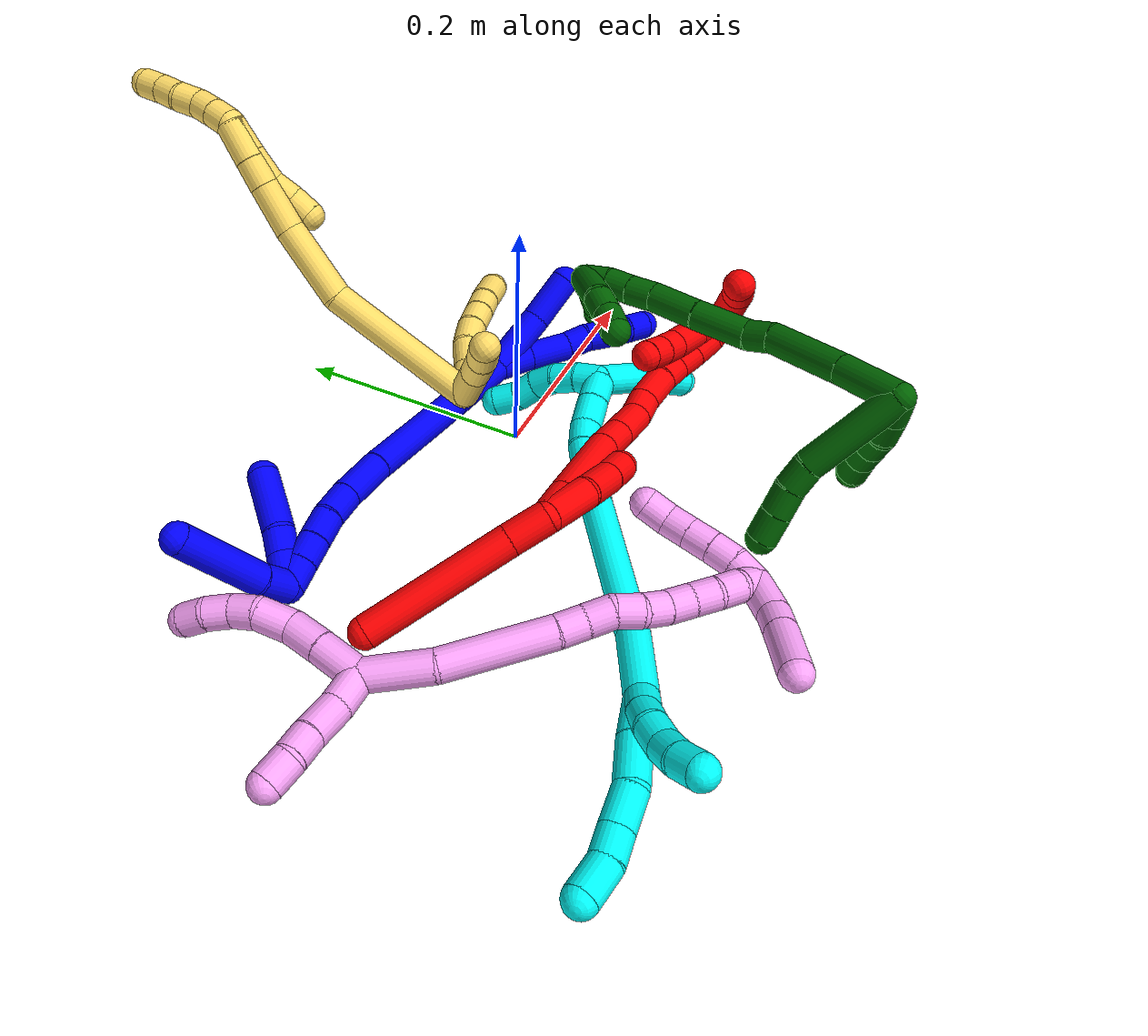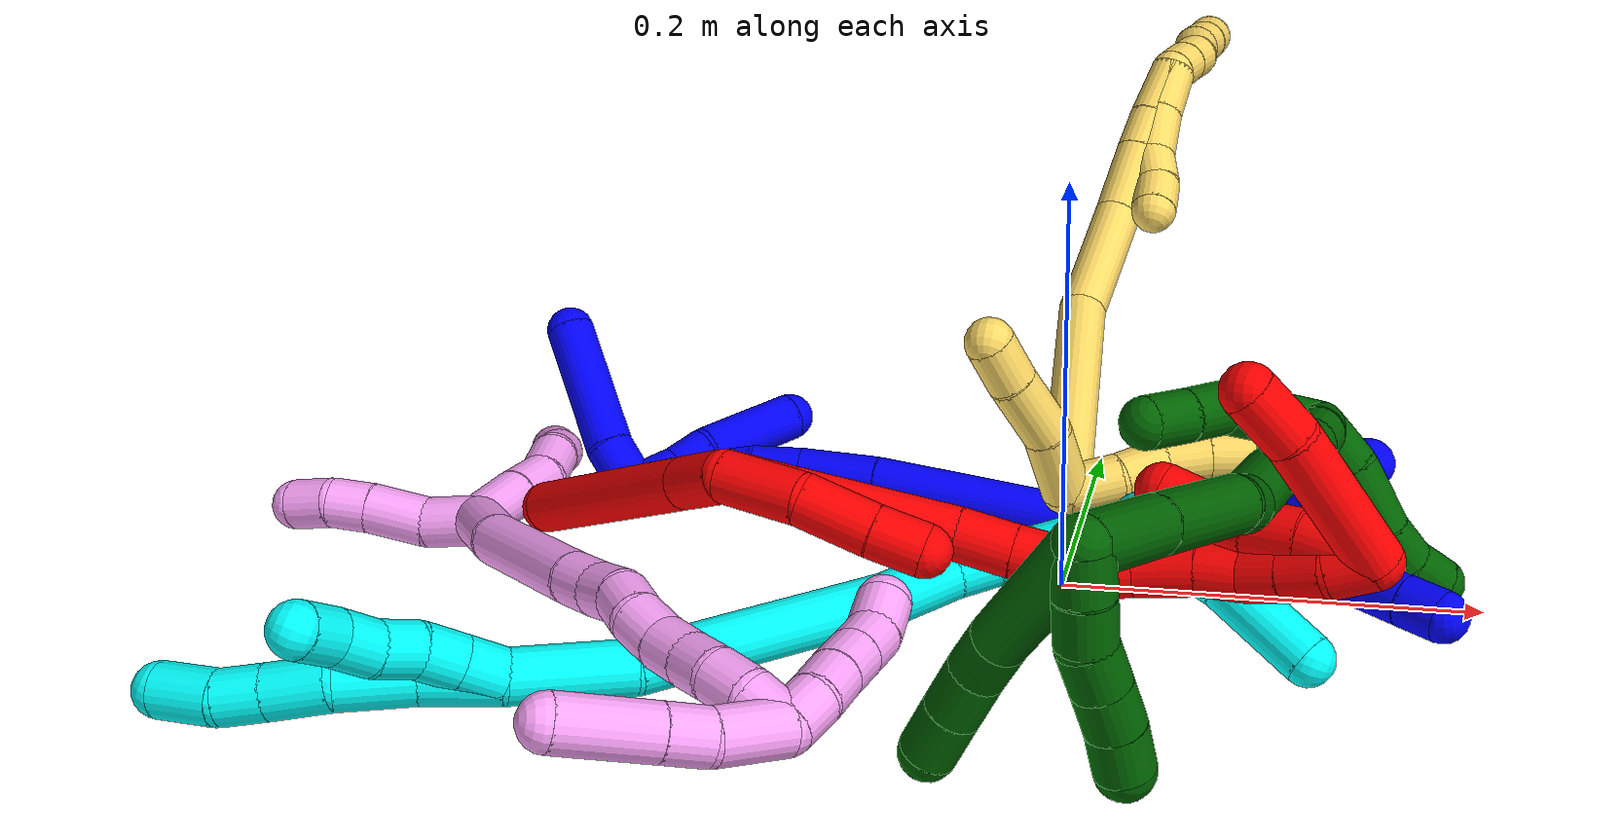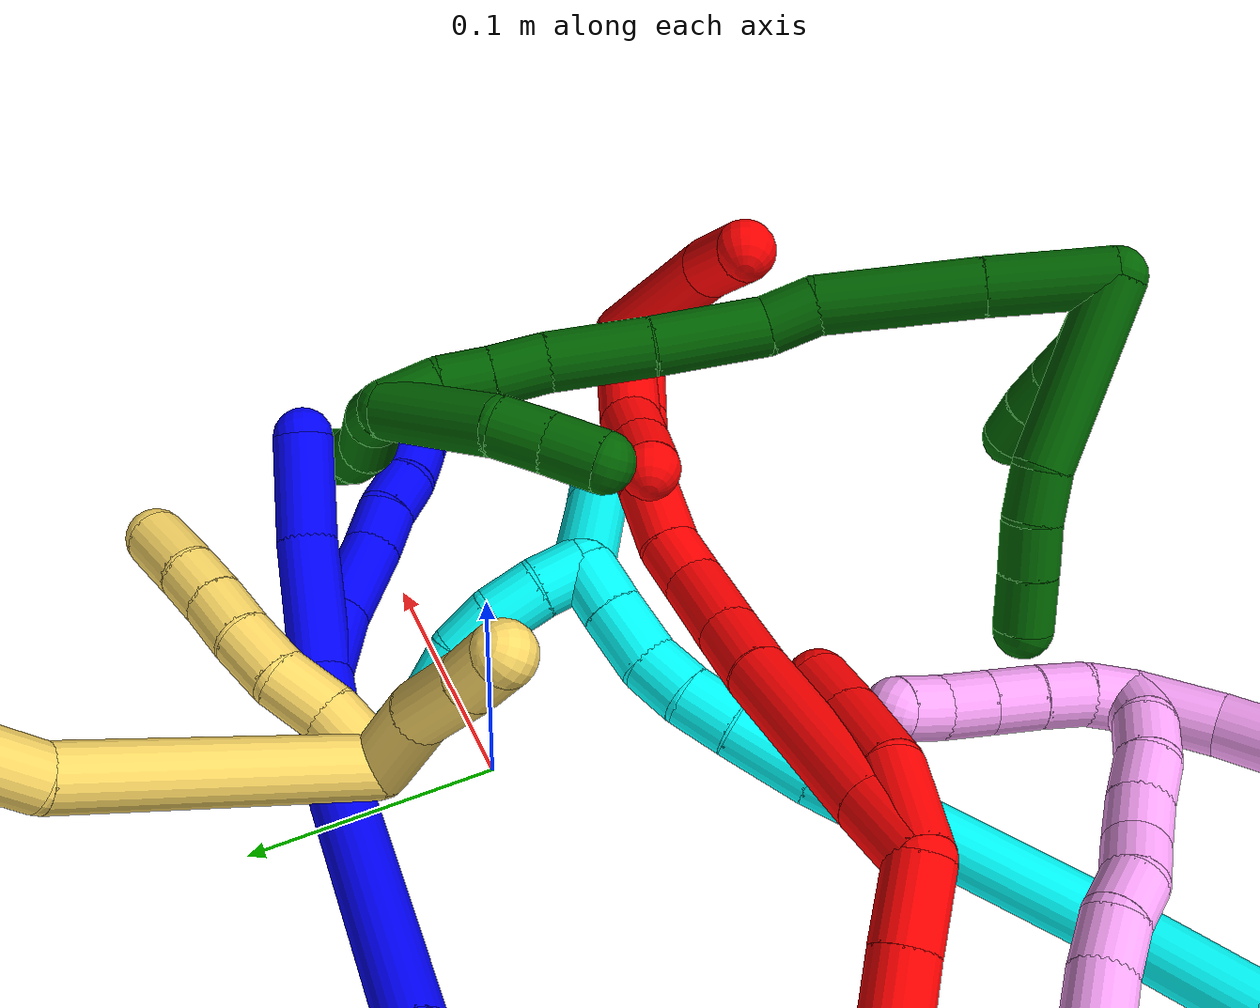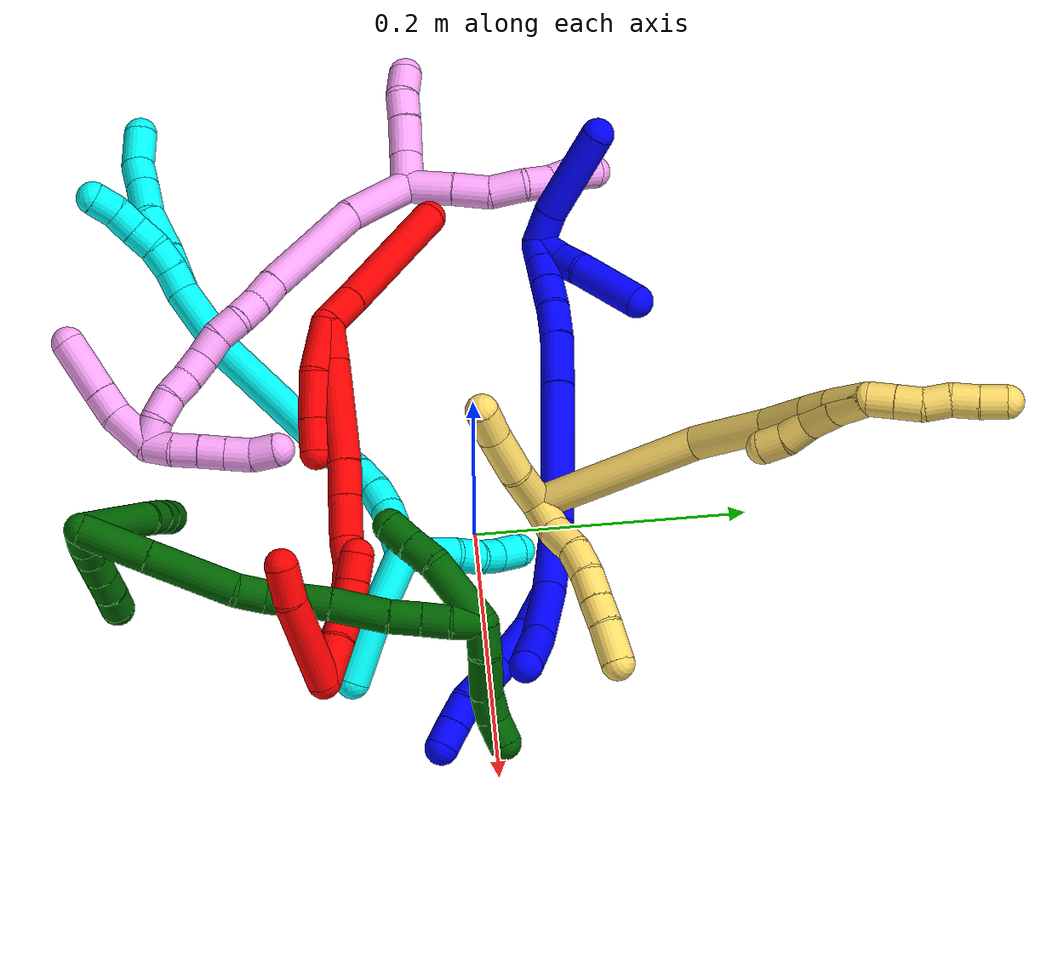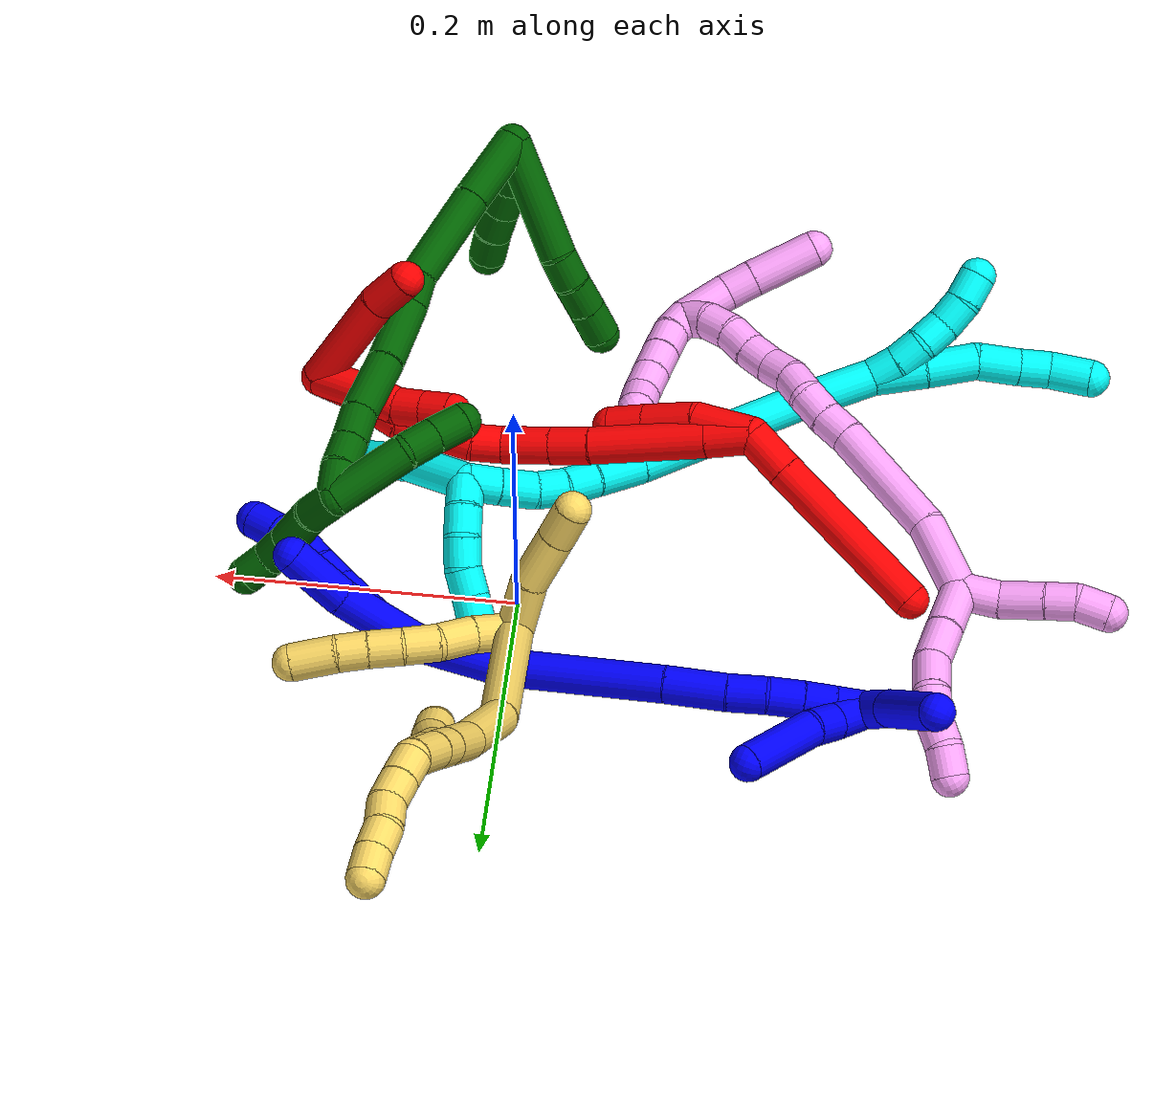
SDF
<sdf version="1.7">
 <world name="default">
  <plugin name="TubeGeneratorPlugin" filename="libtube_generator_plugin.so"/>
  <model name="photoneo_s_sensor">
   <static>1</static>
   <pose>0 0 2 1.57079 1.57079 3.14159</pose>
   <link name="link">
    <inertial><mass>0.1</mass></inertial>
    <sensor name="sensor" type="depth">
     <update_rate>30</update_rate>
     <camera>
      <horizontal_fov>1.22</horizontal_fov>
      <image><width>1920</width><height>1200</height><format>B8G8R8</format></image>
      <clip><near>0.1</near><far>4</far></clip>
      <depth_camera><output>points</output></depth_camera>
     </camera>
     <plugin name="camera_plugin" filename="libgazebo_ros_depth_camera.so">
      <baseline>0.2</baseline>
      <alwaysOn>1</alwaysOn>
      <updateRate>0.0</updateRate>
      <cameraName>camera_ir</cameraName>
      <imageTopicName>/camera/color/image_raw</imageTopicName>
      <cameraInfoTopicName>/camera/color/camera_info</cameraInfoTopicName>
      <depthImageTopicName>/camera/depth/image_raw</depthImageTopicName>
      <depthImageCameraInfoTopicName>/camera/depth/camera_info</depthImageCameraInfoTopicName>
      <pointCloudTopicName>/camera/depth/points</pointCloudTopicName>
      <frameName>fr_optical</frameName>
      <pointCloudCutoff>0.1</pointCloudCutoff>
      <pointCloudCutoffMax>2.0</pointCloudCutoffMax>
      <distortionK1>0</distortionK1>
      <distortionK2>0</distortionK2>
      <distortionK3>0</distortionK3>
      <distortionT1>0</distortionT1>
      <distortionT2>0</distortionT2>
      <CxPrime>0</CxPrime>
      <Cx>0</Cx>
      <Cy>0</Cy>
      <focalLength>0</focalLength>
      <hackBaseline>0</hackBaseline>
     </plugin>
    </sensor>
   </link>
  </model>
  <gravity>0 0 -9.8</gravity>
  <magnetic_field>6e-06 2.3e-05 -4.2e-05</magnetic_field>
  <atmosphere type="adiabatic"/>
  <physics name="default_physics" default="0" type="ode">
   <max_step_size>0.003</max_step_size>
   <real_time_factor>1</real_time_factor>
   <real_time_update_rate>1000</real_time_update_rate>
   <max_contacts>10000</max_contacts>
   <ode>
    <solver>
     <type>quick</type>
     <iters>100</iters>
     <sor>1.3</sor>
     <use_dynamic_moi_rescaling>0</use_dynamic_moi_rescaling>
    </solver>
    <constraints>
     <contact_max_correcting_vel>0</contact_max_correcting_vel>
     <contact_surface_layer>0.001</contact_surface_layer>
     <cfm>0</cfm>
     <erp>0.2</erp>
    </constraints>
   </ode>
  </physics>
  <scene><ambient>0.4 0.4 0.4 1</ambient><background>0.7 0.7 0.7 1</background><shadows>0</shadows></scene>
  <audio><device>default</device></audio>
  <spherical_coordinates>
   <surface_model>EARTH_WGS84</surface_model>
   <latitude_deg>0</latitude_deg>
   <longitude_deg>0</longitude_deg>
   <elevation>0</elevation>
   <heading_deg>0</heading_deg>
  </spherical_coordinates>
  <model name="bin">
   <static>1</static>
   <link name="bottom">
    <collision name="collision-bottom">
     <pose>0 0 -0.01 0 -0 0</pose>
     <geometry><box><size>0.8 0.6 0.02</size></box></geometry>
     <surface>
      <friction><ode><mu>100</mu><mu2>100</mu2></ode></friction>
      <contact><collide_bitmask>65535</collide_bitmask></contact>
     </surface>
    </collision>
   </link>
   <link name="west_wall">
    <collision name="collision-west_wall">
     <pose>-0.41 0 0.1 0 -0 0</pose>
     <geometry><box><size>0.02 0.6 0.2</size></box></geometry>
     <surface>
      <friction><ode><mu>100</mu><mu2>100</mu2></ode></friction>
      <contact><collide_bitmask>65535</collide_bitmask></contact>
     </surface>
    </collision>
   </link>
   <link name="east_wall">
    <collision name="collision-east_wall">
     <pose>0.41 0 0.1 0 -0 0</pose>
     <geometry><box><size>0.02 0.6 0.2</size></box></geometry>
     <surface>
      <friction><ode><mu>100</mu><mu2>100</mu2></ode></friction>
      <contact><collide_bitmask>65535</collide_bitmask></contact>
     </surface>
    </collision>
   </link>
   <link name="south_wall">
    <collision name="collision-south_wall">
     <pose>0 -0.31 0.1 0 -0 0</pose>
     <geometry><box><size>0.8 0.02 0.2</size></box></geometry>
     <surface>
      <friction><ode><mu>100</mu><mu2>100</mu2></ode></friction>
      <contact><collide_bitmask>65535</collide_bitmask></contact>
     </surface>
    </collision>
   </link>
   <link name="north_wall">
    <collision name="collision-north_wall">
     <pose>0 0.31 0.1 0 -0 0</pose>
     <geometry><box><size>0.8 0.02 0.2</size></box></geometry>
     <surface>
      <friction><ode><mu>100</mu><mu2>100</mu2></ode></friction>
      <contact><collide_bitmask>65535</collide_bitmask></contact>
     </surface>
    </collision>
   </link>
  </model>
  <model name="1">
   <static>0</static>
   <link name="1">
    <collision name="collision-cylinder-e_1_2_8">
     <pose>0.004807 0.000513 -0.015629 -3.10876 0.298252 -2.9239</pose>
     <geometry><cylinder><radius>0.0125</radius><length>0.032719</length></cylinder></geometry>
     <surface>
      <friction><ode><mu>1.16</mu><mu2>1.16</mu2><slip1>0</slip1><slip2>0</slip2></ode></friction>
      <contact><ode><kp>1e+06</kp><kd>1</kd><max_vel>0</max_vel><min_depth>0.001</min_depth></ode></contact>
     </surface>
    </collision>
    <visual name="visual-cylinder-e_1_2_8">
     <pose>0.004807 0.000513 -0.015629 -3.10876 0.298252 -2.9239</pose>
     <geometry><cylinder><radius>0.0125</radius><length>0.032719</length></cylinder></geometry>
     <material><ambient>0 0 1 1</ambient></material>
    </visual>
    <collision name="collision-cylinder-e_2_8_9">
     <pose>0.016178 0.004783 -0.048291 -2.92452 0.359913 -2.0623</pose>
     <geometry><cylinder><radius>0.0125</radius><length>0.037274</length></cylinder></geometry>
     <surface>
      <friction><ode><mu>1.16</mu><mu2>1.16</mu2><slip1>0</slip1><slip2>0</slip2></ode></friction>
      <contact><ode><kp>1e+06</kp><kd>1</kd><max_vel>0</max_vel><min_depth>0.001</min_depth></ode></contact>
     </surface>
    </collision>
    <visual name="visual-cylinder-e_2_8_9">
     <pose>0.016178 0.004783 -0.048291 -2.92452 0.359913 -2.0623</pose>
     <geometry><cylinder><radius>0.0125</radius><length>0.037274</length></cylinder></geometry>
     <material><ambient>0 0 1 1</ambient></material>
    </visual>
    <collision name="collision-cylinder-e_3_9_10">
     <pose>0.025069 0.011528 -0.074582 -2.82934 0.23479 -1.28606</pose>
     <geometry><cylinder><radius>0.0125</radius><length>0.020004</length></cylinder></geometry>
     <surface>
      <friction><ode><mu>1.16</mu><mu2>1.16</mu2><slip1>0</slip1><slip2>0</slip2></ode></friction>
      <contact><ode><kp>1e+06</kp><kd>1</kd><max_vel>0</max_vel><min_depth>0.001</min_depth></ode></contact>
     </surface>
    </collision>
    <visual name="visual-cylinder-e_3_9_10">
     <pose>0.025069 0.011528 -0.074582 -2.82934 0.23479 -1.28606</pose>
     <geometry><cylinder><radius>0.0125</radius><length>0.020004</length></cylinder></geometry>
     <material><ambient>0 0 1 1</ambient></material>
    </visual>
    <collision name="collision-cylinder-e_4_10_11">
     <pose>0.031736 0.016926 -0.092522 -2.87096 0.448916 -2.06613</pose>
     <geometry><cylinder><radius>0.0125</radius><length>0.020002</length></cylinder></geometry>
     <surface>
      <friction><ode><mu>1.16</mu><mu2>1.16</mu2><slip1>0</slip1><slip2>0</slip2></ode></friction>
      <contact><ode><kp>1e+06</kp><kd>1</kd><max_vel>0</max_vel><min_depth>0.001</min_depth></ode></contact>
     </surface>
    </collision>
    <visual name="visual-cylinder-e_4_10_11">
     <pose>0.031736 0.016926 -0.092522 -2.87096 0.448916 -2.06613</pose>
     <geometry><cylinder><radius>0.0125</radius><length>0.020002</length></cylinder></geometry>
     <material><ambient>0 0 1 1</ambient></material>
    </visual>
    <collision name="collision-cylinder-e_5_11_12">
     <pose>0.039682 0.019347 -0.110531 -3.14026 0.368896 -3.13446</pose>
     <geometry><cylinder><radius>0.0125</radius><length>0.02</length></cylinder></geometry>
     <surface>
      <friction><ode><mu>1.16</mu><mu2>1.16</mu2><slip1>0</slip1><slip2>0</slip2></ode></friction>
      <contact><ode><kp>1e+06</kp><kd>1</kd><max_vel>0</max_vel><min_depth>0.001</min_depth></ode></contact>
     </surface>
    </collision>
    <visual name="visual-cylinder-e_5_11_12">
     <pose>0.039682 0.019347 -0.110531 -3.14026 0.368896 -3.13446</pose>
     <geometry><cylinder><radius>0.0125</radius><length>0.02</length></cylinder></geometry>
     <material><ambient>0 0 1 1</ambient></material>
    </visual>
    <collision name="collision-cylinder-e_6_12_6">
     <pose>0.046698 0.019055 -0.129254 3.10926 0.347968 2.95812</pose>
     <geometry><cylinder><radius>0.0125</radius><length>0.02</length></cylinder></geometry>
     <surface>
      <friction><ode><mu>1.16</mu><mu2>1.16</mu2><slip1>0</slip1><slip2>0</slip2></ode></friction>
      <contact><ode><kp>1e+06</kp><kd>1</kd><max_vel>0</max_vel><min_depth>0.001</min_depth></ode></contact>
     </surface>
    </collision>
    <visual name="visual-cylinder-e_6_12_6">
     <pose>0.046698 0.019055 -0.129254 3.10926 0.347968 2.95812</pose>
     <geometry><cylinder><radius>0.0125</radius><length>0.02</length></cylinder></geometry>
     <material><ambient>0 0 1 1</ambient></material>
    </visual>
    <collision name="collision-cylinder-e_1_2_13">
     <pose>-0.006639 0.005743 -0.026944 -2.93157 -0.23646 1.69008</pose>
     <geometry><cylinder><radius>0.0125</radius><length>0.056676</length></cylinder></geometry>
     <surface>
      <friction><ode><mu>1.16</mu><mu2>1.16</mu2><slip1>0</slip1><slip2>0</slip2></ode></friction>
      <contact><ode><kp>1e+06</kp><kd>1</kd><max_vel>0</max_vel><min_depth>0.001</min_depth></ode></contact>
     </surface>
    </collision>
    <visual name="visual-cylinder-e_1_2_13">
     <pose>-0.006639 0.005743 -0.026944 -2.93157 -0.23646 1.69008</pose>
     <geometry><cylinder><radius>0.0125</radius><length>0.056676</length></cylinder></geometry>
     <material><ambient>0 0 1 1</ambient></material>
    </visual>
    <collision name="collision-cylinder-e_2_13_5">
     <pose>-0.019449 0.019551 -0.073023 -2.74272 -0.288911 1.24766</pose>
     <geometry><cylinder><radius>0.0125</radius><length>0.043324</length></cylinder></geometry>
     <surface>
      <friction><ode><mu>1.16</mu><mu2>1.16</mu2><slip1>0</slip1><slip2>0</slip2></ode></friction>
      <contact><ode><kp>1e+06</kp><kd>1</kd><max_vel>0</max_vel><min_depth>0.001</min_depth></ode></contact>
     </surface>
    </collision>
    <visual name="visual-cylinder-e_2_13_5">
     <pose>-0.019449 0.019551 -0.073023 -2.74272 -0.288911 1.24766</pose>
     <geometry><cylinder><radius>0.0125</radius><length>0.043324</length></cylinder></geometry>
     <material><ambient>0 0 1 1</ambient></material>
    </visual>
    <collision name="collision-cylinder-e_1_2_14">
     <pose>0.00085 0.003593 0.029465 -0.121332 0.028628 -0.001739</pose>
     <geometry><cylinder><radius>0.0125</radius><length>0.059391</length></cylinder></geometry>
     <surface>
      <friction><ode><mu>1.16</mu><mu2>1.16</mu2><slip1>0</slip1><slip2>0</slip2></ode></friction>
      <contact><ode><kp>1e+06</kp><kd>1</kd><max_vel>0</max_vel><min_depth>0.001</min_depth></ode></contact>
     </surface>
    </collision>
    <visual name="visual-cylinder-e_1_2_14">
     <pose>0.00085 0.003593 0.029465 -0.121332 0.028628 -0.001739</pose>
     <geometry><cylinder><radius>0.0125</radius><length>0.059391</length></cylinder></geometry>
     <material><ambient>0 0 1 1</ambient></material>
    </visual>
    <collision name="collision-cylinder-e_2_14_15">
     <pose>0.00184 0.023548 0.110776 -0.305702 0.002573 -0.000396</pose>
     <geometry><cylinder><radius>0.0125</radius><length>0.108734</length></cylinder></geometry>
     <surface>
      <friction><ode><mu>1.16</mu><mu2>1.16</mu2><slip1>0</slip1><slip2>0</slip2></ode></friction>
      <contact><ode><kp>1e+06</kp><kd>1</kd><max_vel>0</max_vel><min_depth>0.001</min_depth></ode></contact>
     </surface>
    </collision>
    <visual name="visual-cylinder-e_2_14_15">
     <pose>0.00184 0.023548 0.110776 -0.305702 0.002573 -0.000396</pose>
     <geometry><cylinder><radius>0.0125</radius><length>0.108734</length></cylinder></geometry>
     <material><ambient>0 0 1 1</ambient></material>
    </visual>
    <collision name="collision-cylinder-e_3_15_16">
     <pose>0.003372 0.04522 0.182289 -0.263693 0.068227 -0.009051</pose>
     <geometry><cylinder><radius>0.0125</radius><length>0.040836</length></cylinder></geometry>
     <surface>
      <friction><ode><mu>1.16</mu><mu2>1.16</mu2><slip1>0</slip1><slip2>0</slip2></ode></friction>
      <contact><ode><kp>1e+06</kp><kd>1</kd><max_vel>0</max_vel><min_depth>0.001</min_depth></ode></contact>
     </surface>
    </collision>
    <visual name="visual-cylinder-e_3_15_16">
     <pose>0.003372 0.04522 0.182289 -0.263693 0.068227 -0.009051</pose>
     <geometry><cylinder><radius>0.0125</radius><length>0.040836</length></cylinder></geometry>
     <material><ambient>0 0 1 1</ambient></material>
    </visual>
    <collision name="collision-cylinder-e_4_16_17">
     <pose>0.00679 0.054354 0.214076 -0.305639 0.158083 -0.024398</pose>
     <geometry><cylinder><radius>0.0125</radius><length>0.025742</length></cylinder></geometry>
     <surface>
      <friction><ode><mu>1.16</mu><mu2>1.16</mu2><slip1>0</slip1><slip2>0</slip2></ode></friction>
      <contact><ode><kp>1e+06</kp><kd>1</kd><max_vel>0</max_vel><min_depth>0.001</min_depth></ode></contact>
     </surface>
    </collision>
    <visual name="visual-cylinder-e_4_16_17">
     <pose>0.00679 0.054354 0.214076 -0.305639 0.158083 -0.024398</pose>
     <geometry><cylinder><radius>0.0125</radius><length>0.025742</length></cylinder></geometry>
     <material><ambient>0 0 1 1</ambient></material>
    </visual>
    <collision name="collision-cylinder-e_5_17_18">
     <pose>0.012561 0.060519 0.23694 -0.214573 0.328263 -0.035671</pose>
     <geometry><cylinder><radius>0.0125</radius><length>0.023228</length></cylinder></geometry>
     <surface>
      <friction><ode><mu>1.16</mu><mu2>1.16</mu2><slip1>0</slip1><slip2>0</slip2></ode></friction>
      <contact><ode><kp>1e+06</kp><kd>1</kd><max_vel>0</max_vel><min_depth>0.001</min_depth></ode></contact>
     </surface>
    </collision>
    <visual name="visual-cylinder-e_5_17_18">
     <pose>0.012561 0.060519 0.23694 -0.214573 0.328263 -0.035671</pose>
     <geometry><cylinder><radius>0.0125</radius><length>0.023228</length></cylinder></geometry>
     <material><ambient>0 0 1 1</ambient></material>
    </visual>
    <collision name="collision-cylinder-e_6_18_19">
     <pose>0.019872 0.064526 0.257441 -0.169061 0.345837 -0.029597</pose>
     <geometry><cylinder><radius>0.0125</radius><length>0.021046</length></cylinder></geometry>
     <surface>
      <friction><ode><mu>1.16</mu><mu2>1.16</mu2><slip1>0</slip1><slip2>0</slip2></ode></friction>
      <contact><ode><kp>1e+06</kp><kd>1</kd><max_vel>0</max_vel><min_depth>0.001</min_depth></ode></contact>
     </surface>
    </collision>
    <visual name="visual-cylinder-e_6_18_19">
     <pose>0.019872 0.064526 0.257441 -0.169061 0.345837 -0.029597</pose>
     <geometry><cylinder><radius>0.0125</radius><length>0.021046</length></cylinder></geometry>
     <material><ambient>0 0 1 1</ambient></material>
    </visual>
    <collision name="collision-cylinder-e_7_19_1">
     <pose>0.027075 0.067786 0.276932 -0.162341 0.353214 -0.029034</pose>
     <geometry><cylinder><radius>0.0125</radius><length>0.021023</length></cylinder></geometry>
     <surface>
      <friction><ode><mu>1.16</mu><mu2>1.16</mu2><slip1>0</slip1><slip2>0</slip2></ode></friction>
      <contact><ode><kp>1e+06</kp><kd>1</kd><max_vel>0</max_vel><min_depth>0.001</min_depth></ode></contact>
     </surface>
    </collision>
    <visual name="visual-cylinder-e_7_19_1">
     <pose>0.027075 0.067786 0.276932 -0.162341 0.353214 -0.029034</pose>
     <geometry><cylinder><radius>0.0125</radius><length>0.021023</length></cylinder></geometry>
     <material><ambient>0 0 1 1</ambient></material>
    </visual>
    <collision name="collision-cylinder-e_1_1_20">
     <pose>0.021256 0.064294 0.279809 2.50335 -0.83642 -1.86298</pose>
     <geometry><cylinder><radius>0.0125</radius><length>0.025476</length></cylinder></geometry>
     <surface>
      <friction><ode><mu>1.16</mu><mu2>1.16</mu2><slip1>0</slip1><slip2>0</slip2></ode></friction>
      <contact><ode><kp>1e+06</kp><kd>1</kd><max_vel>0</max_vel><min_depth>0.001</min_depth></ode></contact>
     </surface>
    </collision>
    <visual name="visual-cylinder-e_1_1_20">
     <pose>0.021256 0.064294 0.279809 2.50335 -0.83642 -1.86298</pose>
     <geometry><cylinder><radius>0.0125</radius><length>0.025476</length></cylinder></geometry>
     <material><ambient>0 0 1 1</ambient></material>
    </visual>
    <collision name="collision-cylinder-e_2_20_21">
     <pose>0.003453 0.05642 0.267784 2.6469 -0.957673 -2.23614</pose>
     <geometry><cylinder><radius>0.0125</radius><length>0.020416</length></cylinder></geometry>
     <surface>
      <friction><ode><mu>1.16</mu><mu2>1.16</mu2><slip1>0</slip1><slip2>0</slip2></ode></friction>
      <contact><ode><kp>1e+06</kp><kd>1</kd><max_vel>0</max_vel><min_depth>0.001</min_depth></ode></contact>
     </surface>
    </collision>
    <visual name="visual-cylinder-e_2_20_21">
     <pose>0.003453 0.05642 0.267784 2.6469 -0.957673 -2.23614</pose>
     <geometry><cylinder><radius>0.0125</radius><length>0.020416</length></cylinder></geometry>
     <material><ambient>0 0 1 1</ambient></material>
    </visual>
    <collision name="collision-cylinder-e_3_21_4">
     <pose>-0.024912 0.040294 0.250229 2.31919 -0.832858 -1.585</pose>
     <geometry><cylinder><radius>0.0125</radius><length>0.054108</length></cylinder></geometry>
     <surface>
      <friction><ode><mu>1.16</mu><mu2>1.16</mu2><slip1>0</slip1><slip2>0</slip2></ode></friction>
      <contact><ode><kp>1e+06</kp><kd>1</kd><max_vel>0</max_vel><min_depth>0.001</min_depth></ode></contact>
     </surface>
    </collision>
    <visual name="visual-cylinder-e_3_21_4">
     <pose>-0.024912 0.040294 0.250229 2.31919 -0.832858 -1.585</pose>
     <geometry><cylinder><radius>0.0125</radius><length>0.054108</length></cylinder></geometry>
     <material><ambient>0 0 1 1</ambient></material>
    </visual>
    <collision name="collision-cylinder-e_1_1_22">
     <pose>0.021766 0.075423 0.294941 -0.630697 -0.717657 0.243509</pose>
     <geometry><cylinder><radius>0.0125</radius><length>0.027204</length></cylinder></geometry>
     <surface>
      <friction><ode><mu>1.16</mu><mu2>1.16</mu2><slip1>0</slip1><slip2>0</slip2></ode></friction>
      <contact><ode><kp>1e+06</kp><kd>1</kd><max_vel>0</max_vel><min_depth>0.001</min_depth></ode></contact>
     </surface>
    </collision>
    <visual name="visual-cylinder-e_1_1_22">
     <pose>0.021766 0.075423 0.294941 -0.630697 -0.717657 0.243509</pose>
     <geometry><cylinder><radius>0.0125</radius><length>0.027204</length></cylinder></geometry>
     <material><ambient>0 0 1 1</ambient></material>
    </visual>
    <collision name="collision-cylinder-e_2_22_3">
     <pose>-0.016298 0.094335 0.32086 -0.630212 -0.927323 0.323137</pose>
     <geometry><cylinder><radius>0.0125</radius><length>0.072796</length></cylinder></geometry>
     <surface>
      <friction><ode><mu>1.16</mu><mu2>1.16</mu2><slip1>0</slip1><slip2>0</slip2></ode></friction>
      <contact><ode><kp>1e+06</kp><kd>1</kd><max_vel>0</max_vel><min_depth>0.001</min_depth></ode></contact>
     </surface>
    </collision>
    <visual name="visual-cylinder-e_2_22_3">
     <pose>-0.016298 0.094335 0.32086 -0.630212 -0.927323 0.323137</pose>
     <geometry><cylinder><radius>0.0125</radius><length>0.072796</length></cylinder></geometry>
     <material><ambient>0 0 1 1</ambient></material>
    </visual>
    <collision name="collision-sphere-3">
     <pose>-0.045417 0.107204 0.338502 0 -0 0</pose>
     <geometry><sphere><radius>0.0125</radius></sphere></geometry>
     <surface>
      <friction><ode><mu>1.16</mu><mu2>1.16</mu2><slip1>0</slip1><slip2>0</slip2></ode></friction>
      <contact><ode><kp>1e+06</kp><kd>1</kd><max_vel>0</max_vel><min_depth>0.001</min_depth></ode></contact>
     </surface>
    </collision>
    <visual name="visual-sphere-3">
     <pose>-0.045417 0.107204 0.338502 0 -0 0</pose>
     <geometry><sphere><radius>0.0125</radius></sphere></geometry>
     <material><ambient>0 0 1 1</ambient></material>
    </visual>
    <collision name="collision-sphere-22">
     <pose>0.012821 0.081466 0.303217 0 -0 0</pose>
     <geometry><sphere><radius>0.0125</radius></sphere></geometry>
     <surface>
      <friction><ode><mu>1.16</mu><mu2>1.16</mu2><slip1>0</slip1><slip2>0</slip2></ode></friction>
      <contact><ode><kp>1e+06</kp><kd>1</kd><max_vel>0</max_vel><min_depth>0.001</min_depth></ode></contact>
     </surface>
    </collision>
    <visual name="visual-sphere-22">
     <pose>0.012821 0.081466 0.303217 0 -0 0</pose>
     <geometry><sphere><radius>0.0125</radius></sphere></geometry>
     <material><ambient>0 0 1 1</ambient></material>
    </visual>
    <collision name="collision-sphere-4">
     <pose>-0.044928 0.026956 0.237844 0 -0 0</pose>
     <geometry><sphere><radius>0.0125</radius></sphere></geometry>
     <surface>
      <friction><ode><mu>1.16</mu><mu2>1.16</mu2><slip1>0</slip1><slip2>0</slip2></ode></friction>
      <contact><ode><kp>1e+06</kp><kd>1</kd><max_vel>0</max_vel><min_depth>0.001</min_depth></ode></contact>
     </surface>
    </collision>
    <visual name="visual-sphere-4">
     <pose>-0.044928 0.026956 0.237844 0 -0 0</pose>
     <geometry><sphere><radius>0.0125</radius></sphere></geometry>
     <material><ambient>0 0 1 1</ambient></material>
    </visual>
    <collision name="collision-sphere-21">
     <pose>-0.004896 0.053631 0.262614 0 -0 0</pose>
     <geometry><sphere><radius>0.0125</radius></sphere></geometry>
     <surface>
      <friction><ode><mu>1.16</mu><mu2>1.16</mu2><slip1>0</slip1><slip2>0</slip2></ode></friction>
      <contact><ode><kp>1e+06</kp><kd>1</kd><max_vel>0</max_vel><min_depth>0.001</min_depth></ode></contact>
     </surface>
    </collision>
    <visual name="visual-sphere-21">
     <pose>-0.004896 0.053631 0.262614 0 -0 0</pose>
     <geometry><sphere><radius>0.0125</radius></sphere></geometry>
     <material><ambient>0 0 1 1</ambient></material>
    </visual>
    <collision name="collision-sphere-20">
     <pose>0.011802 0.059208 0.272954 0 -0 0</pose>
     <geometry><sphere><radius>0.0125</radius></sphere></geometry>
     <surface>
      <friction><ode><mu>1.16</mu><mu2>1.16</mu2><slip1>0</slip1><slip2>0</slip2></ode></friction>
      <contact><ode><kp>1e+06</kp><kd>1</kd><max_vel>0</max_vel><min_depth>0.001</min_depth></ode></contact>
     </surface>
    </collision>
    <visual name="visual-sphere-20">
     <pose>0.011802 0.059208 0.272954 0 -0 0</pose>
     <geometry><sphere><radius>0.0125</radius></sphere></geometry>
     <material><ambient>0 0 1 1</ambient></material>
    </visual>
    <collision name="collision-sphere-12">
     <pose>0.043288 0.019359 -0.119858 0 -0 0</pose>
     <geometry><sphere><radius>0.0125</radius></sphere></geometry>
     <surface>
      <friction><ode><mu>1.16</mu><mu2>1.16</mu2><slip1>0</slip1><slip2>0</slip2></ode></friction>
      <contact><ode><kp>1e+06</kp><kd>1</kd><max_vel>0</max_vel><min_depth>0.001</min_depth></ode></contact>
     </surface>
    </collision>
    <visual name="visual-sphere-12">
     <pose>0.043288 0.019359 -0.119858 0 -0 0</pose>
     <geometry><sphere><radius>0.0125</radius></sphere></geometry>
     <material><ambient>0 0 1 1</ambient></material>
    </visual>
    <collision name="collision-sphere-11">
     <pose>0.036077 0.019334 -0.101204 0 -0 0</pose>
     <geometry><sphere><radius>0.0125</radius></sphere></geometry>
     <surface>
      <friction><ode><mu>1.16</mu><mu2>1.16</mu2><slip1>0</slip1><slip2>0</slip2></ode></friction>
      <contact><ode><kp>1e+06</kp><kd>1</kd><max_vel>0</max_vel><min_depth>0.001</min_depth></ode></contact>
     </surface>
    </collision>
    <visual name="visual-sphere-11">
     <pose>0.036077 0.019334 -0.101204 0 -0 0</pose>
     <geometry><sphere><radius>0.0125</radius></sphere></geometry>
     <material><ambient>0 0 1 1</ambient></material>
    </visual>
    <collision name="collision-sphere-10">
     <pose>0.027396 0.014517 -0.08384 0 -0 0</pose>
     <geometry><sphere><radius>0.0125</radius></sphere></geometry>
     <surface>
      <friction><ode><mu>1.16</mu><mu2>1.16</mu2><slip1>0</slip1><slip2>0</slip2></ode></friction>
      <contact><ode><kp>1e+06</kp><kd>1</kd><max_vel>0</max_vel><min_depth>0.001</min_depth></ode></contact>
     </surface>
    </collision>
    <visual name="visual-sphere-10">
     <pose>0.027396 0.014517 -0.08384 0 -0 0</pose>
     <geometry><sphere><radius>0.0125</radius></sphere></geometry>
     <material><ambient>0 0 1 1</ambient></material>
    </visual>
    <collision name="collision-sphere-9">
     <pose>0.022742 0.00854 -0.065325 0 -0 0</pose>
     <geometry><sphere><radius>0.0125</radius></sphere></geometry>
     <surface>
      <friction><ode><mu>1.16</mu><mu2>1.16</mu2><slip1>0</slip1><slip2>0</slip2></ode></friction>
      <contact><ode><kp>1e+06</kp><kd>1</kd><max_vel>0</max_vel><min_depth>0.001</min_depth></ode></contact>
     </surface>
    </collision>
    <visual name="visual-sphere-9">
     <pose>0.022742 0.00854 -0.065325 0 -0 0</pose>
     <geometry><sphere><radius>0.0125</radius></sphere></geometry>
     <material><ambient>0 0 1 1</ambient></material>
    </visual>
    <collision name="collision-sphere-2">
     <geometry><sphere><radius>0.0125</radius></sphere></geometry>
     <surface>
      <friction><ode><mu>1.16</mu><mu2>1.16</mu2><slip1>0</slip1><slip2>0</slip2></ode></friction>
      <contact><ode><kp>1e+06</kp><kd>1</kd><max_vel>0</max_vel><min_depth>0.001</min_depth></ode></contact>
     </surface>
    </collision>
    <visual name="visual-sphere-2">
     <geometry><sphere><radius>0.0125</radius></sphere></geometry>
     <material><ambient>0 0 1 1</ambient></material>
    </visual>
    <collision name="collision-sphere-19">
     <pose>0.023439 0.066192 0.267199 0 -0 0</pose>
     <geometry><sphere><radius>0.0125</radius></sphere></geometry>
     <surface>
      <friction><ode><mu>1.16</mu><mu2>1.16</mu2><slip1>0</slip1><slip2>0</slip2></ode></friction>
      <contact><ode><kp>1e+06</kp><kd>1</kd><max_vel>0</max_vel><min_depth>0.001</min_depth></ode></contact>
     </surface>
    </collision>
    <visual name="visual-sphere-19">
     <pose>0.023439 0.066192 0.267199 0 -0 0</pose>
     <geometry><sphere><radius>0.0125</radius></sphere></geometry>
     <material><ambient>0 0 1 1</ambient></material>
    </visual>
    <collision name="collision-sphere-8">
     <pose>0.009614 0.001027 -0.031258 0 -0 0</pose>
     <geometry><sphere><radius>0.0125</radius></sphere></geometry>
     <surface>
      <friction><ode><mu>1.16</mu><mu2>1.16</mu2><slip1>0</slip1><slip2>0</slip2></ode></friction>
      <contact><ode><kp>1e+06</kp><kd>1</kd><max_vel>0</max_vel><min_depth>0.001</min_depth></ode></contact>
     </surface>
    </collision>
    <visual name="visual-sphere-8">
     <pose>0.009614 0.001027 -0.031258 0 -0 0</pose>
     <geometry><sphere><radius>0.0125</radius></sphere></geometry>
     <material><ambient>0 0 1 1</ambient></material>
    </visual>
    <collision name="collision-sphere-6">
     <pose>0.050108 0.018751 -0.13865 0 -0 0</pose>
     <geometry><sphere><radius>0.0125</radius></sphere></geometry>
     <surface>
      <friction><ode><mu>1.16</mu><mu2>1.16</mu2><slip1>0</slip1><slip2>0</slip2></ode></friction>
      <contact><ode><kp>1e+06</kp><kd>1</kd><max_vel>0</max_vel><min_depth>0.001</min_depth></ode></contact>
     </surface>
    </collision>
    <visual name="visual-sphere-6">
     <pose>0.050108 0.018751 -0.13865 0 -0 0</pose>
     <geometry><sphere><radius>0.0125</radius></sphere></geometry>
     <material><ambient>0 0 1 1</ambient></material>
    </visual>
    <collision name="collision-sphere-13">
     <pose>-0.013277 0.011487 -0.053888 0 -0 0</pose>
     <geometry><sphere><radius>0.0125</radius></sphere></geometry>
     <surface>
      <friction><ode><mu>1.16</mu><mu2>1.16</mu2><slip1>0</slip1><slip2>0</slip2></ode></friction>
      <contact><ode><kp>1e+06</kp><kd>1</kd><max_vel>0</max_vel><min_depth>0.001</min_depth></ode></contact>
     </surface>
    </collision>
    <visual name="visual-sphere-13">
     <pose>-0.013277 0.011487 -0.053888 0 -0 0</pose>
     <geometry><sphere><radius>0.0125</radius></sphere></geometry>
     <material><ambient>0 0 1 1</ambient></material>
    </visual>
    <collision name="collision-sphere-5">
     <pose>-0.02562 0.027616 -0.092157 0 -0 0</pose>
     <geometry><sphere><radius>0.0125</radius></sphere></geometry>
     <surface>
      <friction><ode><mu>1.16</mu><mu2>1.16</mu2><slip1>0</slip1><slip2>0</slip2></ode></friction>
      <contact><ode><kp>1e+06</kp><kd>1</kd><max_vel>0</max_vel><min_depth>0.001</min_depth></ode></contact>
     </surface>
    </collision>
    <visual name="visual-sphere-5">
     <pose>-0.02562 0.027616 -0.092157 0 -0 0</pose>
     <geometry><sphere><radius>0.0125</radius></sphere></geometry>
     <material><ambient>0 0 1 1</ambient></material>
    </visual>
    <collision name="collision-sphere-14">
     <pose>0.0017 0.007185 0.05893 0 -0 0</pose>
     <geometry><sphere><radius>0.0125</radius></sphere></geometry>
     <surface>
      <friction><ode><mu>1.16</mu><mu2>1.16</mu2><slip1>0</slip1><slip2>0</slip2></ode></friction>
      <contact><ode><kp>1e+06</kp><kd>1</kd><max_vel>0</max_vel><min_depth>0.001</min_depth></ode></contact>
     </surface>
    </collision>
    <visual name="visual-sphere-14">
     <pose>0.0017 0.007185 0.05893 0 -0 0</pose>
     <geometry><sphere><radius>0.0125</radius></sphere></geometry>
     <material><ambient>0 0 1 1</ambient></material>
    </visual>
    <collision name="collision-sphere-15">
     <pose>0.00198 0.03991 0.162622 0 -0 0</pose>
     <geometry><sphere><radius>0.0125</radius></sphere></geometry>
     <surface>
      <friction><ode><mu>1.16</mu><mu2>1.16</mu2><slip1>0</slip1><slip2>0</slip2></ode></friction>
      <contact><ode><kp>1e+06</kp><kd>1</kd><max_vel>0</max_vel><min_depth>0.001</min_depth></ode></contact>
     </surface>
    </collision>
    <visual name="visual-sphere-15">
     <pose>0.00198 0.03991 0.162622 0 -0 0</pose>
     <geometry><sphere><radius>0.0125</radius></sphere></geometry>
     <material><ambient>0 0 1 1</ambient></material>
    </visual>
    <collision name="collision-sphere-16">
     <pose>0.004764 0.050529 0.201955 0 -0 0</pose>
     <geometry><sphere><radius>0.0125</radius></sphere></geometry>
     <surface>
      <friction><ode><mu>1.16</mu><mu2>1.16</mu2><slip1>0</slip1><slip2>0</slip2></ode></friction>
      <contact><ode><kp>1e+06</kp><kd>1</kd><max_vel>0</max_vel><min_depth>0.001</min_depth></ode></contact>
     </surface>
    </collision>
    <visual name="visual-sphere-16">
     <pose>0.004764 0.050529 0.201955 0 -0 0</pose>
     <geometry><sphere><radius>0.0125</radius></sphere></geometry>
     <material><ambient>0 0 1 1</ambient></material>
    </visual>
    <collision name="collision-sphere-17">
     <pose>0.008816 0.058178 0.226198 0 -0 0</pose>
     <geometry><sphere><radius>0.0125</radius></sphere></geometry>
     <surface>
      <friction><ode><mu>1.16</mu><mu2>1.16</mu2><slip1>0</slip1><slip2>0</slip2></ode></friction>
      <contact><ode><kp>1e+06</kp><kd>1</kd><max_vel>0</max_vel><min_depth>0.001</min_depth></ode></contact>
     </surface>
    </collision>
    <visual name="visual-sphere-17">
     <pose>0.008816 0.058178 0.226198 0 -0 0</pose>
     <geometry><sphere><radius>0.0125</radius></sphere></geometry>
     <material><ambient>0 0 1 1</ambient></material>
    </visual>
    <collision name="collision-sphere-18">
     <pose>0.016305 0.06286 0.247682 0 -0 0</pose>
     <geometry><sphere><radius>0.0125</radius></sphere></geometry>
     <surface>
      <friction><ode><mu>1.16</mu><mu2>1.16</mu2><slip1>0</slip1><slip2>0</slip2></ode></friction>
      <contact><ode><kp>1e+06</kp><kd>1</kd><max_vel>0</max_vel><min_depth>0.001</min_depth></ode></contact>
     </surface>
    </collision>
    <visual name="visual-sphere-18">
     <pose>0.016305 0.06286 0.247682 0 -0 0</pose>
     <geometry><sphere><radius>0.0125</radius></sphere></geometry>
     <material><ambient>0 0 1 1</ambient></material>
    </visual>
    <collision name="collision-sphere-1">
     <pose>0.030711 0.06938 0.286665 0 -0 0</pose>
     <geometry><sphere><radius>0.0125</radius></sphere></geometry>
     <surface>
      <friction><ode><mu>1.16</mu><mu2>1.16</mu2><slip1>0</slip1><slip2>0</slip2></ode></friction>
      <contact><ode><kp>1e+06</kp><kd>1</kd><max_vel>0</max_vel><min_depth>0.001</min_depth></ode></contact>
     </surface>
    </collision>
    <visual name="visual-sphere-1">
     <pose>0.030711 0.06938 0.286665 0 -0 0</pose>
     <geometry><sphere><radius>0.0125</radius></sphere></geometry>
     <material><ambient>0 0 1 1</ambient></material>
    </visual>
    <inertial>
     <pose>0.00389 0.035736 0.114492 0 -0 0</pose>
     <mass>0.75</mass>
     <inertia><ixx>0.000161</ixx><ixy>0</ixy><ixz>0</ixz><iyy>0.000217</iyy><iyz>0</iyz><izz>-6e-06</izz></inertia>
    </inertial>
   </link>
   <pose>0.060355 0.049039 0.014283 1.72955 0.710639 -1.76713</pose>
  </model>
  <model name="2">
   <static>0</static>
   <link name="2">
    <collision name="collision-cylinder-e_1_2_8">
     <pose>-0.0023 -0.004841 -0.014967 2.82876 -0.145167 -0.864034</pose>
     <geometry><cylinder><radius>0.0125</radius><length>0.031795</length></cylinder></geometry>
     <surface>
      <friction><ode><mu>1.16</mu><mu2>1.16</mu2><slip1>0</slip1><slip2>0</slip2></ode></friction>
      <contact><ode><kp>1e+06</kp><kd>1</kd><max_vel>0</max_vel><min_depth>0.001</min_depth></ode></contact>
     </surface>
    </collision>
    <visual name="visual-cylinder-e_1_2_8">
     <pose>-0.0023 -0.004841 -0.014967 2.82876 -0.145167 -0.864034</pose>
     <geometry><cylinder><radius>0.0125</radius><length>0.031795</length></cylinder></geometry>
     <material><ambient>1 0 0 1</ambient></material>
    </visual>
    <collision name="collision-cylinder-e_2_8_6">
     <pose>-0.013778 -0.026196 -0.085935 2.85483 -0.155931 -0.992013</pose>
     <geometry><cylinder><radius>0.0125</radius><length>0.118205</length></cylinder></geometry>
     <surface>
      <friction><ode><mu>1.16</mu><mu2>1.16</mu2><slip1>0</slip1><slip2>0</slip2></ode></friction>
      <contact><ode><kp>1e+06</kp><kd>1</kd><max_vel>0</max_vel><min_depth>0.001</min_depth></ode></contact>
     </surface>
    </collision>
    <visual name="visual-cylinder-e_2_8_6">
     <pose>-0.013778 -0.026196 -0.085935 2.85483 -0.155931 -0.992013</pose>
     <geometry><cylinder><radius>0.0125</radius><length>0.118205</length></cylinder></geometry>
     <material><ambient>1 0 0 1</ambient></material>
    </visual>
    <collision name="collision-cylinder-e_1_2_9">
     <pose>-0.001715 -0.004533 0.019558 0.227773 -0.085232 -0.009755</pose>
     <geometry><cylinder><radius>0.0125</radius><length>0.040299</length></cylinder></geometry>
     <surface>
      <friction><ode><mu>1.16</mu><mu2>1.16</mu2><slip1>0</slip1><slip2>0</slip2></ode></friction>
      <contact><ode><kp>1e+06</kp><kd>1</kd><max_vel>0</max_vel><min_depth>0.001</min_depth></ode></contact>
     </surface>
    </collision>
    <visual name="visual-cylinder-e_1_2_9">
     <pose>-0.001715 -0.004533 0.019558 0.227773 -0.085232 -0.009755</pose>
     <geometry><cylinder><radius>0.0125</radius><length>0.040299</length></cylinder></geometry>
     <material><ambient>1 0 0 1</ambient></material>
    </visual>
    <collision name="collision-cylinder-e_2_9_10">
     <pose>-0.006726 -0.017403 0.054215 0.504461 -0.188785 -0.048789</pose>
     <geometry><cylinder><radius>0.0125</radius><length>0.035118</length></cylinder></geometry>
     <surface>
      <friction><ode><mu>1.16</mu><mu2>1.16</mu2><slip1>0</slip1><slip2>0</slip2></ode></friction>
      <contact><ode><kp>1e+06</kp><kd>1</kd><max_vel>0</max_vel><min_depth>0.001</min_depth></ode></contact>
     </surface>
    </collision>
    <visual name="visual-cylinder-e_2_9_10">
     <pose>-0.006726 -0.017403 0.054215 0.504461 -0.188785 -0.048789</pose>
     <geometry><cylinder><radius>0.0125</radius><length>0.035118</length></cylinder></geometry>
     <material><ambient>1 0 0 1</ambient></material>
    </visual>
    <collision name="collision-cylinder-e_3_10_5">
     <pose>-0.011594 -0.032006 0.079769 0.53995 -0.128357 -0.035566</pose>
     <geometry><cylinder><radius>0.0125</radius><length>0.024583</length></cylinder></geometry>
     <surface>
      <friction><ode><mu>1.16</mu><mu2>1.16</mu2><slip1>0</slip1><slip2>0</slip2></ode></friction>
      <contact><ode><kp>1e+06</kp><kd>1</kd><max_vel>0</max_vel><min_depth>0.001</min_depth></ode></contact>
     </surface>
    </collision>
    <visual name="visual-cylinder-e_3_10_5">
     <pose>-0.011594 -0.032006 0.079769 0.53995 -0.128357 -0.035566</pose>
     <geometry><cylinder><radius>0.0125</radius><length>0.024583</length></cylinder></geometry>
     <material><ambient>1 0 0 1</ambient></material>
    </visual>
    <collision name="collision-cylinder-e_1_2_11">
     <pose>-0.000187 -0.00842 0.012862 0.579632 -0.012146 -0.003622</pose>
     <geometry><cylinder><radius>0.0125</radius><length>0.030747</length></cylinder></geometry>
     <surface>
      <friction><ode><mu>1.16</mu><mu2>1.16</mu2><slip1>0</slip1><slip2>0</slip2></ode></friction>
      <contact><ode><kp>1e+06</kp><kd>1</kd><max_vel>0</max_vel><min_depth>0.001</min_depth></ode></contact>
     </surface>
    </collision>
    <visual name="visual-cylinder-e_1_2_11">
     <pose>-0.000187 -0.00842 0.012862 0.579632 -0.012146 -0.003622</pose>
     <geometry><cylinder><radius>0.0125</radius><length>0.030747</length></cylinder></geometry>
     <material><ambient>1 0 0 1</ambient></material>
    </visual>
    <collision name="collision-cylinder-e_2_11_12">
     <pose>-0.000596 -0.037044 0.058814 0.548155 -0.005741 -0.001614</pose>
     <geometry><cylinder><radius>0.0125</radius><length>0.077545</length></cylinder></geometry>
     <surface>
      <friction><ode><mu>1.16</mu><mu2>1.16</mu2><slip1>0</slip1><slip2>0</slip2></ode></friction>
      <contact><ode><kp>1e+06</kp><kd>1</kd><max_vel>0</max_vel><min_depth>0.001</min_depth></ode></contact>
     </surface>
    </collision>
    <visual name="visual-cylinder-e_2_11_12">
     <pose>-0.000596 -0.037044 0.058814 0.548155 -0.005741 -0.001614</pose>
     <geometry><cylinder><radius>0.0125</radius><length>0.077545</length></cylinder></geometry>
     <material><ambient>1 0 0 1</ambient></material>
    </visual>
    <collision name="collision-cylinder-e_3_12_13">
     <pose>-0.001806 -0.063425 0.103695 0.482609 -0.07401 -0.018222</pose>
     <geometry><cylinder><radius>0.0125</radius><length>0.026693</length></cylinder></geometry>
     <surface>
      <friction><ode><mu>1.16</mu><mu2>1.16</mu2><slip1>0</slip1><slip2>0</slip2></ode></friction>
      <contact><ode><kp>1e+06</kp><kd>1</kd><max_vel>0</max_vel><min_depth>0.001</min_depth></ode></contact>
     </surface>
    </collision>
    <visual name="visual-cylinder-e_3_12_13">
     <pose>-0.001806 -0.063425 0.103695 0.482609 -0.07401 -0.018222</pose>
     <geometry><cylinder><radius>0.0125</radius><length>0.026693</length></cylinder></geometry>
     <material><ambient>1 0 0 1</ambient></material>
    </visual>
    <collision name="collision-cylinder-e_4_13_14">
     <pose>-0.003319 -0.077287 0.130559 0.471426 -0.031128 -0.007477</pose>
     <geometry><cylinder><radius>0.0125</radius><length>0.033856</length></cylinder></geometry>
     <surface>
      <friction><ode><mu>1.16</mu><mu2>1.16</mu2><slip1>0</slip1><slip2>0</slip2></ode></friction>
      <contact><ode><kp>1e+06</kp><kd>1</kd><max_vel>0</max_vel><min_depth>0.001</min_depth></ode></contact>
     </surface>
    </collision>
    <visual name="visual-cylinder-e_4_13_14">
     <pose>-0.003319 -0.077287 0.130559 0.471426 -0.031128 -0.007477</pose>
     <geometry><cylinder><radius>0.0125</radius><length>0.033856</length></cylinder></geometry>
     <material><ambient>1 0 0 1</ambient></material>
    </visual>
    <collision name="collision-cylinder-e_5_14_15">
     <pose>-0.001396 -0.089334 0.1546 0.45286 0.24091 0.055757</pose>
     <geometry><cylinder><radius>0.0125</radius><length>0.020537</length></cylinder></geometry>
     <surface>
      <friction><ode><mu>1.16</mu><mu2>1.16</mu2><slip1>0</slip1><slip2>0</slip2></ode></friction>
      <contact><ode><kp>1e+06</kp><kd>1</kd><max_vel>0</max_vel><min_depth>0.001</min_depth></ode></contact>
     </surface>
    </collision>
    <visual name="visual-cylinder-e_5_14_15">
     <pose>-0.001396 -0.089334 0.1546 0.45286 0.24091 0.055757</pose>
     <geometry><cylinder><radius>0.0125</radius><length>0.020537</length></cylinder></geometry>
     <material><ambient>1 0 0 1</ambient></material>
    </visual>
    <collision name="collision-cylinder-e_6_15_16">
     <pose>0.004108 -0.097032 0.177311 0.238008 0.212705 0.025528</pose>
     <geometry><cylinder><radius>0.0125</radius><length>0.028938</length></cylinder></geometry>
     <surface>
      <friction><ode><mu>1.16</mu><mu2>1.16</mu2><slip1>0</slip1><slip2>0</slip2></ode></friction>
      <contact><ode><kp>1e+06</kp><kd>1</kd><max_vel>0</max_vel><min_depth>0.001</min_depth></ode></contact>
     </surface>
    </collision>
    <visual name="visual-cylinder-e_6_15_16">
     <pose>0.004108 -0.097032 0.177311 0.238008 0.212705 0.025528</pose>
     <geometry><cylinder><radius>0.0125</radius><length>0.028938</length></cylinder></geometry>
     <material><ambient>1 0 0 1</ambient></material>
    </visual>
    <collision name="collision-cylinder-e_7_16_17">
     <pose>0.007797 -0.102804 0.200973 0.240988 0.062063 0.007517</pose>
     <geometry><cylinder><radius>0.0125</radius><length>0.020465</length></cylinder></geometry>
     <surface>
      <friction><ode><mu>1.16</mu><mu2>1.16</mu2><slip1>0</slip1><slip2>0</slip2></ode></friction>
      <contact><ode><kp>1e+06</kp><kd>1</kd><max_vel>0</max_vel><min_depth>0.001</min_depth></ode></contact>
     </surface>
    </collision>
    <visual name="visual-cylinder-e_7_16_17">
     <pose>0.007797 -0.102804 0.200973 0.240988 0.062063 0.007517</pose>
     <geometry><cylinder><radius>0.0125</radius><length>0.020465</length></cylinder></geometry>
     <material><ambient>1 0 0 1</ambient></material>
    </visual>
    <collision name="collision-cylinder-e_8_17_18">
     <pose>0.009822 -0.104798 0.220855 -0.044474 0.138479 -0.003085</pose>
     <geometry><cylinder><radius>0.0125</radius><length>0.020139</length></cylinder></geometry>
     <surface>
      <friction><ode><mu>1.16</mu><mu2>1.16</mu2><slip1>0</slip1><slip2>0</slip2></ode></friction>
      <contact><ode><kp>1e+06</kp><kd>1</kd><max_vel>0</max_vel><min_depth>0.001</min_depth></ode></contact>
     </surface>
    </collision>
    <visual name="visual-cylinder-e_8_17_18">
     <pose>0.009822 -0.104798 0.220855 -0.044474 0.138479 -0.003085</pose>
     <geometry><cylinder><radius>0.0125</radius><length>0.020139</length></cylinder></geometry>
     <material><ambient>1 0 0 1</ambient></material>
    </visual>
    <collision name="collision-cylinder-e_9_18_19">
     <pose>0.013251 -0.103828 0.240702 -0.053186 0.203131 -0.005422</pose>
     <geometry><cylinder><radius>0.0125</radius><length>0.020212</length></cylinder></geometry>
     <surface>
      <friction><ode><mu>1.16</mu><mu2>1.16</mu2><slip1>0</slip1><slip2>0</slip2></ode></friction>
      <contact><ode><kp>1e+06</kp><kd>1</kd><max_vel>0</max_vel><min_depth>0.001</min_depth></ode></contact>
     </surface>
    </collision>
    <visual name="visual-cylinder-e_9_18_19">
     <pose>0.013251 -0.103828 0.240702 -0.053186 0.203131 -0.005422</pose>
     <geometry><cylinder><radius>0.0125</radius><length>0.020212</length></cylinder></geometry>
     <material><ambient>1 0 0 1</ambient></material>
    </visual>
    <collision name="collision-cylinder-e_10_19_1">
     <pose>0.019134 -0.104596 0.260199 0.133863 0.377407 0.025601</pose>
     <geometry><cylinder><radius>0.0125</radius><length>0.020868</length></cylinder></geometry>
     <surface>
      <friction><ode><mu>1.16</mu><mu2>1.16</mu2><slip1>0</slip1><slip2>0</slip2></ode></friction>
      <contact><ode><kp>1e+06</kp><kd>1</kd><max_vel>0</max_vel><min_depth>0.001</min_depth></ode></contact>
     </surface>
    </collision>
    <visual name="visual-cylinder-e_10_19_1">
     <pose>0.019134 -0.104596 0.260199 0.133863 0.377407 0.025601</pose>
     <geometry><cylinder><radius>0.0125</radius><length>0.020868</length></cylinder></geometry>
     <material><ambient>1 0 0 1</ambient></material>
    </visual>
    <collision name="collision-cylinder-e_1_1_20">
     <pose>0.025471 -0.103311 0.253329 -2.9863 0.148255 -1.52428</pose>
     <geometry><cylinder><radius>0.0125</radius><length>0.033737</length></cylinder></geometry>
     <surface>
      <friction><ode><mu>1.16</mu><mu2>1.16</mu2><slip1>0</slip1><slip2>0</slip2></ode></friction>
      <contact><ode><kp>1e+06</kp><kd>1</kd><max_vel>0</max_vel><min_depth>0.001</min_depth></ode></contact>
     </surface>
    </collision>
    <visual name="visual-cylinder-e_1_1_20">
     <pose>0.025471 -0.103311 0.253329 -2.9863 0.148255 -1.52428</pose>
     <geometry><cylinder><radius>0.0125</radius><length>0.033737</length></cylinder></geometry>
     <material><ambient>1 0 0 1</ambient></material>
    </visual>
    <collision name="collision-cylinder-e_2_20_21">
     <pose>0.028195 -0.099437 0.224056 -3.04086 0.018031 -0.353971</pose>
     <geometry><cylinder><radius>0.0125</radius><length>0.025715</length></cylinder></geometry>
     <surface>
      <friction><ode><mu>1.16</mu><mu2>1.16</mu2><slip1>0</slip1><slip2>0</slip2></ode></friction>
      <contact><ode><kp>1e+06</kp><kd>1</kd><max_vel>0</max_vel><min_depth>0.001</min_depth></ode></contact>
     </surface>
    </collision>
    <visual name="visual-cylinder-e_2_20_21">
     <pose>0.028195 -0.099437 0.224056 -3.04086 0.018031 -0.353971</pose>
     <geometry><cylinder><radius>0.0125</radius><length>0.025715</length></cylinder></geometry>
     <material><ambient>1 0 0 1</ambient></material>
    </visual>
    <collision name="collision-cylinder-e_3_21_22">
     <pose>0.030218 -0.09473 0.201882 -2.79263 0.177544 -0.935173</pose>
     <geometry><cylinder><radius>0.0125</radius><length>0.020291</length></cylinder></geometry>
     <surface>
      <friction><ode><mu>1.16</mu><mu2>1.16</mu2><slip1>0</slip1><slip2>0</slip2></ode></friction>
      <contact><ode><kp>1e+06</kp><kd>1</kd><max_vel>0</max_vel><min_depth>0.001</min_depth></ode></contact>
     </surface>
    </collision>
    <visual name="visual-cylinder-e_3_21_22">
     <pose>0.030218 -0.09473 0.201882 -2.79263 0.177544 -0.935173</pose>
     <geometry><cylinder><radius>0.0125</radius><length>0.020291</length></cylinder></geometry>
     <material><ambient>1 0 0 1</ambient></material>
    </visual>
    <collision name="collision-cylinder-e_4_22_4">
     <pose>0.034352 -0.087941 0.18324 -2.79204 0.233295 -1.17178</pose>
     <geometry><cylinder><radius>0.0125</radius><length>0.020257</length></cylinder></geometry>
     <surface>
      <friction><ode><mu>1.16</mu><mu2>1.16</mu2><slip1>0</slip1><slip2>0</slip2></ode></friction>
      <contact><ode><kp>1e+06</kp><kd>1</kd><max_vel>0</max_vel><min_depth>0.001</min_depth></ode></contact>
     </surface>
    </collision>
    <visual name="visual-cylinder-e_4_22_4">
     <pose>0.034352 -0.087941 0.18324 -2.79204 0.233295 -1.17178</pose>
     <geometry><cylinder><radius>0.0125</radius><length>0.020257</length></cylinder></geometry>
     <material><ambient>1 0 0 1</ambient></material>
    </visual>
    <collision name="collision-cylinder-e_1_1_23">
     <pose>0.040868 -0.07662 0.259756 -1.90171 0.524074 -0.718824</pose>
     <geometry><cylinder><radius>0.0125</radius><length>0.071495</length></cylinder></geometry>
     <surface>
      <friction><ode><mu>1.16</mu><mu2>1.16</mu2><slip1>0</slip1><slip2>0</slip2></ode></friction>
      <contact><ode><kp>1e+06</kp><kd>1</kd><max_vel>0</max_vel><min_depth>0.001</min_depth></ode></contact>
     </surface>
    </collision>
    <visual name="visual-cylinder-e_1_1_23">
     <pose>0.040868 -0.07662 0.259756 -1.90171 0.524074 -0.718824</pose>
     <geometry><cylinder><radius>0.0125</radius><length>0.071495</length></cylinder></geometry>
     <material><ambient>1 0 0 1</ambient></material>
    </visual>
    <collision name="collision-cylinder-e_2_23_3">
     <pose>0.065364 -0.036582 0.243103 -2.12045 0.482088 -0.827145</pose>
     <geometry><cylinder><radius>0.0125</radius><length>0.028505</length></cylinder></geometry>
     <surface>
      <friction><ode><mu>1.16</mu><mu2>1.16</mu2><slip1>0</slip1><slip2>0</slip2></ode></friction>
      <contact><ode><kp>1e+06</kp><kd>1</kd><max_vel>0</max_vel><min_depth>0.001</min_depth></ode></contact>
     </surface>
    </collision>
    <visual name="visual-cylinder-e_2_23_3">
     <pose>0.065364 -0.036582 0.243103 -2.12045 0.482088 -0.827145</pose>
     <geometry><cylinder><radius>0.0125</radius><length>0.028505</length></cylinder></geometry>
     <material><ambient>1 0 0 1</ambient></material>
    </visual>
    <collision name="collision-sphere-3">
     <pose>0.071972 -0.025814 0.236506 0 -0 0</pose>
     <geometry><sphere><radius>0.0125</radius></sphere></geometry>
     <surface>
      <friction><ode><mu>1.16</mu><mu2>1.16</mu2><slip1>0</slip1><slip2>0</slip2></ode></friction>
      <contact><ode><kp>1e+06</kp><kd>1</kd><max_vel>0</max_vel><min_depth>0.001</min_depth></ode></contact>
     </surface>
    </collision>
    <visual name="visual-sphere-3">
     <pose>0.071972 -0.025814 0.236506 0 -0 0</pose>
     <geometry><sphere><radius>0.0125</radius></sphere></geometry>
     <material><ambient>1 0 0 1</ambient></material>
    </visual>
    <collision name="collision-sphere-23">
     <pose>0.058756 -0.04735 0.2497 0 -0 0</pose>
     <geometry><sphere><radius>0.0125</radius></sphere></geometry>
     <surface>
      <friction><ode><mu>1.16</mu><mu2>1.16</mu2><slip1>0</slip1><slip2>0</slip2></ode></friction>
      <contact><ode><kp>1e+06</kp><kd>1</kd><max_vel>0</max_vel><min_depth>0.001</min_depth></ode></contact>
     </surface>
    </collision>
    <visual name="visual-sphere-23">
     <pose>0.058756 -0.04735 0.2497 0 -0 0</pose>
     <geometry><sphere><radius>0.0125</radius></sphere></geometry>
     <material><ambient>1 0 0 1</ambient></material>
    </visual>
    <collision name="collision-sphere-4">
     <pose>0.036693 -0.084566 0.173981 0 -0 0</pose>
     <geometry><sphere><radius>0.0125</radius></sphere></geometry>
     <surface>
      <friction><ode><mu>1.16</mu><mu2>1.16</mu2><slip1>0</slip1><slip2>0</slip2></ode></friction>
      <contact><ode><kp>1e+06</kp><kd>1</kd><max_vel>0</max_vel><min_depth>0.001</min_depth></ode></contact>
     </surface>
    </collision>
    <visual name="visual-sphere-4">
     <pose>0.036693 -0.084566 0.173981 0 -0 0</pose>
     <geometry><sphere><radius>0.0125</radius></sphere></geometry>
     <material><ambient>1 0 0 1</ambient></material>
    </visual>
    <collision name="collision-sphere-22">
     <pose>0.03201 -0.091316 0.192498 0 -0 0</pose>
     <geometry><sphere><radius>0.0125</radius></sphere></geometry>
     <surface>
      <friction><ode><mu>1.16</mu><mu2>1.16</mu2><slip1>0</slip1><slip2>0</slip2></ode></friction>
      <contact><ode><kp>1e+06</kp><kd>1</kd><max_vel>0</max_vel><min_depth>0.001</min_depth></ode></contact>
     </surface>
    </collision>
    <visual name="visual-sphere-22">
     <pose>0.03201 -0.091316 0.192498 0 -0 0</pose>
     <geometry><sphere><radius>0.0125</radius></sphere></geometry>
     <material><ambient>1 0 0 1</ambient></material>
    </visual>
    <collision name="collision-sphere-21">
     <pose>0.028426 -0.098145 0.211266 0 -0 0</pose>
     <geometry><sphere><radius>0.0125</radius></sphere></geometry>
     <surface>
      <friction><ode><mu>1.16</mu><mu2>1.16</mu2><slip1>0</slip1><slip2>0</slip2></ode></friction>
      <contact><ode><kp>1e+06</kp><kd>1</kd><max_vel>0</max_vel><min_depth>0.001</min_depth></ode></contact>
     </surface>
    </collision>
    <visual name="visual-sphere-21">
     <pose>0.028426 -0.098145 0.211266 0 -0 0</pose>
     <geometry><sphere><radius>0.0125</radius></sphere></geometry>
     <material><ambient>1 0 0 1</ambient></material>
    </visual>
    <collision name="collision-sphere-20">
     <pose>0.027963 -0.10073 0.236847 0 -0 0</pose>
     <geometry><sphere><radius>0.0125</radius></sphere></geometry>
     <surface>
      <friction><ode><mu>1.16</mu><mu2>1.16</mu2><slip1>0</slip1><slip2>0</slip2></ode></friction>
      <contact><ode><kp>1e+06</kp><kd>1</kd><max_vel>0</max_vel><min_depth>0.001</min_depth></ode></contact>
     </surface>
    </collision>
    <visual name="visual-sphere-20">
     <pose>0.027963 -0.10073 0.236847 0 -0 0</pose>
     <geometry><sphere><radius>0.0125</radius></sphere></geometry>
     <material><ambient>1 0 0 1</ambient></material>
    </visual>
    <collision name="collision-sphere-5">
     <pose>-0.013168 -0.038273 0.090225 0 -0 0</pose>
     <geometry><sphere><radius>0.0125</radius></sphere></geometry>
     <surface>
      <friction><ode><mu>1.16</mu><mu2>1.16</mu2><slip1>0</slip1><slip2>0</slip2></ode></friction>
      <contact><ode><kp>1e+06</kp><kd>1</kd><max_vel>0</max_vel><min_depth>0.001</min_depth></ode></contact>
     </surface>
    </collision>
    <visual name="visual-sphere-5">
     <pose>-0.013168 -0.038273 0.090225 0 -0 0</pose>
     <geometry><sphere><radius>0.0125</radius></sphere></geometry>
     <material><ambient>1 0 0 1</ambient></material>
    </visual>
    <collision name="collision-sphere-10">
     <pose>-0.010021 -0.025739 0.069313 0 -0 0</pose>
     <geometry><sphere><radius>0.0125</radius></sphere></geometry>
     <surface>
      <friction><ode><mu>1.16</mu><mu2>1.16</mu2><slip1>0</slip1><slip2>0</slip2></ode></friction>
      <contact><ode><kp>1e+06</kp><kd>1</kd><max_vel>0</max_vel><min_depth>0.001</min_depth></ode></contact>
     </surface>
    </collision>
    <visual name="visual-sphere-10">
     <pose>-0.010021 -0.025739 0.069313 0 -0 0</pose>
     <geometry><sphere><radius>0.0125</radius></sphere></geometry>
     <material><ambient>1 0 0 1</ambient></material>
    </visual>
    <collision name="collision-sphere-6">
     <pose>-0.022957 -0.042711 -0.141936 0 -0 0</pose>
     <geometry><sphere><radius>0.0125</radius></sphere></geometry>
     <surface>
      <friction><ode><mu>1.16</mu><mu2>1.16</mu2><slip1>0</slip1><slip2>0</slip2></ode></friction>
      <contact><ode><kp>1e+06</kp><kd>1</kd><max_vel>0</max_vel><min_depth>0.001</min_depth></ode></contact>
     </surface>
    </collision>
    <visual name="visual-sphere-6">
     <pose>-0.022957 -0.042711 -0.141936 0 -0 0</pose>
     <geometry><sphere><radius>0.0125</radius></sphere></geometry>
     <material><ambient>1 0 0 1</ambient></material>
    </visual>
    <collision name="collision-sphere-9">
     <pose>-0.003431 -0.009067 0.039116 0 -0 0</pose>
     <geometry><sphere><radius>0.0125</radius></sphere></geometry>
     <surface>
      <friction><ode><mu>1.16</mu><mu2>1.16</mu2><slip1>0</slip1><slip2>0</slip2></ode></friction>
      <contact><ode><kp>1e+06</kp><kd>1</kd><max_vel>0</max_vel><min_depth>0.001</min_depth></ode></contact>
     </surface>
    </collision>
    <visual name="visual-sphere-9">
     <pose>-0.003431 -0.009067 0.039116 0 -0 0</pose>
     <geometry><sphere><radius>0.0125</radius></sphere></geometry>
     <material><ambient>1 0 0 1</ambient></material>
    </visual>
    <collision name="collision-sphere-2">
     <geometry><sphere><radius>0.0125</radius></sphere></geometry>
     <surface>
      <friction><ode><mu>1.16</mu><mu2>1.16</mu2><slip1>0</slip1><slip2>0</slip2></ode></friction>
      <contact><ode><kp>1e+06</kp><kd>1</kd><max_vel>0</max_vel><min_depth>0.001</min_depth></ode></contact>
     </surface>
    </collision>
    <visual name="visual-sphere-2">
     <geometry><sphere><radius>0.0125</radius></sphere></geometry>
     <material><ambient>1 0 0 1</ambient></material>
    </visual>
    <collision name="collision-sphere-19">
     <pose>0.015289 -0.103302 0.250586 0 -0 0</pose>
     <geometry><sphere><radius>0.0125</radius></sphere></geometry>
     <surface>
      <friction><ode><mu>1.16</mu><mu2>1.16</mu2><slip1>0</slip1><slip2>0</slip2></ode></friction>
      <contact><ode><kp>1e+06</kp><kd>1</kd><max_vel>0</max_vel><min_depth>0.001</min_depth></ode></contact>
     </surface>
    </collision>
    <visual name="visual-sphere-19">
     <pose>0.015289 -0.103302 0.250586 0 -0 0</pose>
     <geometry><sphere><radius>0.0125</radius></sphere></geometry>
     <material><ambient>1 0 0 1</ambient></material>
    </visual>
    <collision name="collision-sphere-8">
     <pose>-0.004599 -0.009682 -0.029933 0 -0 0</pose>
     <geometry><sphere><radius>0.0125</radius></sphere></geometry>
     <surface>
      <friction><ode><mu>1.16</mu><mu2>1.16</mu2><slip1>0</slip1><slip2>0</slip2></ode></friction>
      <contact><ode><kp>1e+06</kp><kd>1</kd><max_vel>0</max_vel><min_depth>0.001</min_depth></ode></contact>
     </surface>
    </collision>
    <visual name="visual-sphere-8">
     <pose>-0.004599 -0.009682 -0.029933 0 -0 0</pose>
     <geometry><sphere><radius>0.0125</radius></sphere></geometry>
     <material><ambient>1 0 0 1</ambient></material>
    </visual>
    <collision name="collision-sphere-11">
     <pose>-0.000373 -0.016839 0.025723 0 -0 0</pose>
     <geometry><sphere><radius>0.0125</radius></sphere></geometry>
     <surface>
      <friction><ode><mu>1.16</mu><mu2>1.16</mu2><slip1>0</slip1><slip2>0</slip2></ode></friction>
      <contact><ode><kp>1e+06</kp><kd>1</kd><max_vel>0</max_vel><min_depth>0.001</min_depth></ode></contact>
     </surface>
    </collision>
    <visual name="visual-sphere-11">
     <pose>-0.000373 -0.016839 0.025723 0 -0 0</pose>
     <geometry><sphere><radius>0.0125</radius></sphere></geometry>
     <material><ambient>1 0 0 1</ambient></material>
    </visual>
    <collision name="collision-sphere-12">
     <pose>-0.000819 -0.057248 0.091906 0 -0 0</pose>
     <geometry><sphere><radius>0.0125</radius></sphere></geometry>
     <surface>
      <friction><ode><mu>1.16</mu><mu2>1.16</mu2><slip1>0</slip1><slip2>0</slip2></ode></friction>
      <contact><ode><kp>1e+06</kp><kd>1</kd><max_vel>0</max_vel><min_depth>0.001</min_depth></ode></contact>
     </surface>
    </collision>
    <visual name="visual-sphere-12">
     <pose>-0.000819 -0.057248 0.091906 0 -0 0</pose>
     <geometry><sphere><radius>0.0125</radius></sphere></geometry>
     <material><ambient>1 0 0 1</ambient></material>
    </visual>
    <collision name="collision-sphere-13">
     <pose>-0.002792 -0.069602 0.115485 0 -0 0</pose>
     <geometry><sphere><radius>0.0125</radius></sphere></geometry>
     <surface>
      <friction><ode><mu>1.16</mu><mu2>1.16</mu2><slip1>0</slip1><slip2>0</slip2></ode></friction>
      <contact><ode><kp>1e+06</kp><kd>1</kd><max_vel>0</max_vel><min_depth>0.001</min_depth></ode></contact>
     </surface>
    </collision>
    <visual name="visual-sphere-13">
     <pose>-0.002792 -0.069602 0.115485 0 -0 0</pose>
     <geometry><sphere><radius>0.0125</radius></sphere></geometry>
     <material><ambient>1 0 0 1</ambient></material>
    </visual>
    <collision name="collision-sphere-14">
     <pose>-0.003846 -0.084971 0.145634 0 -0 0</pose>
     <geometry><sphere><radius>0.0125</radius></sphere></geometry>
     <surface>
      <friction><ode><mu>1.16</mu><mu2>1.16</mu2><slip1>0</slip1><slip2>0</slip2></ode></friction>
      <contact><ode><kp>1e+06</kp><kd>1</kd><max_vel>0</max_vel><min_depth>0.001</min_depth></ode></contact>
     </surface>
    </collision>
    <visual name="visual-sphere-14">
     <pose>-0.003846 -0.084971 0.145634 0 -0 0</pose>
     <geometry><sphere><radius>0.0125</radius></sphere></geometry>
     <material><ambient>1 0 0 1</ambient></material>
    </visual>
    <collision name="collision-sphere-15">
     <pose>0.001054 -0.093697 0.163567 0 -0 0</pose>
     <geometry><sphere><radius>0.0125</radius></sphere></geometry>
     <surface>
      <friction><ode><mu>1.16</mu><mu2>1.16</mu2><slip1>0</slip1><slip2>0</slip2></ode></friction>
      <contact><ode><kp>1e+06</kp><kd>1</kd><max_vel>0</max_vel><min_depth>0.001</min_depth></ode></contact>
     </surface>
    </collision>
    <visual name="visual-sphere-15">
     <pose>0.001054 -0.093697 0.163567 0 -0 0</pose>
     <geometry><sphere><radius>0.0125</radius></sphere></geometry>
     <material><ambient>1 0 0 1</ambient></material>
    </visual>
    <collision name="collision-sphere-16">
     <pose>0.007163 -0.100366 0.191056 0 -0 0</pose>
     <geometry><sphere><radius>0.0125</radius></sphere></geometry>
     <surface>
      <friction><ode><mu>1.16</mu><mu2>1.16</mu2><slip1>0</slip1><slip2>0</slip2></ode></friction>
      <contact><ode><kp>1e+06</kp><kd>1</kd><max_vel>0</max_vel><min_depth>0.001</min_depth></ode></contact>
     </surface>
    </collision>
    <visual name="visual-sphere-16">
     <pose>0.007163 -0.100366 0.191056 0 -0 0</pose>
     <geometry><sphere><radius>0.0125</radius></sphere></geometry>
     <material><ambient>1 0 0 1</ambient></material>
    </visual>
    <collision name="collision-sphere-17">
     <pose>0.008432 -0.105241 0.210891 0 -0 0</pose>
     <geometry><sphere><radius>0.0125</radius></sphere></geometry>
     <surface>
      <friction><ode><mu>1.16</mu><mu2>1.16</mu2><slip1>0</slip1><slip2>0</slip2></ode></friction>
      <contact><ode><kp>1e+06</kp><kd>1</kd><max_vel>0</max_vel><min_depth>0.001</min_depth></ode></contact>
     </surface>
    </collision>
    <visual name="visual-sphere-17">
     <pose>0.008432 -0.105241 0.210891 0 -0 0</pose>
     <geometry><sphere><radius>0.0125</radius></sphere></geometry>
     <material><ambient>1 0 0 1</ambient></material>
    </visual>
    <collision name="collision-sphere-18">
     <pose>0.011212 -0.104354 0.230818 0 -0 0</pose>
     <geometry><sphere><radius>0.0125</radius></sphere></geometry>
     <surface>
      <friction><ode><mu>1.16</mu><mu2>1.16</mu2><slip1>0</slip1><slip2>0</slip2></ode></friction>
      <contact><ode><kp>1e+06</kp><kd>1</kd><max_vel>0</max_vel><min_depth>0.001</min_depth></ode></contact>
     </surface>
    </collision>
    <visual name="visual-sphere-18">
     <pose>0.011212 -0.104354 0.230818 0 -0 0</pose>
     <geometry><sphere><radius>0.0125</radius></sphere></geometry>
     <material><ambient>1 0 0 1</ambient></material>
    </visual>
    <collision name="collision-sphere-1">
     <pose>0.022979 -0.105891 0.269812 0 -0 0</pose>
     <geometry><sphere><radius>0.0125</radius></sphere></geometry>
     <surface>
      <friction><ode><mu>1.16</mu><mu2>1.16</mu2><slip1>0</slip1><slip2>0</slip2></ode></friction>
      <contact><ode><kp>1e+06</kp><kd>1</kd><max_vel>0</max_vel><min_depth>0.001</min_depth></ode></contact>
     </surface>
    </collision>
    <visual name="visual-sphere-1">
     <pose>0.022979 -0.105891 0.269812 0 -0 0</pose>
     <geometry><sphere><radius>0.0125</radius></sphere></geometry>
     <material><ambient>1 0 0 1</ambient></material>
    </visual>
    <inertial>
     <pose>0.008385 -0.05557 0.107923 0 -0 0</pose>
     <mass>0.75</mass>
     <inertia>
      <ixx>3.8e-05</ixx>
      <ixy>0</ixy>
      <ixz>0</ixz>
      <iyy>-0.000161</iyy>
      <iyz>0</iyz>
      <izz>5.4e-05</izz>
     </inertia>
    </inertial>
   </link>
   <pose>-0.14383 -0.095887 0.078603 1.42369 -1.06049 1.24462</pose>
  </model>
  <model name="3">
   <static>0</static>
   <link name="3">
    <collision name="collision-cylinder-e_1_2_8">
     <pose>-0.00657 0.000202 0.016685 -0.012132 -0.375085 0.002302</pose>
     <geometry><cylinder><radius>0.0125</radius><length>0.035867</length></cylinder></geometry>
     <surface>
      <friction><ode><mu>1.16</mu><mu2>1.16</mu2><slip1>0</slip1><slip2>0</slip2></ode></friction>
      <contact><ode><kp>1e+06</kp><kd>1</kd><max_vel>0</max_vel><min_depth>0.001</min_depth></ode></contact>
     </surface>
    </collision>
    <visual name="visual-cylinder-e_1_2_8">
     <pose>-0.00657 0.000202 0.016685 -0.012132 -0.375085 0.002302</pose>
     <geometry><cylinder><radius>0.0125</radius><length>0.035867</length></cylinder></geometry>
     <material><ambient>0.003922 1 0.996078 1</ambient></material>
    </visual>
    <collision name="collision-cylinder-e_2_8_9">
     <pose>-0.02081 -0.000328 0.049236 0.046153 -0.449944 -0.010564</pose>
     <geometry><cylinder><radius>0.0125</radius><length>0.035274</length></cylinder></geometry>
     <surface>
      <friction><ode><mu>1.16</mu><mu2>1.16</mu2><slip1>0</slip1><slip2>0</slip2></ode></friction>
      <contact><ode><kp>1e+06</kp><kd>1</kd><max_vel>0</max_vel><min_depth>0.001</min_depth></ode></contact>
     </surface>
    </collision>
    <visual name="visual-cylinder-e_2_8_9">
     <pose>-0.02081 -0.000328 0.049236 0.046153 -0.449944 -0.010564</pose>
     <geometry><cylinder><radius>0.0125</radius><length>0.035274</length></cylinder></geometry>
     <material><ambient>0.003922 1 0.996078 1</ambient></material>
    </visual>
    <collision name="collision-cylinder-e_3_9_10">
     <pose>-0.035437 0.002573 0.077183 -0.29208 -0.50386 0.075684</pose>
     <geometry><cylinder><radius>0.0125</radius><length>0.028816</length></cylinder></geometry>
     <surface>
      <friction><ode><mu>1.16</mu><mu2>1.16</mu2><slip1>0</slip1><slip2>0</slip2></ode></friction>
      <contact><ode><kp>1e+06</kp><kd>1</kd><max_vel>0</max_vel><min_depth>0.001</min_depth></ode></contact>
     </surface>
    </collision>
    <visual name="visual-cylinder-e_3_9_10">
     <pose>-0.035437 0.002573 0.077183 -0.29208 -0.50386 0.075684</pose>
     <geometry><cylinder><radius>0.0125</radius><length>0.028816</length></cylinder></geometry>
     <material><ambient>0.003922 1 0.996078 1</ambient></material>
    </visual>
    <collision name="collision-cylinder-e_4_10_11">
     <pose>-0.047459 0.008481 0.098503 -0.241567 -0.48931 0.060585</pose>
     <geometry><cylinder><radius>0.0125</radius><length>0.021555</length></cylinder></geometry>
     <surface>
      <friction><ode><mu>1.16</mu><mu2>1.16</mu2><slip1>0</slip1><slip2>0</slip2></ode></friction>
      <contact><ode><kp>1e+06</kp><kd>1</kd><max_vel>0</max_vel><min_depth>0.001</min_depth></ode></contact>
     </surface>
    </collision>
    <visual name="visual-cylinder-e_4_10_11">
     <pose>-0.047459 0.008481 0.098503 -0.241567 -0.48931 0.060585</pose>
     <geometry><cylinder><radius>0.0125</radius><length>0.021555</length></cylinder></geometry>
     <material><ambient>0.003922 1 0.996078 1</ambient></material>
    </visual>
    <collision name="collision-cylinder-e_5_11_6">
     <pose>-0.05587 0.016265 0.120443 -0.409129 -0.237045 0.0494</pose>
     <geometry><cylinder><radius>0.0125</radius><length>0.028488</length></cylinder></geometry>
     <surface>
      <friction><ode><mu>1.16</mu><mu2>1.16</mu2><slip1>0</slip1><slip2>0</slip2></ode></friction>
      <contact><ode><kp>1e+06</kp><kd>1</kd><max_vel>0</max_vel><min_depth>0.001</min_depth></ode></contact>
     </surface>
    </collision>
    <visual name="visual-cylinder-e_5_11_6">
     <pose>-0.05587 0.016265 0.120443 -0.409129 -0.237045 0.0494</pose>
     <geometry><cylinder><radius>0.0125</radius><length>0.028488</length></cylinder></geometry>
     <material><ambient>0.003922 1 0.996078 1</ambient></material>
    </visual>
    <collision name="collision-cylinder-e_1_2_12">
     <pose>-0.000612 -0.002716 0.009605 0.275551 -0.061211 -0.00849</pose>
     <geometry><cylinder><radius>0.0125</radius><length>0.02</length></cylinder></geometry>
     <surface>
      <friction><ode><mu>1.16</mu><mu2>1.16</mu2><slip1>0</slip1><slip2>0</slip2></ode></friction>
      <contact><ode><kp>1e+06</kp><kd>1</kd><max_vel>0</max_vel><min_depth>0.001</min_depth></ode></contact>
     </surface>
    </collision>
    <visual name="visual-cylinder-e_1_2_12">
     <pose>-0.000612 -0.002716 0.009605 0.275551 -0.061211 -0.00849</pose>
     <geometry><cylinder><radius>0.0125</radius><length>0.02</length></cylinder></geometry>
     <material><ambient>0.003922 1 0.996078 1</ambient></material>
    </visual>
    <collision name="collision-cylinder-e_2_12_13">
     <pose>-0.001787 -0.009868 0.028154 0.460436 -0.056375 -0.013216</pose>
     <geometry><cylinder><radius>0.0125</radius><length>0.02</length></cylinder></geometry>
     <surface>
      <friction><ode><mu>1.16</mu><mu2>1.16</mu2><slip1>0</slip1><slip2>0</slip2></ode></friction>
      <contact><ode><kp>1e+06</kp><kd>1</kd><max_vel>0</max_vel><min_depth>0.001</min_depth></ode></contact>
     </surface>
    </collision>
    <visual name="visual-cylinder-e_2_12_13">
     <pose>-0.001787 -0.009868 0.028154 0.460436 -0.056375 -0.013216</pose>
     <geometry><cylinder><radius>0.0125</radius><length>0.02</length></cylinder></geometry>
     <material><ambient>0.003922 1 0.996078 1</ambient></material>
    </visual>
    <collision name="collision-cylinder-e_3_13_14">
     <pose>-0.005259 -0.019689 0.045006 0.597874 -0.295164 -0.091564</pose>
     <geometry><cylinder><radius>0.0125</radius><length>0.02</length></cylinder></geometry>
     <surface>
      <friction><ode><mu>1.16</mu><mu2>1.16</mu2><slip1>0</slip1><slip2>0</slip2></ode></friction>
      <contact><ode><kp>1e+06</kp><kd>1</kd><max_vel>0</max_vel><min_depth>0.001</min_depth></ode></contact>
     </surface>
    </collision>
    <visual name="visual-cylinder-e_3_13_14">
     <pose>-0.005259 -0.019689 0.045006 0.597874 -0.295164 -0.091564</pose>
     <geometry><cylinder><radius>0.0125</radius><length>0.02</length></cylinder></geometry>
     <material><ambient>0.003922 1 0.996078 1</ambient></material>
    </visual>
    <collision name="collision-cylinder-e_4_14_15">
     <pose>-0.008652 -0.031232 0.060779 0.664229 -0.048433 -0.016707</pose>
     <geometry><cylinder><radius>0.0125</radius><length>0.02</length></cylinder></geometry>
     <surface>
      <friction><ode><mu>1.16</mu><mu2>1.16</mu2><slip1>0</slip1><slip2>0</slip2></ode></friction>
      <contact><ode><kp>1e+06</kp><kd>1</kd><max_vel>0</max_vel><min_depth>0.001</min_depth></ode></contact>
     </surface>
    </collision>
    <visual name="visual-cylinder-e_4_14_15">
     <pose>-0.008652 -0.031232 0.060779 0.664229 -0.048433 -0.016707</pose>
     <geometry><cylinder><radius>0.0125</radius><length>0.02</length></cylinder></geometry>
     <material><ambient>0.003922 1 0.996078 1</ambient></material>
    </visual>
    <collision name="collision-cylinder-e_5_15_5">
     <pose>-0.010117 -0.04514 0.074886 0.892687 -0.09819 -0.047018</pose>
     <geometry><cylinder><radius>0.0125</radius><length>0.02</length></cylinder></geometry>
     <surface>
      <friction><ode><mu>1.16</mu><mu2>1.16</mu2><slip1>0</slip1><slip2>0</slip2></ode></friction>
      <contact><ode><kp>1e+06</kp><kd>1</kd><max_vel>0</max_vel><min_depth>0.001</min_depth></ode></contact>
     </surface>
    </collision>
    <visual name="visual-cylinder-e_5_15_5">
     <pose>-0.010117 -0.04514 0.074886 0.892687 -0.09819 -0.047018</pose>
     <geometry><cylinder><radius>0.0125</radius><length>0.02</length></cylinder></geometry>
     <material><ambient>0.003922 1 0.996078 1</ambient></material>
    </visual>
    <collision name="collision-cylinder-e_1_2_16">
     <pose>0.011837 0.005829 -0.024708 -2.90992 0.436303 -2.17488</pose>
     <geometry><cylinder><radius>0.0125</radius><length>0.05602</length></cylinder></geometry>
     <surface>
      <friction><ode><mu>1.16</mu><mu2>1.16</mu2><slip1>0</slip1><slip2>0</slip2></ode></friction>
      <contact><ode><kp>1e+06</kp><kd>1</kd><max_vel>0</max_vel><min_depth>0.001</min_depth></ode></contact>
     </surface>
    </collision>
    <visual name="visual-cylinder-e_1_2_16">
     <pose>0.011837 0.005829 -0.024708 -2.90992 0.436303 -2.17488</pose>
     <geometry><cylinder><radius>0.0125</radius><length>0.05602</length></cylinder></geometry>
     <material><ambient>0.003922 1 0.996078 1</ambient></material>
    </visual>
    <collision name="collision-cylinder-e_2_16_17">
     <pose>0.057929 0.028816 -0.095854 -2.78766 0.605281 -2.10128</pose>
     <geometry><cylinder><radius>0.0125</radius><length>0.120406</length></cylinder></geometry>
     <surface>
      <friction><ode><mu>1.16</mu><mu2>1.16</mu2><slip1>0</slip1><slip2>0</slip2></ode></friction>
      <contact><ode><kp>1e+06</kp><kd>1</kd><max_vel>0</max_vel><min_depth>0.001</min_depth></ode></contact>
     </surface>
    </collision>
    <visual name="visual-cylinder-e_2_16_17">
     <pose>0.057929 0.028816 -0.095854 -2.78766 0.605281 -2.10128</pose>
     <geometry><cylinder><radius>0.0125</radius><length>0.120406</length></cylinder></geometry>
     <material><ambient>0.003922 1 0.996078 1</ambient></material>
    </visual>
    <collision name="collision-cylinder-e_3_17_18">
     <pose>0.103841 0.049947 -0.154373 -2.8239 0.741985 -2.36029</pose>
     <geometry><cylinder><radius>0.0125</radius><length>0.034502</length></cylinder></geometry>
     <surface>
      <friction><ode><mu>1.16</mu><mu2>1.16</mu2><slip1>0</slip1><slip2>0</slip2></ode></friction>
      <contact><ode><kp>1e+06</kp><kd>1</kd><max_vel>0</max_vel><min_depth>0.001</min_depth></ode></contact>
     </surface>
    </collision>
    <visual name="visual-cylinder-e_3_17_18">
     <pose>0.103841 0.049947 -0.154373 -2.8239 0.741985 -2.36029</pose>
     <geometry><cylinder><radius>0.0125</radius><length>0.034502</length></cylinder></geometry>
     <material><ambient>0.003922 1 0.996078 1</ambient></material>
    </visual>
    <collision name="collision-cylinder-e_4_18_19">
     <pose>0.122012 0.055952 -0.174664 -2.89891 0.656148 -2.45358</pose>
     <geometry><cylinder><radius>0.0125</radius><length>0.021354</length></cylinder></geometry>
     <surface>
      <friction><ode><mu>1.16</mu><mu2>1.16</mu2><slip1>0</slip1><slip2>0</slip2></ode></friction>
      <contact><ode><kp>1e+06</kp><kd>1</kd><max_vel>0</max_vel><min_depth>0.001</min_depth></ode></contact>
     </surface>
    </collision>
    <visual name="visual-cylinder-e_4_18_19">
     <pose>0.122012 0.055952 -0.174664 -2.89891 0.656148 -2.45358</pose>
     <geometry><cylinder><radius>0.0125</radius><length>0.021354</length></cylinder></geometry>
     <material><ambient>0.003922 1 0.996078 1</ambient></material>
    </visual>
    <collision name="collision-cylinder-e_5_19_20">
     <pose>0.133829 0.058323 -0.191473 -3.10232 0.552449 -3.00325</pose>
     <geometry><cylinder><radius>0.0125</radius><length>0.020213</length></cylinder></geometry>
     <surface>
      <friction><ode><mu>1.16</mu><mu2>1.16</mu2><slip1>0</slip1><slip2>0</slip2></ode></friction>
      <contact><ode><kp>1e+06</kp><kd>1</kd><max_vel>0</max_vel><min_depth>0.001</min_depth></ode></contact>
     </surface>
    </collision>
    <visual name="visual-cylinder-e_5_19_20">
     <pose>0.133829 0.058323 -0.191473 -3.10232 0.552449 -3.00325</pose>
     <geometry><cylinder><radius>0.0125</radius><length>0.020213</length></cylinder></geometry>
     <material><ambient>0.003922 1 0.996078 1</ambient></material>
    </visual>
    <collision name="collision-cylinder-e_6_20_21">
     <pose>0.146733 0.056264 -0.21007 2.90639 0.636468 2.45289</pose>
     <geometry><cylinder><radius>0.0125</radius><length>0.025577</length></cylinder></geometry>
     <surface>
      <friction><ode><mu>1.16</mu><mu2>1.16</mu2><slip1>0</slip1><slip2>0</slip2></ode></friction>
      <contact><ode><kp>1e+06</kp><kd>1</kd><max_vel>0</max_vel><min_depth>0.001</min_depth></ode></contact>
     </surface>
    </collision>
    <visual name="visual-cylinder-e_6_20_21">
     <pose>0.146733 0.056264 -0.21007 2.90639 0.636468 2.45289</pose>
     <geometry><cylinder><radius>0.0125</radius><length>0.025577</length></cylinder></geometry>
     <material><ambient>0.003922 1 0.996078 1</ambient></material>
    </visual>
    <collision name="collision-cylinder-e_7_21_1">
     <pose>0.160705 0.051383 -0.228643 2.85949 0.620008 2.30709</pose>
     <geometry><cylinder><radius>0.0125</radius><length>0.02193</length></cylinder></geometry>
     <surface>
      <friction><ode><mu>1.16</mu><mu2>1.16</mu2><slip1>0</slip1><slip2>0</slip2></ode></friction>
      <contact><ode><kp>1e+06</kp><kd>1</kd><max_vel>0</max_vel><min_depth>0.001</min_depth></ode></contact>
     </surface>
    </collision>
    <visual name="visual-cylinder-e_7_21_1">
     <pose>0.160705 0.051383 -0.228643 2.85949 0.620008 2.30709</pose>
     <geometry><cylinder><radius>0.0125</radius><length>0.02193</length></cylinder></geometry>
     <material><ambient>0.003922 1 0.996078 1</ambient></material>
    </visual>
    <collision name="collision-cylinder-e_1_1_22">
     <pose>0.169729 0.058424 -0.238709 -1.72649 0.268518 -0.313265</pose>
     <geometry><cylinder><radius>0.0125</radius><length>0.02</length></cylinder></geometry>
     <surface>
      <friction><ode><mu>1.16</mu><mu2>1.16</mu2><slip1>0</slip1><slip2>0</slip2></ode></friction>
      <contact><ode><kp>1e+06</kp><kd>1</kd><max_vel>0</max_vel><min_depth>0.001</min_depth></ode></contact>
     </surface>
    </collision>
    <visual name="visual-cylinder-e_1_1_22">
     <pose>0.169729 0.058424 -0.238709 -1.72649 0.268518 -0.313265</pose>
     <geometry><cylinder><radius>0.0125</radius><length>0.02</length></cylinder></geometry>
     <material><ambient>0.003922 1 0.996078 1</ambient></material>
    </visual>
    <collision name="collision-cylinder-e_2_22_23">
     <pose>0.173505 0.07774 -0.241899 -1.74224 0.112466 -0.133554</pose>
     <geometry><cylinder><radius>0.0125</radius><length>0.02</length></cylinder></geometry>
     <surface>
      <friction><ode><mu>1.16</mu><mu2>1.16</mu2><slip1>0</slip1><slip2>0</slip2></ode></friction>
      <contact><ode><kp>1e+06</kp><kd>1</kd><max_vel>0</max_vel><min_depth>0.001</min_depth></ode></contact>
     </surface>
    </collision>
    <visual name="visual-cylinder-e_2_22_23">
     <pose>0.173505 0.07774 -0.241899 -1.74224 0.112466 -0.133554</pose>
     <geometry><cylinder><radius>0.0125</radius><length>0.02</length></cylinder></geometry>
     <material><ambient>0.003922 1 0.996078 1</ambient></material>
    </visual>
    <collision name="collision-cylinder-e_3_23_24">
     <pose>0.173168 0.097225 -0.245569 -1.77172 -0.146363 0.179018</pose>
     <geometry><cylinder><radius>0.0125</radius><length>0.02</length></cylinder></geometry>
     <surface>
      <friction><ode><mu>1.16</mu><mu2>1.16</mu2><slip1>0</slip1><slip2>0</slip2></ode></friction>
      <contact><ode><kp>1e+06</kp><kd>1</kd><max_vel>0</max_vel><min_depth>0.001</min_depth></ode></contact>
     </surface>
    </collision>
    <visual name="visual-cylinder-e_3_23_24">
     <pose>0.173168 0.097225 -0.245569 -1.77172 -0.146363 0.179018</pose>
     <geometry><cylinder><radius>0.0125</radius><length>0.02</length></cylinder></geometry>
     <material><ambient>0.003922 1 0.996078 1</ambient></material>
    </visual>
    <collision name="collision-cylinder-e_4_24_25">
     <pose>0.16825 0.116301 -0.24767 -1.5843 -0.353321 0.358021</pose>
     <geometry><cylinder><radius>0.0125</radius><length>0.02</length></cylinder></geometry>
     <surface>
      <friction><ode><mu>1.16</mu><mu2>1.16</mu2><slip1>0</slip1><slip2>0</slip2></ode></friction>
      <contact><ode><kp>1e+06</kp><kd>1</kd><max_vel>0</max_vel><min_depth>0.001</min_depth></ode></contact>
     </surface>
    </collision>
    <visual name="visual-cylinder-e_4_24_25">
     <pose>0.16825 0.116301 -0.24767 -1.5843 -0.353321 0.358021</pose>
     <geometry><cylinder><radius>0.0125</radius><length>0.02</length></cylinder></geometry>
     <material><ambient>0.003922 1 0.996078 1</ambient></material>
    </visual>
    <collision name="collision-cylinder-e_5_25_4">
     <pose>0.164527 0.135659 -0.247166 -1.50765 -0.026286 0.024677</pose>
     <geometry><cylinder><radius>0.0125</radius><length>0.02</length></cylinder></geometry>
     <surface>
      <friction><ode><mu>1.16</mu><mu2>1.16</mu2><slip1>0</slip1><slip2>0</slip2></ode></friction>
      <contact><ode><kp>1e+06</kp><kd>1</kd><max_vel>0</max_vel><min_depth>0.001</min_depth></ode></contact>
     </surface>
    </collision>
    <visual name="visual-cylinder-e_5_25_4">
     <pose>0.164527 0.135659 -0.247166 -1.50765 -0.026286 0.024677</pose>
     <geometry><cylinder><radius>0.0125</radius><length>0.02</length></cylinder></geometry>
     <material><ambient>0.003922 1 0.996078 1</ambient></material>
    </visual>
    <collision name="collision-cylinder-e_1_1_26">
     <pose>0.160773 0.035933 -0.257699 2.57731 -0.254383 -0.830958</pose>
     <geometry><cylinder><radius>0.0125</radius><length>0.050099</length></cylinder></geometry>
     <surface>
      <friction><ode><mu>1.16</mu><mu2>1.16</mu2><slip1>0</slip1><slip2>0</slip2></ode></friction>
      <contact><ode><kp>1e+06</kp><kd>1</kd><max_vel>0</max_vel><min_depth>0.001</min_depth></ode></contact>
     </surface>
    </collision>
    <visual name="visual-cylinder-e_1_1_26">
     <pose>0.160773 0.035933 -0.257699 2.57731 -0.254383 -0.830958</pose>
     <geometry><cylinder><radius>0.0125</radius><length>0.050099</length></cylinder></geometry>
     <material><ambient>0.003922 1 0.996078 1</ambient></material>
    </visual>
    <collision name="collision-cylinder-e_2_26_3">
     <pose>0.144994 0.013847 -0.299387 2.73536 -0.389531 -1.5277</pose>
     <geometry><cylinder><radius>0.0125</radius><length>0.049901</length></cylinder></geometry>
     <surface>
      <friction><ode><mu>1.16</mu><mu2>1.16</mu2><slip1>0</slip1><slip2>0</slip2></ode></friction>
      <contact><ode><kp>1e+06</kp><kd>1</kd><max_vel>0</max_vel><min_depth>0.001</min_depth></ode></contact>
     </surface>
    </collision>
    <visual name="visual-cylinder-e_2_26_3">
     <pose>0.144994 0.013847 -0.299387 2.73536 -0.389531 -1.5277</pose>
     <geometry><cylinder><radius>0.0125</radius><length>0.049901</length></cylinder></geometry>
     <material><ambient>0.003922 1 0.996078 1</ambient></material>
    </visual>
    <collision name="collision-sphere-3">
     <pose>0.135519 0.004726 -0.32059 0 -0 0</pose>
     <geometry><sphere><radius>0.0125</radius></sphere></geometry>
     <surface>
      <friction><ode><mu>1.16</mu><mu2>1.16</mu2><slip1>0</slip1><slip2>0</slip2></ode></friction>
      <contact><ode><kp>1e+06</kp><kd>1</kd><max_vel>0</max_vel><min_depth>0.001</min_depth></ode></contact>
     </surface>
    </collision>
    <visual name="visual-sphere-3">
     <pose>0.135519 0.004726 -0.32059 0 -0 0</pose>
     <geometry><sphere><radius>0.0125</radius></sphere></geometry>
     <material><ambient>0.003922 1 0.996078 1</ambient></material>
    </visual>
    <collision name="collision-sphere-26">
     <pose>0.154469 0.022968 -0.278184 0 -0 0</pose>
     <geometry><sphere><radius>0.0125</radius></sphere></geometry>
     <surface>
      <friction><ode><mu>1.16</mu><mu2>1.16</mu2><slip1>0</slip1><slip2>0</slip2></ode></friction>
      <contact><ode><kp>1e+06</kp><kd>1</kd><max_vel>0</max_vel><min_depth>0.001</min_depth></ode></contact>
     </surface>
    </collision>
    <visual name="visual-sphere-26">
     <pose>0.154469 0.022968 -0.278184 0 -0 0</pose>
     <geometry><sphere><radius>0.0125</radius></sphere></geometry>
     <material><ambient>0.003922 1 0.996078 1</ambient></material>
    </visual>
    <collision name="collision-sphere-4">
     <pose>0.164264 0.145635 -0.246535 0 -0 0</pose>
     <geometry><sphere><radius>0.0125</radius></sphere></geometry>
     <surface>
      <friction><ode><mu>1.16</mu><mu2>1.16</mu2><slip1>0</slip1><slip2>0</slip2></ode></friction>
      <contact><ode><kp>1e+06</kp><kd>1</kd><max_vel>0</max_vel><min_depth>0.001</min_depth></ode></contact>
     </surface>
    </collision>
    <visual name="visual-sphere-4">
     <pose>0.164264 0.145635 -0.246535 0 -0 0</pose>
     <geometry><sphere><radius>0.0125</radius></sphere></geometry>
     <material><ambient>0.003922 1 0.996078 1</ambient></material>
    </visual>
    <collision name="collision-sphere-25">
     <pose>0.16479 0.125682 -0.247797 0 -0 0</pose>
     <geometry><sphere><radius>0.0125</radius></sphere></geometry>
     <surface>
      <friction><ode><mu>1.16</mu><mu2>1.16</mu2><slip1>0</slip1><slip2>0</slip2></ode></friction>
      <contact><ode><kp>1e+06</kp><kd>1</kd><max_vel>0</max_vel><min_depth>0.001</min_depth></ode></contact>
     </surface>
    </collision>
    <visual name="visual-sphere-25">
     <pose>0.16479 0.125682 -0.247797 0 -0 0</pose>
     <geometry><sphere><radius>0.0125</radius></sphere></geometry>
     <material><ambient>0.003922 1 0.996078 1</ambient></material>
    </visual>
    <collision name="collision-sphere-24">
     <pose>0.17171 0.106919 -0.247543 0 -0 0</pose>
     <geometry><sphere><radius>0.0125</radius></sphere></geometry>
     <surface>
      <friction><ode><mu>1.16</mu><mu2>1.16</mu2><slip1>0</slip1><slip2>0</slip2></ode></friction>
      <contact><ode><kp>1e+06</kp><kd>1</kd><max_vel>0</max_vel><min_depth>0.001</min_depth></ode></contact>
     </surface>
    </collision>
    <visual name="visual-sphere-24">
     <pose>0.17171 0.106919 -0.247543 0 -0 0</pose>
     <geometry><sphere><radius>0.0125</radius></sphere></geometry>
     <material><ambient>0.003922 1 0.996078 1</ambient></material>
    </visual>
    <collision name="collision-sphere-23">
     <pose>0.174627 0.087531 -0.243595 0 -0 0</pose>
     <geometry><sphere><radius>0.0125</radius></sphere></geometry>
     <surface>
      <friction><ode><mu>1.16</mu><mu2>1.16</mu2><slip1>0</slip1><slip2>0</slip2></ode></friction>
      <contact><ode><kp>1e+06</kp><kd>1</kd><max_vel>0</max_vel><min_depth>0.001</min_depth></ode></contact>
     </surface>
    </collision>
    <visual name="visual-sphere-23">
     <pose>0.174627 0.087531 -0.243595 0 -0 0</pose>
     <geometry><sphere><radius>0.0125</radius></sphere></geometry>
     <material><ambient>0.003922 1 0.996078 1</ambient></material>
    </visual>
    <collision name="collision-sphere-22">
     <pose>0.172382 0.067949 -0.240204 0 -0 0</pose>
     <geometry><sphere><radius>0.0125</radius></sphere></geometry>
     <surface>
      <friction><ode><mu>1.16</mu><mu2>1.16</mu2><slip1>0</slip1><slip2>0</slip2></ode></friction>
      <contact><ode><kp>1e+06</kp><kd>1</kd><max_vel>0</max_vel><min_depth>0.001</min_depth></ode></contact>
     </surface>
    </collision>
    <visual name="visual-sphere-22">
     <pose>0.172382 0.067949 -0.240204 0 -0 0</pose>
     <geometry><sphere><radius>0.0125</radius></sphere></geometry>
     <material><ambient>0.003922 1 0.996078 1</ambient></material>
    </visual>
    <collision name="collision-sphere-1">
     <pose>0.167076 0.048899 -0.237214 0 -0 0</pose>
     <geometry><sphere><radius>0.0125</radius></sphere></geometry>
     <surface>
      <friction><ode><mu>1.16</mu><mu2>1.16</mu2><slip1>0</slip1><slip2>0</slip2></ode></friction>
      <contact><ode><kp>1e+06</kp><kd>1</kd><max_vel>0</max_vel><min_depth>0.001</min_depth></ode></contact>
     </surface>
    </collision>
    <visual name="visual-sphere-1">
     <pose>0.167076 0.048899 -0.237214 0 -0 0</pose>
     <geometry><sphere><radius>0.0125</radius></sphere></geometry>
     <material><ambient>0.003922 1 0.996078 1</ambient></material>
    </visual>
    <collision name="collision-sphere-21">
     <pose>0.154334 0.053867 -0.220071 0 -0 0</pose>
     <geometry><sphere><radius>0.0125</radius></sphere></geometry>
     <surface>
      <friction><ode><mu>1.16</mu><mu2>1.16</mu2><slip1>0</slip1><slip2>0</slip2></ode></friction>
      <contact><ode><kp>1e+06</kp><kd>1</kd><max_vel>0</max_vel><min_depth>0.001</min_depth></ode></contact>
     </surface>
    </collision>
    <visual name="visual-sphere-21">
     <pose>0.154334 0.053867 -0.220071 0 -0 0</pose>
     <geometry><sphere><radius>0.0125</radius></sphere></geometry>
     <material><ambient>0.003922 1 0.996078 1</ambient></material>
    </visual>
    <collision name="collision-sphere-6">
     <pose>-0.059215 0.021773 0.133146 0 -0 0</pose>
     <geometry><sphere><radius>0.0125</radius></sphere></geometry>
     <surface>
      <friction><ode><mu>1.16</mu><mu2>1.16</mu2><slip1>0</slip1><slip2>0</slip2></ode></friction>
      <contact><ode><kp>1e+06</kp><kd>1</kd><max_vel>0</max_vel><min_depth>0.001</min_depth></ode></contact>
     </surface>
    </collision>
    <visual name="visual-sphere-6">
     <pose>-0.059215 0.021773 0.133146 0 -0 0</pose>
     <geometry><sphere><radius>0.0125</radius></sphere></geometry>
     <material><ambient>0.003922 1 0.996078 1</ambient></material>
    </visual>
    <collision name="collision-sphere-11">
     <pose>-0.052525 0.010757 0.10774 0 -0 0</pose>
     <geometry><sphere><radius>0.0125</radius></sphere></geometry>
     <surface>
      <friction><ode><mu>1.16</mu><mu2>1.16</mu2><slip1>0</slip1><slip2>0</slip2></ode></friction>
      <contact><ode><kp>1e+06</kp><kd>1</kd><max_vel>0</max_vel><min_depth>0.001</min_depth></ode></contact>
     </surface>
    </collision>
    <visual name="visual-sphere-11">
     <pose>-0.052525 0.010757 0.10774 0 -0 0</pose>
     <geometry><sphere><radius>0.0125</radius></sphere></geometry>
     <material><ambient>0.003922 1 0.996078 1</ambient></material>
    </visual>
    <collision name="collision-sphere-10">
     <pose>-0.042394 0.006206 0.089266 0 -0 0</pose>
     <geometry><sphere><radius>0.0125</radius></sphere></geometry>
     <surface>
      <friction><ode><mu>1.16</mu><mu2>1.16</mu2><slip1>0</slip1><slip2>0</slip2></ode></friction>
      <contact><ode><kp>1e+06</kp><kd>1</kd><max_vel>0</max_vel><min_depth>0.001</min_depth></ode></contact>
     </surface>
    </collision>
    <visual name="visual-sphere-10">
     <pose>-0.042394 0.006206 0.089266 0 -0 0</pose>
     <geometry><sphere><radius>0.0125</radius></sphere></geometry>
     <material><ambient>0.003922 1 0.996078 1</ambient></material>
    </visual>
    <collision name="collision-sphere-9">
     <pose>-0.028481 -0.001061 0.0651 0 -0 0</pose>
     <geometry><sphere><radius>0.0125</radius></sphere></geometry>
     <surface>
      <friction><ode><mu>1.16</mu><mu2>1.16</mu2><slip1>0</slip1><slip2>0</slip2></ode></friction>
      <contact><ode><kp>1e+06</kp><kd>1</kd><max_vel>0</max_vel><min_depth>0.001</min_depth></ode></contact>
     </surface>
    </collision>
    <visual name="visual-sphere-9">
     <pose>-0.028481 -0.001061 0.0651 0 -0 0</pose>
     <geometry><sphere><radius>0.0125</radius></sphere></geometry>
     <material><ambient>0.003922 1 0.996078 1</ambient></material>
    </visual>
    <collision name="collision-sphere-2">
     <geometry><sphere><radius>0.0125</radius></sphere></geometry>
     <surface>
      <friction><ode><mu>1.16</mu><mu2>1.16</mu2><slip1>0</slip1><slip2>0</slip2></ode></friction>
      <contact><ode><kp>1e+06</kp><kd>1</kd><max_vel>0</max_vel><min_depth>0.001</min_depth></ode></contact>
     </surface>
    </collision>
    <visual name="visual-sphere-2">
     <geometry><sphere><radius>0.0125</radius></sphere></geometry>
     <material><ambient>0.003922 1 0.996078 1</ambient></material>
    </visual>
    <collision name="collision-sphere-19">
     <pose>0.128525 0.057985 -0.182876 0 -0 0</pose>
     <geometry><sphere><radius>0.0125</radius></sphere></geometry>
     <surface>
      <friction><ode><mu>1.16</mu><mu2>1.16</mu2><slip1>0</slip1><slip2>0</slip2></ode></friction>
      <contact><ode><kp>1e+06</kp><kd>1</kd><max_vel>0</max_vel><min_depth>0.001</min_depth></ode></contact>
     </surface>
    </collision>
    <visual name="visual-sphere-19">
     <pose>0.128525 0.057985 -0.182876 0 -0 0</pose>
     <geometry><sphere><radius>0.0125</radius></sphere></geometry>
     <material><ambient>0.003922 1 0.996078 1</ambient></material>
    </visual>
    <collision name="collision-sphere-8">
     <pose>-0.01314 0.000405 0.033371 0 -0 0</pose>
     <geometry><sphere><radius>0.0125</radius></sphere></geometry>
     <surface>
      <friction><ode><mu>1.16</mu><mu2>1.16</mu2><slip1>0</slip1><slip2>0</slip2></ode></friction>
      <contact><ode><kp>1e+06</kp><kd>1</kd><max_vel>0</max_vel><min_depth>0.001</min_depth></ode></contact>
     </surface>
    </collision>
    <visual name="visual-sphere-8">
     <pose>-0.01314 0.000405 0.033371 0 -0 0</pose>
     <geometry><sphere><radius>0.0125</radius></sphere></geometry>
     <material><ambient>0.003922 1 0.996078 1</ambient></material>
    </visual>
    <collision name="collision-sphere-12">
     <pose>-0.001223 -0.005431 0.019209 0 -0 0</pose>
     <geometry><sphere><radius>0.0125</radius></sphere></geometry>
     <surface>
      <friction><ode><mu>1.16</mu><mu2>1.16</mu2><slip1>0</slip1><slip2>0</slip2></ode></friction>
      <contact><ode><kp>1e+06</kp><kd>1</kd><max_vel>0</max_vel><min_depth>0.001</min_depth></ode></contact>
     </surface>
    </collision>
    <visual name="visual-sphere-12">
     <pose>-0.001223 -0.005431 0.019209 0 -0 0</pose>
     <geometry><sphere><radius>0.0125</radius></sphere></geometry>
     <material><ambient>0.003922 1 0.996078 1</ambient></material>
    </visual>
    <collision name="collision-sphere-13">
     <pose>-0.00235 -0.014304 0.037098 0 -0 0</pose>
     <geometry><sphere><radius>0.0125</radius></sphere></geometry>
     <surface>
      <friction><ode><mu>1.16</mu><mu2>1.16</mu2><slip1>0</slip1><slip2>0</slip2></ode></friction>
      <contact><ode><kp>1e+06</kp><kd>1</kd><max_vel>0</max_vel><min_depth>0.001</min_depth></ode></contact>
     </surface>
    </collision>
    <visual name="visual-sphere-13">
     <pose>-0.00235 -0.014304 0.037098 0 -0 0</pose>
     <geometry><sphere><radius>0.0125</radius></sphere></geometry>
     <material><ambient>0.003922 1 0.996078 1</ambient></material>
    </visual>
    <collision name="collision-sphere-14">
     <pose>-0.008168 -0.025075 0.052914 0 -0 0</pose>
     <geometry><sphere><radius>0.0125</radius></sphere></geometry>
     <surface>
      <friction><ode><mu>1.16</mu><mu2>1.16</mu2><slip1>0</slip1><slip2>0</slip2></ode></friction>
      <contact><ode><kp>1e+06</kp><kd>1</kd><max_vel>0</max_vel><min_depth>0.001</min_depth></ode></contact>
     </surface>
    </collision>
    <visual name="visual-sphere-14">
     <pose>-0.008168 -0.025075 0.052914 0 -0 0</pose>
     <geometry><sphere><radius>0.0125</radius></sphere></geometry>
     <material><ambient>0.003922 1 0.996078 1</ambient></material>
    </visual>
    <collision name="collision-sphere-15">
     <pose>-0.009137 -0.037389 0.068643 0 -0 0</pose>
     <geometry><sphere><radius>0.0125</radius></sphere></geometry>
     <surface>
      <friction><ode><mu>1.16</mu><mu2>1.16</mu2><slip1>0</slip1><slip2>0</slip2></ode></friction>
      <contact><ode><kp>1e+06</kp><kd>1</kd><max_vel>0</max_vel><min_depth>0.001</min_depth></ode></contact>
     </surface>
    </collision>
    <visual name="visual-sphere-15">
     <pose>-0.009137 -0.037389 0.068643 0 -0 0</pose>
     <geometry><sphere><radius>0.0125</radius></sphere></geometry>
     <material><ambient>0.003922 1 0.996078 1</ambient></material>
    </visual>
    <collision name="collision-sphere-5">
     <pose>-0.011097 -0.05289 0.081129 0 -0 0</pose>
     <geometry><sphere><radius>0.0125</radius></sphere></geometry>
     <surface>
      <friction><ode><mu>1.16</mu><mu2>1.16</mu2><slip1>0</slip1><slip2>0</slip2></ode></friction>
      <contact><ode><kp>1e+06</kp><kd>1</kd><max_vel>0</max_vel><min_depth>0.001</min_depth></ode></contact>
     </surface>
    </collision>
    <visual name="visual-sphere-5">
     <pose>-0.011097 -0.05289 0.081129 0 -0 0</pose>
     <geometry><sphere><radius>0.0125</radius></sphere></geometry>
     <material><ambient>0.003922 1 0.996078 1</ambient></material>
    </visual>
    <collision name="collision-sphere-16">
     <pose>0.023674 0.011657 -0.049416 0 -0 0</pose>
     <geometry><sphere><radius>0.0125</radius></sphere></geometry>
     <surface>
      <friction><ode><mu>1.16</mu><mu2>1.16</mu2><slip1>0</slip1><slip2>0</slip2></ode></friction>
      <contact><ode><kp>1e+06</kp><kd>1</kd><max_vel>0</max_vel><min_depth>0.001</min_depth></ode></contact>
     </surface>
    </collision>
    <visual name="visual-sphere-16">
     <pose>0.023674 0.011657 -0.049416 0 -0 0</pose>
     <geometry><sphere><radius>0.0125</radius></sphere></geometry>
     <material><ambient>0.003922 1 0.996078 1</ambient></material>
    </visual>
    <collision name="collision-sphere-17">
     <pose>0.092184 0.045975 -0.142293 0 -0 0</pose>
     <geometry><sphere><radius>0.0125</radius></sphere></geometry>
     <surface>
      <friction><ode><mu>1.16</mu><mu2>1.16</mu2><slip1>0</slip1><slip2>0</slip2></ode></friction>
      <contact><ode><kp>1e+06</kp><kd>1</kd><max_vel>0</max_vel><min_depth>0.001</min_depth></ode></contact>
     </surface>
    </collision>
    <visual name="visual-sphere-17">
     <pose>0.092184 0.045975 -0.142293 0 -0 0</pose>
     <geometry><sphere><radius>0.0125</radius></sphere></geometry>
     <material><ambient>0.003922 1 0.996078 1</ambient></material>
    </visual>
    <collision name="collision-sphere-18">
     <pose>0.115498 0.053919 -0.166453 0 -0 0</pose>
     <geometry><sphere><radius>0.0125</radius></sphere></geometry>
     <surface>
      <friction><ode><mu>1.16</mu><mu2>1.16</mu2><slip1>0</slip1><slip2>0</slip2></ode></friction>
      <contact><ode><kp>1e+06</kp><kd>1</kd><max_vel>0</max_vel><min_depth>0.001</min_depth></ode></contact>
     </surface>
    </collision>
    <visual name="visual-sphere-18">
     <pose>0.115498 0.053919 -0.166453 0 -0 0</pose>
     <geometry><sphere><radius>0.0125</radius></sphere></geometry>
     <material><ambient>0.003922 1 0.996078 1</ambient></material>
    </visual>
    <collision name="collision-sphere-20">
     <pose>0.139132 0.058661 -0.200069 0 -0 0</pose>
     <geometry><sphere><radius>0.0125</radius></sphere></geometry>
     <surface>
      <friction><ode><mu>1.16</mu><mu2>1.16</mu2><slip1>0</slip1><slip2>0</slip2></ode></friction>
      <contact><ode><kp>1e+06</kp><kd>1</kd><max_vel>0</max_vel><min_depth>0.001</min_depth></ode></contact>
     </surface>
    </collision>
    <visual name="visual-sphere-20">
     <pose>0.139132 0.058661 -0.200069 0 -0 0</pose>
     <geometry><sphere><radius>0.0125</radius></sphere></geometry>
     <material><ambient>0.003922 1 0.996078 1</ambient></material>
    </visual>
    <inertial>
     <pose>0.06793 0.028267 -0.098702 0 -0 0</pose>
     <mass>0.75</mass>
     <inertia>
      <ixx>-0.000174</ixx>
      <ixy>0</ixy>
      <ixz>0</ixz>
      <iyy>2e-06</iyy>
      <iyz>0</iyz>
      <izz>-0.000134</izz>
     </inertia>
    </inertial>
   </link>
   <pose>-0.214093 -0.200273 0.019482 -0.776942 -1.01221 0.982102</pose>
  </model>
  <model name="4">
   <static>0</static>
   <link name="4">
    <collision name="collision-cylinder-e_1_2_8">
     <pose>-0.010838 0.007342 -0.011651 -2.57931 -0.666739 1.75139</pose>
     <geometry><cylinder><radius>0.0125</radius><length>0.03505</length></cylinder></geometry>
     <surface>
      <friction><ode><mu>1.16</mu><mu2>1.16</mu2><slip1>0</slip1><slip2>0</slip2></ode></friction>
      <contact><ode><kp>1e+06</kp><kd>1</kd><max_vel>0</max_vel><min_depth>0.001</min_depth></ode></contact>
     </surface>
    </collision>
    <visual name="visual-cylinder-e_1_2_8">
     <pose>-0.010838 0.007342 -0.011651 -2.57931 -0.666739 1.75139</pose>
     <geometry><cylinder><radius>0.0125</radius><length>0.03505</length></cylinder></geometry>
     <material><ambient>1 0.65098 0.996078 1</ambient></material>
    </visual>
    <collision name="collision-cylinder-e_2_8_9">
     <pose>-0.030508 0.01973 -0.032811 -2.65366 -0.68711 1.92576</pose>
     <geometry><cylinder><radius>0.0125</radius><length>0.027848</length></cylinder></geometry>
     <surface>
      <friction><ode><mu>1.16</mu><mu2>1.16</mu2><slip1>0</slip1><slip2>0</slip2></ode></friction>
      <contact><ode><kp>1e+06</kp><kd>1</kd><max_vel>0</max_vel><min_depth>0.001</min_depth></ode></contact>
     </surface>
    </collision>
    <visual name="visual-cylinder-e_2_8_9">
     <pose>-0.030508 0.01973 -0.032811 -2.65366 -0.68711 1.92576</pose>
     <geometry><cylinder><radius>0.0125</radius><length>0.027848</length></cylinder></geometry>
     <material><ambient>1 0.65098 0.996078 1</ambient></material>
    </visual>
    <collision name="collision-cylinder-e_3_9_10">
     <pose>-0.049794 0.030886 -0.04799 -2.31895 -0.897705 1.66973</pose>
     <geometry><cylinder><radius>0.0125</radius><length>0.026741</length></cylinder></geometry>
     <surface>
      <friction><ode><mu>1.16</mu><mu2>1.16</mu2><slip1>0</slip1><slip2>0</slip2></ode></friction>
      <contact><ode><kp>1e+06</kp><kd>1</kd><max_vel>0</max_vel><min_depth>0.001</min_depth></ode></contact>
     </surface>
    </collision>
    <visual name="visual-cylinder-e_3_9_10">
     <pose>-0.049794 0.030886 -0.04799 -2.31895 -0.897705 1.66973</pose>
     <geometry><cylinder><radius>0.0125</radius><length>0.026741</length></cylinder></geometry>
     <material><ambient>1 0.65098 0.996078 1</ambient></material>
    </visual>
    <collision name="collision-cylinder-e_4_10_11">
     <pose>-0.069284 0.038405 -0.057836 -2.81602 -1.11696 2.62751</pose>
     <geometry><cylinder><radius>0.0125</radius><length>0.020107</length></cylinder></geometry>
     <surface>
      <friction><ode><mu>1.16</mu><mu2>1.16</mu2><slip1>0</slip1><slip2>0</slip2></ode></friction>
      <contact><ode><kp>1e+06</kp><kd>1</kd><max_vel>0</max_vel><min_depth>0.001</min_depth></ode></contact>
     </surface>
    </collision>
    <visual name="visual-cylinder-e_4_10_11">
     <pose>-0.069284 0.038405 -0.057836 -2.81602 -1.11696 2.62751</pose>
     <geometry><cylinder><radius>0.0125</radius><length>0.020107</length></cylinder></geometry>
     <material><ambient>1 0.65098 0.996078 1</ambient></material>
    </visual>
    <collision name="collision-cylinder-e_5_11_12">
     <pose>-0.088154 0.040927 -0.063823 -2.59086 -1.35801 2.46805</pose>
     <geometry><cylinder><radius>0.0125</radius><length>0.020123</length></cylinder></geometry>
     <surface>
      <friction><ode><mu>1.16</mu><mu2>1.16</mu2><slip1>0</slip1><slip2>0</slip2></ode></friction>
      <contact><ode><kp>1e+06</kp><kd>1</kd><max_vel>0</max_vel><min_depth>0.001</min_depth></ode></contact>
     </surface>
    </collision>
    <visual name="visual-cylinder-e_5_11_12">
     <pose>-0.088154 0.040927 -0.063823 -2.59086 -1.35801 2.46805</pose>
     <geometry><cylinder><radius>0.0125</radius><length>0.020123</length></cylinder></geometry>
     <material><ambient>1 0.65098 0.996078 1</ambient></material>
    </visual>
    <collision name="collision-cylinder-e_6_12_6">
     <pose>-0.107404 0.040379 -0.068784 2.65663 -1.20921 -2.45403</pose>
     <geometry><cylinder><radius>0.0125</radius><length>0.020132</length></cylinder></geometry>
     <surface>
      <friction><ode><mu>1.16</mu><mu2>1.16</mu2><slip1>0</slip1><slip2>0</slip2></ode></friction>
      <contact><ode><kp>1e+06</kp><kd>1</kd><max_vel>0</max_vel><min_depth>0.001</min_depth></ode></contact>
     </surface>
    </collision>
    <visual name="visual-cylinder-e_6_12_6">
     <pose>-0.107404 0.040379 -0.068784 2.65663 -1.20921 -2.45403</pose>
     <geometry><cylinder><radius>0.0125</radius><length>0.020132</length></cylinder></geometry>
     <material><ambient>1 0.65098 0.996078 1</ambient></material>
    </visual>
    <collision name="collision-cylinder-e_1_2_13">
     <pose>-0.00867 -0.001653 0.010082 0.162487 -0.703714 -0.059768</pose>
     <geometry><cylinder><radius>0.0125</radius><length>0.026799</length></cylinder></geometry>
     <surface>
      <friction><ode><mu>1.16</mu><mu2>1.16</mu2><slip1>0</slip1><slip2>0</slip2></ode></friction>
      <contact><ode><kp>1e+06</kp><kd>1</kd><max_vel>0</max_vel><min_depth>0.001</min_depth></ode></contact>
     </surface>
    </collision>
    <visual name="visual-cylinder-e_1_2_13">
     <pose>-0.00867 -0.001653 0.010082 0.162487 -0.703714 -0.059768</pose>
     <geometry><cylinder><radius>0.0125</radius><length>0.026799</length></cylinder></geometry>
     <material><ambient>1 0.65098 0.996078 1</ambient></material>
    </visual>
    <collision name="collision-cylinder-e_2_13_14">
     <pose>-0.025828 -0.000994 0.032774 -0.181308 -0.58479 0.054714</pose>
     <geometry><cylinder><radius>0.0125</radius><length>0.03075</length></cylinder></geometry>
     <surface>
      <friction><ode><mu>1.16</mu><mu2>1.16</mu2><slip1>0</slip1><slip2>0</slip2></ode></friction>
      <contact><ode><kp>1e+06</kp><kd>1</kd><max_vel>0</max_vel><min_depth>0.001</min_depth></ode></contact>
     </surface>
    </collision>
    <visual name="visual-cylinder-e_2_13_14">
     <pose>-0.025828 -0.000994 0.032774 -0.181308 -0.58479 0.054714</pose>
     <geometry><cylinder><radius>0.0125</radius><length>0.03075</length></cylinder></geometry>
     <material><ambient>1 0.65098 0.996078 1</ambient></material>
    </visual>
    <collision name="collision-cylinder-e_3_14_15">
     <pose>-0.039938 0.001867 0.053976 -0.06384 -0.578509 0.019005</pose>
     <geometry><cylinder><radius>0.0125</radius><length>0.020566</length></cylinder></geometry>
     <surface>
      <friction><ode><mu>1.16</mu><mu2>1.16</mu2><slip1>0</slip1><slip2>0</slip2></ode></friction>
      <contact><ode><kp>1e+06</kp><kd>1</kd><max_vel>0</max_vel><min_depth>0.001</min_depth></ode></contact>
     </surface>
    </collision>
    <visual name="visual-cylinder-e_3_14_15">
     <pose>-0.039938 0.001867 0.053976 -0.06384 -0.578509 0.019005</pose>
     <geometry><cylinder><radius>0.0125</radius><length>0.020566</length></cylinder></geometry>
     <material><ambient>1 0.65098 0.996078 1</ambient></material>
    </visual>
    <collision name="collision-cylinder-e_4_15_5">
     <pose>-0.053697 0.001203 0.069784 0.166619 -0.838371 -0.074383</pose>
     <geometry><cylinder><radius>0.0125</radius><length>0.021885</length></cylinder></geometry>
     <surface>
      <friction><ode><mu>1.16</mu><mu2>1.16</mu2><slip1>0</slip1><slip2>0</slip2></ode></friction>
      <contact><ode><kp>1e+06</kp><kd>1</kd><max_vel>0</max_vel><min_depth>0.001</min_depth></ode></contact>
     </surface>
    </collision>
    <visual name="visual-cylinder-e_4_15_5">
     <pose>-0.053697 0.001203 0.069784 0.166619 -0.838371 -0.074383</pose>
     <geometry><cylinder><radius>0.0125</radius><length>0.021885</length></cylinder></geometry>
     <material><ambient>1 0.65098 0.996078 1</ambient></material>
    </visual>
    <collision name="collision-cylinder-e_1_2_16">
     <pose>0.02594 -0.004186 0.002189 1.08893 1.39064 0.935585</pose>
     <geometry><cylinder><radius>0.0125</radius><length>0.052734</length></cylinder></geometry>
     <surface>
      <friction><ode><mu>1.16</mu><mu2>1.16</mu2><slip1>0</slip1><slip2>0</slip2></ode></friction>
      <contact><ode><kp>1e+06</kp><kd>1</kd><max_vel>0</max_vel><min_depth>0.001</min_depth></ode></contact>
     </surface>
    </collision>
    <visual name="visual-cylinder-e_1_2_16">
     <pose>0.02594 -0.004186 0.002189 1.08893 1.39064 0.935585</pose>
     <geometry><cylinder><radius>0.0125</radius><length>0.052734</length></cylinder></geometry>
     <material><ambient>1 0.65098 0.996078 1</ambient></material>
    </visual>
    <collision name="collision-cylinder-e_2_16_17">
     <pose>0.093291 -0.015139 -0.002276 2.34792 1.34552 2.17318</pose>
     <geometry><cylinder><radius>0.0125</radius><length>0.084969</length></cylinder></geometry>
     <surface>
      <friction><ode><mu>1.16</mu><mu2>1.16</mu2><slip1>0</slip1><slip2>0</slip2></ode></friction>
      <contact><ode><kp>1e+06</kp><kd>1</kd><max_vel>0</max_vel><min_depth>0.001</min_depth></ode></contact>
     </surface>
    </collision>
    <visual name="visual-cylinder-e_2_16_17">
     <pose>0.093291 -0.015139 -0.002276 2.34792 1.34552 2.17318</pose>
     <geometry><cylinder><radius>0.0125</radius><length>0.084969</length></cylinder></geometry>
     <material><ambient>1 0.65098 0.996078 1</ambient></material>
    </visual>
    <collision name="collision-cylinder-e_3_17_18">
     <pose>0.144867 -0.023654 -0.011824 2.59776 1.24958 2.40374</pose>
     <geometry><cylinder><radius>0.0125</radius><length>0.021426</length></cylinder></geometry>
     <surface>
      <friction><ode><mu>1.16</mu><mu2>1.16</mu2><slip1>0</slip1><slip2>0</slip2></ode></friction>
      <contact><ode><kp>1e+06</kp><kd>1</kd><max_vel>0</max_vel><min_depth>0.001</min_depth></ode></contact>
     </surface>
    </collision>
    <visual name="visual-cylinder-e_3_17_18">
     <pose>0.144867 -0.023654 -0.011824 2.59776 1.24958 2.40374</pose>
     <geometry><cylinder><radius>0.0125</radius><length>0.021426</length></cylinder></geometry>
     <material><ambient>1 0.65098 0.996078 1</ambient></material>
    </visual>
    <collision name="collision-cylinder-e_4_18_19">
     <pose>0.165274 -0.026249 -0.016524 2.70383 1.37858 2.61433</pose>
     <geometry><cylinder><radius>0.0125</radius><length>0.020869</length></cylinder></geometry>
     <surface>
      <friction><ode><mu>1.16</mu><mu2>1.16</mu2><slip1>0</slip1><slip2>0</slip2></ode></friction>
      <contact><ode><kp>1e+06</kp><kd>1</kd><max_vel>0</max_vel><min_depth>0.001</min_depth></ode></contact>
     </surface>
    </collision>
    <visual name="visual-cylinder-e_4_18_19">
     <pose>0.165274 -0.026249 -0.016524 2.70383 1.37858 2.61433</pose>
     <geometry><cylinder><radius>0.0125</radius><length>0.020869</length></cylinder></geometry>
     <material><ambient>1 0.65098 0.996078 1</ambient></material>
    </visual>
    <collision name="collision-cylinder-e_5_19_20">
     <pose>0.184645 -0.031124 -0.018996 1.73475 1.15013 1.30503</pose>
     <geometry><cylinder><radius>0.0125</radius><length>0.020001</length></cylinder></geometry>
     <surface>
      <friction><ode><mu>1.16</mu><mu2>1.16</mu2><slip1>0</slip1><slip2>0</slip2></ode></friction>
      <contact><ode><kp>1e+06</kp><kd>1</kd><max_vel>0</max_vel><min_depth>0.001</min_depth></ode></contact>
     </surface>
    </collision>
    <visual name="visual-cylinder-e_5_19_20">
     <pose>0.184645 -0.031124 -0.018996 1.73475 1.15013 1.30503</pose>
     <geometry><cylinder><radius>0.0125</radius><length>0.020001</length></cylinder></geometry>
     <material><ambient>1 0.65098 0.996078 1</ambient></material>
    </visual>
    <collision name="collision-cylinder-e_6_20_21">
     <pose>0.202081 -0.039593 -0.023023 2.21862 0.980256 1.64109</pose>
     <geometry><cylinder><radius>0.0125</radius><length>0.020003</length></cylinder></geometry>
     <surface>
      <friction><ode><mu>1.16</mu><mu2>1.16</mu2><slip1>0</slip1><slip2>0</slip2></ode></friction>
      <contact><ode><kp>1e+06</kp><kd>1</kd><max_vel>0</max_vel><min_depth>0.001</min_depth></ode></contact>
     </surface>
    </collision>
    <visual name="visual-cylinder-e_6_20_21">
     <pose>0.202081 -0.039593 -0.023023 2.21862 0.980256 1.64109</pose>
     <geometry><cylinder><radius>0.0125</radius><length>0.020003</length></cylinder></geometry>
     <material><ambient>1 0.65098 0.996078 1</ambient></material>
    </visual>
    <collision name="collision-cylinder-e_7_21_22">
     <pose>0.219502 -0.046773 -0.029455 2.4133 1.14662 2.07505</pose>
     <geometry><cylinder><radius>0.0125</radius><length>0.02</length></cylinder></geometry>
     <surface>
      <friction><ode><mu>1.16</mu><mu2>1.16</mu2><slip1>0</slip1><slip2>0</slip2></ode></friction>
      <contact><ode><kp>1e+06</kp><kd>1</kd><max_vel>0</max_vel><min_depth>0.001</min_depth></ode></contact>
     </surface>
    </collision>
    <visual name="visual-cylinder-e_7_21_22">
     <pose>0.219502 -0.046773 -0.029455 2.4133 1.14662 2.07505</pose>
     <geometry><cylinder><radius>0.0125</radius><length>0.02</length></cylinder></geometry>
     <material><ambient>1 0.65098 0.996078 1</ambient></material>
    </visual>
    <collision name="collision-cylinder-e_8_22_23">
     <pose>0.238124 -0.051629 -0.034788 2.38922 1.25591 2.14501</pose>
     <geometry><cylinder><radius>0.0125</radius><length>0.02</length></cylinder></geometry>
     <surface>
      <friction><ode><mu>1.16</mu><mu2>1.16</mu2><slip1>0</slip1><slip2>0</slip2></ode></friction>
      <contact><ode><kp>1e+06</kp><kd>1</kd><max_vel>0</max_vel><min_depth>0.001</min_depth></ode></contact>
     </surface>
    </collision>
    <visual name="visual-cylinder-e_8_22_23">
     <pose>0.238124 -0.051629 -0.034788 2.38922 1.25591 2.14501</pose>
     <geometry><cylinder><radius>0.0125</radius><length>0.02</length></cylinder></geometry>
     <material><ambient>1 0.65098 0.996078 1</ambient></material>
    </visual>
    <collision name="collision-cylinder-e_9_23_24">
     <pose>0.256079 -0.057047 -0.041262 2.47683 1.00599 2.02096</pose>
     <geometry><cylinder><radius>0.0125</radius><length>0.02</length></cylinder></geometry>
     <surface>
      <friction><ode><mu>1.16</mu><mu2>1.16</mu2><slip1>0</slip1><slip2>0</slip2></ode></friction>
      <contact><ode><kp>1e+06</kp><kd>1</kd><max_vel>0</max_vel><min_depth>0.001</min_depth></ode></contact>
     </surface>
    </collision>
    <visual name="visual-cylinder-e_9_23_24">
     <pose>0.256079 -0.057047 -0.041262 2.47683 1.00599 2.02096</pose>
     <geometry><cylinder><radius>0.0125</radius><length>0.02</length></cylinder></geometry>
     <material><ambient>1 0.65098 0.996078 1</ambient></material>
    </visual>
    <collision name="collision-cylinder-e_10_24_1">
     <pose>0.270913 -0.065488 -0.051201 2.41016 0.692838 1.51175</pose>
     <geometry><cylinder><radius>0.0125</radius><length>0.02</length></cylinder></geometry>
     <surface>
      <friction><ode><mu>1.16</mu><mu2>1.16</mu2><slip1>0</slip1><slip2>0</slip2></ode></friction>
      <contact><ode><kp>1e+06</kp><kd>1</kd><max_vel>0</max_vel><min_depth>0.001</min_depth></ode></contact>
     </surface>
    </collision>
    <visual name="visual-cylinder-e_10_24_1">
     <pose>0.270913 -0.065488 -0.051201 2.41016 0.692838 1.51175</pose>
     <geometry><cylinder><radius>0.0125</radius><length>0.02</length></cylinder></geometry>
     <material><ambient>1 0.65098 0.996078 1</ambient></material>
    </visual>
    <collision name="collision-cylinder-e_1_1_25">
     <pose>0.279163 -0.073277 -0.040299 0.158007 0.110187 0.008732</pose>
     <geometry><cylinder><radius>0.0125</radius><length>0.033881</length></cylinder></geometry>
     <surface>
      <friction><ode><mu>1.16</mu><mu2>1.16</mu2><slip1>0</slip1><slip2>0</slip2></ode></friction>
      <contact><ode><kp>1e+06</kp><kd>1</kd><max_vel>0</max_vel><min_depth>0.001</min_depth></ode></contact>
     </surface>
    </collision>
    <visual name="visual-cylinder-e_1_1_25">
     <pose>0.279163 -0.073277 -0.040299 0.158007 0.110187 0.008732</pose>
     <geometry><cylinder><radius>0.0125</radius><length>0.033881</length></cylinder></geometry>
     <material><ambient>1 0.65098 0.996078 1</ambient></material>
    </visual>
    <collision name="collision-cylinder-e_2_25_26">
     <pose>0.280653 -0.07554 -0.013293 -0.037216 -0.035965 0.000669</pose>
     <geometry><cylinder><radius>0.0125</radius><length>0.020785</length></cylinder></geometry>
     <surface>
      <friction><ode><mu>1.16</mu><mu2>1.16</mu2><slip1>0</slip1><slip2>0</slip2></ode></friction>
      <contact><ode><kp>1e+06</kp><kd>1</kd><max_vel>0</max_vel><min_depth>0.001</min_depth></ode></contact>
     </surface>
    </collision>
    <visual name="visual-cylinder-e_2_25_26">
     <pose>0.280653 -0.07554 -0.013293 -0.037216 -0.035965 0.000669</pose>
     <geometry><cylinder><radius>0.0125</radius><length>0.020785</length></cylinder></geometry>
     <material><ambient>1 0.65098 0.996078 1</ambient></material>
    </visual>
    <collision name="collision-cylinder-e_3_26_4">
     <pose>0.278904 -0.074417 0.019699 -0.032591 -0.060706 0.00099</pose>
     <geometry><cylinder><radius>0.0125</radius><length>0.045334</length></cylinder></geometry>
     <surface>
      <friction><ode><mu>1.16</mu><mu2>1.16</mu2><slip1>0</slip1><slip2>0</slip2></ode></friction>
      <contact><ode><kp>1e+06</kp><kd>1</kd><max_vel>0</max_vel><min_depth>0.001</min_depth></ode></contact>
     </surface>
    </collision>
    <visual name="visual-cylinder-e_3_26_4">
     <pose>0.278904 -0.074417 0.019699 -0.032591 -0.060706 0.00099</pose>
     <geometry><cylinder><radius>0.0125</radius><length>0.045334</length></cylinder></geometry>
     <material><ambient>1 0.65098 0.996078 1</ambient></material>
    </visual>
    <collision name="collision-cylinder-e_1_1_27">
     <pose>0.273267 -0.065233 -0.064318 -2.51102 -0.415177 1.14677</pose>
     <geometry><cylinder><radius>0.0125</radius><length>0.02</length></cylinder></geometry>
     <surface>
      <friction><ode><mu>1.16</mu><mu2>1.16</mu2><slip1>0</slip1><slip2>0</slip2></ode></friction>
      <contact><ode><kp>1e+06</kp><kd>1</kd><max_vel>0</max_vel><min_depth>0.001</min_depth></ode></contact>
     </surface>
    </collision>
    <visual name="visual-cylinder-e_1_1_27">
     <pose>0.273267 -0.065233 -0.064318 -2.51102 -0.415177 1.14677</pose>
     <geometry><cylinder><radius>0.0125</radius><length>0.02</length></cylinder></geometry>
     <material><ambient>1 0.65098 0.996078 1</ambient></material>
    </visual>
    <collision name="collision-cylinder-e_2_27_28">
     <pose>0.263388 -0.055127 -0.078315 -2.52215 -0.624342 1.57921</pose>
     <geometry><cylinder><radius>0.0125</radius><length>0.02</length></cylinder></geometry>
     <surface>
      <friction><ode><mu>1.16</mu><mu2>1.16</mu2><slip1>0</slip1><slip2>0</slip2></ode></friction>
      <contact><ode><kp>1e+06</kp><kd>1</kd><max_vel>0</max_vel><min_depth>0.001</min_depth></ode></contact>
     </surface>
    </collision>
    <visual name="visual-cylinder-e_2_27_28">
     <pose>0.263388 -0.055127 -0.078315 -2.52215 -0.624342 1.57921</pose>
     <geometry><cylinder><radius>0.0125</radius><length>0.02</length></cylinder></geometry>
     <material><ambient>1 0.65098 0.996078 1</ambient></material>
    </visual>
    <collision name="collision-cylinder-e_3_28_29">
     <pose>0.251503 -0.046217 -0.091695 -2.58669 -0.648432 1.73559</pose>
     <geometry><cylinder><radius>0.0125</radius><length>0.02</length></cylinder></geometry>
     <surface>
      <friction><ode><mu>1.16</mu><mu2>1.16</mu2><slip1>0</slip1><slip2>0</slip2></ode></friction>
      <contact><ode><kp>1e+06</kp><kd>1</kd><max_vel>0</max_vel><min_depth>0.001</min_depth></ode></contact>
     </surface>
    </collision>
    <visual name="visual-cylinder-e_3_28_29">
     <pose>0.251503 -0.046217 -0.091695 -2.58669 -0.648432 1.73559</pose>
     <geometry><cylinder><radius>0.0125</radius><length>0.02</length></cylinder></geometry>
     <material><ambient>1 0.65098 0.996078 1</ambient></material>
    </visual>
    <collision name="collision-cylinder-e_4_29_30">
     <pose>0.239424 -0.037781 -0.10522 -2.5811 -0.648464 1.72523</pose>
     <geometry><cylinder><radius>0.0125</radius><length>0.02</length></cylinder></geometry>
     <surface>
      <friction><ode><mu>1.16</mu><mu2>1.16</mu2><slip1>0</slip1><slip2>0</slip2></ode></friction>
      <contact><ode><kp>1e+06</kp><kd>1</kd><max_vel>0</max_vel><min_depth>0.001</min_depth></ode></contact>
     </surface>
    </collision>
    <visual name="visual-cylinder-e_4_29_30">
     <pose>0.239424 -0.037781 -0.10522 -2.5811 -0.648464 1.72523</pose>
     <geometry><cylinder><radius>0.0125</radius><length>0.02</length></cylinder></geometry>
     <material><ambient>1 0.65098 0.996078 1</ambient></material>
    </visual>
    <collision name="collision-cylinder-e_5_30_3">
     <pose>0.227571 -0.02679 -0.116508 -2.1623 -0.620338 1.08292</pose>
     <geometry><cylinder><radius>0.0125</radius><length>0.02</length></cylinder></geometry>
     <surface>
      <friction><ode><mu>1.16</mu><mu2>1.16</mu2><slip1>0</slip1><slip2>0</slip2></ode></friction>
      <contact><ode><kp>1e+06</kp><kd>1</kd><max_vel>0</max_vel><min_depth>0.001</min_depth></ode></contact>
     </surface>
    </collision>
    <visual name="visual-cylinder-e_5_30_3">
     <pose>0.227571 -0.02679 -0.116508 -2.1623 -0.620338 1.08292</pose>
     <geometry><cylinder><radius>0.0125</radius><length>0.02</length></cylinder></geometry>
     <material><ambient>1 0.65098 0.996078 1</ambient></material>
    </visual>
    <collision name="collision-sphere-3">
     <pose>0.221758 -0.020035 -0.121045 0 -0 0</pose>
     <geometry><sphere><radius>0.0125</radius></sphere></geometry>
     <surface>
      <friction><ode><mu>1.16</mu><mu2>1.16</mu2><slip1>0</slip1><slip2>0</slip2></ode></friction>
      <contact><ode><kp>1e+06</kp><kd>1</kd><max_vel>0</max_vel><min_depth>0.001</min_depth></ode></contact>
     </surface>
    </collision>
    <visual name="visual-sphere-3">
     <pose>0.221758 -0.020035 -0.121045 0 -0 0</pose>
     <geometry><sphere><radius>0.0125</radius></sphere></geometry>
     <material><ambient>1 0.65098 0.996078 1</ambient></material>
    </visual>
    <collision name="collision-sphere-30">
     <pose>0.233384 -0.033544 -0.111971 0 -0 0</pose>
     <geometry><sphere><radius>0.0125</radius></sphere></geometry>
     <surface>
      <friction><ode><mu>1.16</mu><mu2>1.16</mu2><slip1>0</slip1><slip2>0</slip2></ode></friction>
      <contact><ode><kp>1e+06</kp><kd>1</kd><max_vel>0</max_vel><min_depth>0.001</min_depth></ode></contact>
     </surface>
    </collision>
    <visual name="visual-sphere-30">
     <pose>0.233384 -0.033544 -0.111971 0 -0 0</pose>
     <geometry><sphere><radius>0.0125</radius></sphere></geometry>
     <material><ambient>1 0.65098 0.996078 1</ambient></material>
    </visual>
    <collision name="collision-sphere-29">
     <pose>0.245464 -0.042018 -0.098469 0 -0 0</pose>
     <geometry><sphere><radius>0.0125</radius></sphere></geometry>
     <surface>
      <friction><ode><mu>1.16</mu><mu2>1.16</mu2><slip1>0</slip1><slip2>0</slip2></ode></friction>
      <contact><ode><kp>1e+06</kp><kd>1</kd><max_vel>0</max_vel><min_depth>0.001</min_depth></ode></contact>
     </surface>
    </collision>
    <visual name="visual-sphere-29">
     <pose>0.245464 -0.042018 -0.098469 0 -0 0</pose>
     <geometry><sphere><radius>0.0125</radius></sphere></geometry>
     <material><ambient>1 0.65098 0.996078 1</ambient></material>
    </visual>
    <collision name="collision-sphere-28">
     <pose>0.257542 -0.050417 -0.084921 0 -0 0</pose>
     <geometry><sphere><radius>0.0125</radius></sphere></geometry>
     <surface>
      <friction><ode><mu>1.16</mu><mu2>1.16</mu2><slip1>0</slip1><slip2>0</slip2></ode></friction>
      <contact><ode><kp>1e+06</kp><kd>1</kd><max_vel>0</max_vel><min_depth>0.001</min_depth></ode></contact>
     </surface>
    </collision>
    <visual name="visual-sphere-28">
     <pose>0.257542 -0.050417 -0.084921 0 -0 0</pose>
     <geometry><sphere><radius>0.0125</radius></sphere></geometry>
     <material><ambient>1 0.65098 0.996078 1</ambient></material>
    </visual>
    <collision name="collision-sphere-27">
     <pose>0.269234 -0.059838 -0.071709 0 -0 0</pose>
     <geometry><sphere><radius>0.0125</radius></sphere></geometry>
     <surface>
      <friction><ode><mu>1.16</mu><mu2>1.16</mu2><slip1>0</slip1><slip2>0</slip2></ode></friction>
      <contact><ode><kp>1e+06</kp><kd>1</kd><max_vel>0</max_vel><min_depth>0.001</min_depth></ode></contact>
     </surface>
    </collision>
    <visual name="visual-sphere-27">
     <pose>0.269234 -0.059838 -0.071709 0 -0 0</pose>
     <geometry><sphere><radius>0.0125</radius></sphere></geometry>
     <material><ambient>1 0.65098 0.996078 1</ambient></material>
    </visual>
    <collision name="collision-sphere-4">
     <pose>0.277528 -0.073679 0.042313 0 -0 0</pose>
     <geometry><sphere><radius>0.0125</radius></sphere></geometry>
     <surface>
      <friction><ode><mu>1.16</mu><mu2>1.16</mu2><slip1>0</slip1><slip2>0</slip2></ode></friction>
      <contact><ode><kp>1e+06</kp><kd>1</kd><max_vel>0</max_vel><min_depth>0.001</min_depth></ode></contact>
     </surface>
    </collision>
    <visual name="visual-sphere-4">
     <pose>0.277528 -0.073679 0.042313 0 -0 0</pose>
     <geometry><sphere><radius>0.0125</radius></sphere></geometry>
     <material><ambient>1 0.65098 0.996078 1</ambient></material>
    </visual>
    <collision name="collision-sphere-26">
     <pose>0.280279 -0.075154 -0.002914 0 -0 0</pose>
     <geometry><sphere><radius>0.0125</radius></sphere></geometry>
     <surface>
      <friction><ode><mu>1.16</mu><mu2>1.16</mu2><slip1>0</slip1><slip2>0</slip2></ode></friction>
      <contact><ode><kp>1e+06</kp><kd>1</kd><max_vel>0</max_vel><min_depth>0.001</min_depth></ode></contact>
     </surface>
    </collision>
    <visual name="visual-sphere-26">
     <pose>0.280279 -0.075154 -0.002914 0 -0 0</pose>
     <geometry><sphere><radius>0.0125</radius></sphere></geometry>
     <material><ambient>1 0.65098 0.996078 1</ambient></material>
    </visual>
    <collision name="collision-sphere-25">
     <pose>0.281026 -0.075927 -0.023671 0 -0 0</pose>
     <geometry><sphere><radius>0.0125</radius></sphere></geometry>
     <surface>
      <friction><ode><mu>1.16</mu><mu2>1.16</mu2><slip1>0</slip1><slip2>0</slip2></ode></friction>
      <contact><ode><kp>1e+06</kp><kd>1</kd><max_vel>0</max_vel><min_depth>0.001</min_depth></ode></contact>
     </surface>
    </collision>
    <visual name="visual-sphere-25">
     <pose>0.281026 -0.075927 -0.023671 0 -0 0</pose>
     <geometry><sphere><radius>0.0125</radius></sphere></geometry>
     <material><ambient>1 0.65098 0.996078 1</ambient></material>
    </visual>
    <collision name="collision-sphere-1">
     <pose>0.277301 -0.070628 -0.056927 0 -0 0</pose>
     <geometry><sphere><radius>0.0125</radius></sphere></geometry>
     <surface>
      <friction><ode><mu>1.16</mu><mu2>1.16</mu2><slip1>0</slip1><slip2>0</slip2></ode></friction>
      <contact><ode><kp>1e+06</kp><kd>1</kd><max_vel>0</max_vel><min_depth>0.001</min_depth></ode></contact>
     </surface>
    </collision>
    <visual name="visual-sphere-1">
     <pose>0.277301 -0.070628 -0.056927 0 -0 0</pose>
     <geometry><sphere><radius>0.0125</radius></sphere></geometry>
     <material><ambient>1 0.65098 0.996078 1</ambient></material>
    </visual>
    <collision name="collision-sphere-24">
     <pose>0.264526 -0.060349 -0.045475 0 -0 0</pose>
     <geometry><sphere><radius>0.0125</radius></sphere></geometry>
     <surface>
      <friction><ode><mu>1.16</mu><mu2>1.16</mu2><slip1>0</slip1><slip2>0</slip2></ode></friction>
      <contact><ode><kp>1e+06</kp><kd>1</kd><max_vel>0</max_vel><min_depth>0.001</min_depth></ode></contact>
     </surface>
    </collision>
    <visual name="visual-sphere-24">
     <pose>0.264526 -0.060349 -0.045475 0 -0 0</pose>
     <geometry><sphere><radius>0.0125</radius></sphere></geometry>
     <material><ambient>1 0.65098 0.996078 1</ambient></material>
    </visual>
    <collision name="collision-sphere-23">
     <pose>0.247632 -0.053745 -0.037049 0 -0 0</pose>
     <geometry><sphere><radius>0.0125</radius></sphere></geometry>
     <surface>
      <friction><ode><mu>1.16</mu><mu2>1.16</mu2><slip1>0</slip1><slip2>0</slip2></ode></friction>
      <contact><ode><kp>1e+06</kp><kd>1</kd><max_vel>0</max_vel><min_depth>0.001</min_depth></ode></contact>
     </surface>
    </collision>
    <visual name="visual-sphere-23">
     <pose>0.247632 -0.053745 -0.037049 0 -0 0</pose>
     <geometry><sphere><radius>0.0125</radius></sphere></geometry>
     <material><ambient>1 0.65098 0.996078 1</ambient></material>
    </visual>
    <collision name="collision-sphere-22">
     <pose>0.228616 -0.049512 -0.032527 0 -0 0</pose>
     <geometry><sphere><radius>0.0125</radius></sphere></geometry>
     <surface>
      <friction><ode><mu>1.16</mu><mu2>1.16</mu2><slip1>0</slip1><slip2>0</slip2></ode></friction>
      <contact><ode><kp>1e+06</kp><kd>1</kd><max_vel>0</max_vel><min_depth>0.001</min_depth></ode></contact>
     </surface>
    </collision>
    <visual name="visual-sphere-22">
     <pose>0.228616 -0.049512 -0.032527 0 -0 0</pose>
     <geometry><sphere><radius>0.0125</radius></sphere></geometry>
     <material><ambient>1 0.65098 0.996078 1</ambient></material>
    </visual>
    <collision name="collision-sphere-21">
     <pose>0.210388 -0.044034 -0.026384 0 -0 0</pose>
     <geometry><sphere><radius>0.0125</radius></sphere></geometry>
     <surface>
      <friction><ode><mu>1.16</mu><mu2>1.16</mu2><slip1>0</slip1><slip2>0</slip2></ode></friction>
      <contact><ode><kp>1e+06</kp><kd>1</kd><max_vel>0</max_vel><min_depth>0.001</min_depth></ode></contact>
     </surface>
    </collision>
    <visual name="visual-sphere-21">
     <pose>0.210388 -0.044034 -0.026384 0 -0 0</pose>
     <geometry><sphere><radius>0.0125</radius></sphere></geometry>
     <material><ambient>1 0.65098 0.996078 1</ambient></material>
    </visual>
    <collision name="collision-sphere-12">
     <pose>-0.097989 0.042039 -0.065633 0 -0 0</pose>
     <geometry><sphere><radius>0.0125</radius></sphere></geometry>
     <surface>
      <friction><ode><mu>1.16</mu><mu2>1.16</mu2><slip1>0</slip1><slip2>0</slip2></ode></friction>
      <contact><ode><kp>1e+06</kp><kd>1</kd><max_vel>0</max_vel><min_depth>0.001</min_depth></ode></contact>
     </surface>
    </collision>
    <visual name="visual-sphere-12">
     <pose>-0.097989 0.042039 -0.065633 0 -0 0</pose>
     <geometry><sphere><radius>0.0125</radius></sphere></geometry>
     <material><ambient>1 0.65098 0.996078 1</ambient></material>
    </visual>
    <collision name="collision-sphere-11">
     <pose>-0.07832 0.039815 -0.062012 0 -0 0</pose>
     <geometry><sphere><radius>0.0125</radius></sphere></geometry>
     <surface>
      <friction><ode><mu>1.16</mu><mu2>1.16</mu2><slip1>0</slip1><slip2>0</slip2></ode></friction>
      <contact><ode><kp>1e+06</kp><kd>1</kd><max_vel>0</max_vel><min_depth>0.001</min_depth></ode></contact>
     </surface>
    </collision>
    <visual name="visual-sphere-11">
     <pose>-0.07832 0.039815 -0.062012 0 -0 0</pose>
     <geometry><sphere><radius>0.0125</radius></sphere></geometry>
     <material><ambient>1 0.65098 0.996078 1</ambient></material>
    </visual>
    <collision name="collision-sphere-10">
     <pose>-0.060248 0.036995 -0.05366 0 -0 0</pose>
     <geometry><sphere><radius>0.0125</radius></sphere></geometry>
     <surface>
      <friction><ode><mu>1.16</mu><mu2>1.16</mu2><slip1>0</slip1><slip2>0</slip2></ode></friction>
      <contact><ode><kp>1e+06</kp><kd>1</kd><max_vel>0</max_vel><min_depth>0.001</min_depth></ode></contact>
     </surface>
    </collision>
    <visual name="visual-sphere-10">
     <pose>-0.060248 0.036995 -0.05366 0 -0 0</pose>
     <geometry><sphere><radius>0.0125</radius></sphere></geometry>
     <material><ambient>1 0.65098 0.996078 1</ambient></material>
    </visual>
    <collision name="collision-sphere-9">
     <pose>-0.03934 0.024777 -0.042319 0 -0 0</pose>
     <geometry><sphere><radius>0.0125</radius></sphere></geometry>
     <surface>
      <friction><ode><mu>1.16</mu><mu2>1.16</mu2><slip1>0</slip1><slip2>0</slip2></ode></friction>
      <contact><ode><kp>1e+06</kp><kd>1</kd><max_vel>0</max_vel><min_depth>0.001</min_depth></ode></contact>
     </surface>
    </collision>
    <visual name="visual-sphere-9">
     <pose>-0.03934 0.024777 -0.042319 0 -0 0</pose>
     <geometry><sphere><radius>0.0125</radius></sphere></geometry>
     <material><ambient>1 0.65098 0.996078 1</ambient></material>
    </visual>
    <collision name="collision-sphere-2">
     <geometry><sphere><radius>0.0125</radius></sphere></geometry>
     <surface>
      <friction><ode><mu>1.16</mu><mu2>1.16</mu2><slip1>0</slip1><slip2>0</slip2></ode></friction>
      <contact><ode><kp>1e+06</kp><kd>1</kd><max_vel>0</max_vel><min_depth>0.001</min_depth></ode></contact>
     </surface>
    </collision>
    <visual name="visual-sphere-2">
     <geometry><sphere><radius>0.0125</radius></sphere></geometry>
     <material><ambient>1 0.65098 0.996078 1</ambient></material>
    </visual>
    <collision name="collision-sphere-19">
     <pose>0.175516 -0.027094 -0.01833 0 -0 0</pose>
     <geometry><sphere><radius>0.0125</radius></sphere></geometry>
     <surface>
      <friction><ode><mu>1.16</mu><mu2>1.16</mu2><slip1>0</slip1><slip2>0</slip2></ode></friction>
      <contact><ode><kp>1e+06</kp><kd>1</kd><max_vel>0</max_vel><min_depth>0.001</min_depth></ode></contact>
     </surface>
    </collision>
    <visual name="visual-sphere-19">
     <pose>0.175516 -0.027094 -0.01833 0 -0 0</pose>
     <geometry><sphere><radius>0.0125</radius></sphere></geometry>
     <material><ambient>1 0.65098 0.996078 1</ambient></material>
    </visual>
    <collision name="collision-sphere-8">
     <pose>-0.021676 0.014684 -0.023303 0 -0 0</pose>
     <geometry><sphere><radius>0.0125</radius></sphere></geometry>
     <surface>
      <friction><ode><mu>1.16</mu><mu2>1.16</mu2><slip1>0</slip1><slip2>0</slip2></ode></friction>
      <contact><ode><kp>1e+06</kp><kd>1</kd><max_vel>0</max_vel><min_depth>0.001</min_depth></ode></contact>
     </surface>
    </collision>
    <visual name="visual-sphere-8">
     <pose>-0.021676 0.014684 -0.023303 0 -0 0</pose>
     <geometry><sphere><radius>0.0125</radius></sphere></geometry>
     <material><ambient>1 0.65098 0.996078 1</ambient></material>
    </visual>
    <collision name="collision-sphere-6">
     <pose>-0.116819 0.038718 -0.071934 0 -0 0</pose>
     <geometry><sphere><radius>0.0125</radius></sphere></geometry>
     <surface>
      <friction><ode><mu>1.16</mu><mu2>1.16</mu2><slip1>0</slip1><slip2>0</slip2></ode></friction>
      <contact><ode><kp>1e+06</kp><kd>1</kd><max_vel>0</max_vel><min_depth>0.001</min_depth></ode></contact>
     </surface>
    </collision>
    <visual name="visual-sphere-6">
     <pose>-0.116819 0.038718 -0.071934 0 -0 0</pose>
     <geometry><sphere><radius>0.0125</radius></sphere></geometry>
     <material><ambient>1 0.65098 0.996078 1</ambient></material>
    </visual>
    <collision name="collision-sphere-13">
     <pose>-0.01734 -0.003305 0.020164 0 -0 0</pose>
     <geometry><sphere><radius>0.0125</radius></sphere></geometry>
     <surface>
      <friction><ode><mu>1.16</mu><mu2>1.16</mu2><slip1>0</slip1><slip2>0</slip2></ode></friction>
      <contact><ode><kp>1e+06</kp><kd>1</kd><max_vel>0</max_vel><min_depth>0.001</min_depth></ode></contact>
     </surface>
    </collision>
    <visual name="visual-sphere-13">
     <pose>-0.01734 -0.003305 0.020164 0 -0 0</pose>
     <geometry><sphere><radius>0.0125</radius></sphere></geometry>
     <material><ambient>1 0.65098 0.996078 1</ambient></material>
    </visual>
    <collision name="collision-sphere-14">
     <pose>-0.034315 0.001318 0.045384 0 -0 0</pose>
     <geometry><sphere><radius>0.0125</radius></sphere></geometry>
     <surface>
      <friction><ode><mu>1.16</mu><mu2>1.16</mu2><slip1>0</slip1><slip2>0</slip2></ode></friction>
      <contact><ode><kp>1e+06</kp><kd>1</kd><max_vel>0</max_vel><min_depth>0.001</min_depth></ode></contact>
     </surface>
    </collision>
    <visual name="visual-sphere-14">
     <pose>-0.034315 0.001318 0.045384 0 -0 0</pose>
     <geometry><sphere><radius>0.0125</radius></sphere></geometry>
     <material><ambient>1 0.65098 0.996078 1</ambient></material>
    </visual>
    <collision name="collision-sphere-15">
     <pose>-0.04556 0.002416 0.062568 0 -0 0</pose>
     <geometry><sphere><radius>0.0125</radius></sphere></geometry>
     <surface>
      <friction><ode><mu>1.16</mu><mu2>1.16</mu2><slip1>0</slip1><slip2>0</slip2></ode></friction>
      <contact><ode><kp>1e+06</kp><kd>1</kd><max_vel>0</max_vel><min_depth>0.001</min_depth></ode></contact>
     </surface>
    </collision>
    <visual name="visual-sphere-15">
     <pose>-0.04556 0.002416 0.062568 0 -0 0</pose>
     <geometry><sphere><radius>0.0125</radius></sphere></geometry>
     <material><ambient>1 0.65098 0.996078 1</ambient></material>
    </visual>
    <collision name="collision-sphere-5">
     <pose>-0.061833 -1.1e-05 0.076999 0 -0 0</pose>
     <geometry><sphere><radius>0.0125</radius></sphere></geometry>
     <surface>
      <friction><ode><mu>1.16</mu><mu2>1.16</mu2><slip1>0</slip1><slip2>0</slip2></ode></friction>
      <contact><ode><kp>1e+06</kp><kd>1</kd><max_vel>0</max_vel><min_depth>0.001</min_depth></ode></contact>
     </surface>
    </collision>
    <visual name="visual-sphere-5">
     <pose>-0.061833 -1.1e-05 0.076999 0 -0 0</pose>
     <geometry><sphere><radius>0.0125</radius></sphere></geometry>
     <material><ambient>1 0.65098 0.996078 1</ambient></material>
    </visual>
    <collision name="collision-sphere-16">
     <pose>0.05188 -0.008373 0.004379 0 -0 0</pose>
     <geometry><sphere><radius>0.0125</radius></sphere></geometry>
     <surface>
      <friction><ode><mu>1.16</mu><mu2>1.16</mu2><slip1>0</slip1><slip2>0</slip2></ode></friction>
      <contact><ode><kp>1e+06</kp><kd>1</kd><max_vel>0</max_vel><min_depth>0.001</min_depth></ode></contact>
     </surface>
    </collision>
    <visual name="visual-sphere-16">
     <pose>0.05188 -0.008373 0.004379 0 -0 0</pose>
     <geometry><sphere><radius>0.0125</radius></sphere></geometry>
     <material><ambient>1 0.65098 0.996078 1</ambient></material>
    </visual>
    <collision name="collision-sphere-17">
     <pose>0.134702 -0.021904 -0.00893 0 -0 0</pose>
     <geometry><sphere><radius>0.0125</radius></sphere></geometry>
     <surface>
      <friction><ode><mu>1.16</mu><mu2>1.16</mu2><slip1>0</slip1><slip2>0</slip2></ode></friction>
      <contact><ode><kp>1e+06</kp><kd>1</kd><max_vel>0</max_vel><min_depth>0.001</min_depth></ode></contact>
     </surface>
    </collision>
    <visual name="visual-sphere-17">
     <pose>0.134702 -0.021904 -0.00893 0 -0 0</pose>
     <geometry><sphere><radius>0.0125</radius></sphere></geometry>
     <material><ambient>1 0.65098 0.996078 1</ambient></material>
    </visual>
    <collision name="collision-sphere-18">
     <pose>0.155032 -0.025404 -0.014719 0 -0 0</pose>
     <geometry><sphere><radius>0.0125</radius></sphere></geometry>
     <surface>
      <friction><ode><mu>1.16</mu><mu2>1.16</mu2><slip1>0</slip1><slip2>0</slip2></ode></friction>
      <contact><ode><kp>1e+06</kp><kd>1</kd><max_vel>0</max_vel><min_depth>0.001</min_depth></ode></contact>
     </surface>
    </collision>
    <visual name="visual-sphere-18">
     <pose>0.155032 -0.025404 -0.014719 0 -0 0</pose>
     <geometry><sphere><radius>0.0125</radius></sphere></geometry>
     <material><ambient>1 0.65098 0.996078 1</ambient></material>
    </visual>
    <collision name="collision-sphere-20">
     <pose>0.193773 -0.035153 -0.019663 0 -0 0</pose>
     <geometry><sphere><radius>0.0125</radius></sphere></geometry>
     <surface>
      <friction><ode><mu>1.16</mu><mu2>1.16</mu2><slip1>0</slip1><slip2>0</slip2></ode></friction>
      <contact><ode><kp>1e+06</kp><kd>1</kd><max_vel>0</max_vel><min_depth>0.001</min_depth></ode></contact>
     </surface>
    </collision>
    <visual name="visual-sphere-20">
     <pose>0.193773 -0.035153 -0.019663 0 -0 0</pose>
     <geometry><sphere><radius>0.0125</radius></sphere></geometry>
     <material><ambient>1 0.65098 0.996078 1</ambient></material>
    </visual>
    <inertial>
     <pose>0.113867 -0.021884 -0.022723 0 -0 0</pose>
     <mass>0.75</mass>
     <inertia>
      <ixx>4.8e-05</ixx>
      <ixy>0</ixy>
      <ixz>0</ixz>
      <iyy>0.000145</iyy>
      <iyz>0</iyz>
      <izz>-5.1e-05</izz>
     </inertia>
    </inertial>
   </link>
   <pose>-0.288104 -0.025438 0.023723 1.33968 -0.282759 -0.93378</pose>
  </model>
  <model name="5">
   <static>0</static>
   <link name="5">
    <collision name="collision-cylinder-e_1_2_8">
     <pose>0.011132 0.006196 0.00616 -0.788342 0.905357 -0.399207</pose>
     <geometry><cylinder><radius>0.0125</radius><length>0.028302</length></cylinder></geometry>
     <surface>
      <friction><ode><mu>1.16</mu><mu2>1.16</mu2><slip1>0</slip1><slip2>0</slip2></ode></friction>
      <contact><ode><kp>1e+06</kp><kd>1</kd><max_vel>0</max_vel><min_depth>0.001</min_depth></ode></contact>
     </surface>
    </collision>
    <visual name="visual-cylinder-e_1_2_8">
     <pose>0.011132 0.006196 0.00616 -0.788342 0.905357 -0.399207</pose>
     <geometry><cylinder><radius>0.0125</radius><length>0.028302</length></cylinder></geometry>
     <material><ambient>1 0.858824 0.4 1</ambient></material>
    </visual>
    <collision name="collision-cylinder-e_2_8_9">
     <pose>0.030228 0.018559 0.019568 -0.70492 0.696823 -0.265632</pose>
     <geometry><cylinder><radius>0.0125</radius><length>0.024819</length></cylinder></geometry>
     <surface>
      <friction><ode><mu>1.16</mu><mu2>1.16</mu2><slip1>0</slip1><slip2>0</slip2></ode></friction>
      <contact><ode><kp>1e+06</kp><kd>1</kd><max_vel>0</max_vel><min_depth>0.001</min_depth></ode></contact>
     </surface>
    </collision>
    <visual name="visual-cylinder-e_2_8_9">
     <pose>0.030228 0.018559 0.019568 -0.70492 0.696823 -0.265632</pose>
     <geometry><cylinder><radius>0.0125</radius><length>0.024819</length></cylinder></geometry>
     <material><ambient>1 0.858824 0.4 1</ambient></material>
    </visual>
    <collision name="collision-cylinder-e_3_9_10">
     <pose>0.047608 0.030478 0.031126 -0.927877 0.918805 -0.485309</pose>
     <geometry><cylinder><radius>0.0125</radius><length>0.023692</length></cylinder></geometry>
     <surface>
      <friction><ode><mu>1.16</mu><mu2>1.16</mu2><slip1>0</slip1><slip2>0</slip2></ode></friction>
      <contact><ode><kp>1e+06</kp><kd>1</kd><max_vel>0</max_vel><min_depth>0.001</min_depth></ode></contact>
     </surface>
    </collision>
    <visual name="visual-cylinder-e_3_9_10">
     <pose>0.047608 0.030478 0.031126 -0.927877 0.918805 -0.485309</pose>
     <geometry><cylinder><radius>0.0125</radius><length>0.023692</length></cylinder></geometry>
     <material><ambient>1 0.858824 0.4 1</ambient></material>
    </visual>
    <collision name="collision-cylinder-e_4_10_11">
     <pose>0.066414 0.041972 0.037748 -1.18788 0.987997 -0.697583</pose>
     <geometry><cylinder><radius>0.0125</radius><length>0.022493</length></cylinder></geometry>
     <surface>
      <friction><ode><mu>1.16</mu><mu2>1.16</mu2><slip1>0</slip1><slip2>0</slip2></ode></friction>
      <contact><ode><kp>1e+06</kp><kd>1</kd><max_vel>0</max_vel><min_depth>0.001</min_depth></ode></contact>
     </surface>
    </collision>
    <visual name="visual-cylinder-e_4_10_11">
     <pose>0.066414 0.041972 0.037748 -1.18788 0.987997 -0.697583</pose>
     <geometry><cylinder><radius>0.0125</radius><length>0.022493</length></cylinder></geometry>
     <material><ambient>1 0.858824 0.4 1</ambient></material>
    </visual>
    <collision name="collision-cylinder-e_5_11_12">
     <pose>0.083975 0.053251 0.042144 -1.21096 0.944079 -0.6794</pose>
     <geometry><cylinder><radius>0.0125</radius><length>0.020174</length></cylinder></geometry>
     <surface>
      <friction><ode><mu>1.16</mu><mu2>1.16</mu2><slip1>0</slip1><slip2>0</slip2></ode></friction>
      <contact><ode><kp>1e+06</kp><kd>1</kd><max_vel>0</max_vel><min_depth>0.001</min_depth></ode></contact>
     </surface>
    </collision>
    <visual name="visual-cylinder-e_5_11_12">
     <pose>0.083975 0.053251 0.042144 -1.21096 0.944079 -0.6794</pose>
     <geometry><cylinder><radius>0.0125</radius><length>0.020174</length></cylinder></geometry>
     <material><ambient>1 0.858824 0.4 1</ambient></material>
    </visual>
    <collision name="collision-cylinder-e_6_12_6">
     <pose>0.104067 0.068214 0.045594 -1.4268 0.896742 -0.789002</pose>
     <geometry><cylinder><radius>0.0125</radius><length>0.03052</length></cylinder></geometry>
     <surface>
      <friction><ode><mu>1.16</mu><mu2>1.16</mu2><slip1>0</slip1><slip2>0</slip2></ode></friction>
      <contact><ode><kp>1e+06</kp><kd>1</kd><max_vel>0</max_vel><min_depth>0.001</min_depth></ode></contact>
     </surface>
    </collision>
    <visual name="visual-cylinder-e_6_12_6">
     <pose>0.104067 0.068214 0.045594 -1.4268 0.896742 -0.789002</pose>
     <geometry><cylinder><radius>0.0125</radius><length>0.03052</length></cylinder></geometry>
     <material><ambient>1 0.858824 0.4 1</ambient></material>
    </visual>
    <collision name="collision-cylinder-e_1_2_13">
     <pose>0.002293 -0.018013 0.006486 1.22517 0.119212 0.083829</pose>
     <geometry><cylinder><radius>0.0125</radius><length>0.038564</length></cylinder></geometry>
     <surface>
      <friction><ode><mu>1.16</mu><mu2>1.16</mu2><slip1>0</slip1><slip2>0</slip2></ode></friction>
      <contact><ode><kp>1e+06</kp><kd>1</kd><max_vel>0</max_vel><min_depth>0.001</min_depth></ode></contact>
     </surface>
    </collision>
    <visual name="visual-cylinder-e_1_2_13">
     <pose>0.002293 -0.018013 0.006486 1.22517 0.119212 0.083829</pose>
     <geometry><cylinder><radius>0.0125</radius><length>0.038564</length></cylinder></geometry>
     <material><ambient>1 0.858824 0.4 1</ambient></material>
    </visual>
    <collision name="collision-cylinder-e_2_13_14">
     <pose>0.002657 -0.053692 0.017868 1.30047 -0.104878 -0.079798</pose>
     <geometry><cylinder><radius>0.0125</radius><length>0.036865</length></cylinder></geometry>
     <surface>
      <friction><ode><mu>1.16</mu><mu2>1.16</mu2><slip1>0</slip1><slip2>0</slip2></ode></friction>
      <contact><ode><kp>1e+06</kp><kd>1</kd><max_vel>0</max_vel><min_depth>0.001</min_depth></ode></contact>
     </surface>
    </collision>
    <visual name="visual-cylinder-e_2_13_14">
     <pose>0.002657 -0.053692 0.017868 1.30047 -0.104878 -0.079798</pose>
     <geometry><cylinder><radius>0.0125</radius><length>0.036865</length></cylinder></geometry>
     <material><ambient>1 0.858824 0.4 1</ambient></material>
    </visual>
    <collision name="collision-cylinder-e_3_14_5">
     <pose>-0.000486 -0.082753 0.027189 1.2003 -0.098946 -0.067744</pose>
     <geometry><cylinder><radius>0.0125</radius><length>0.024571</length></cylinder></geometry>
     <surface>
      <friction><ode><mu>1.16</mu><mu2>1.16</mu2><slip1>0</slip1><slip2>0</slip2></ode></friction>
      <contact><ode><kp>1e+06</kp><kd>1</kd><max_vel>0</max_vel><min_depth>0.001</min_depth></ode></contact>
     </surface>
    </collision>
    <visual name="visual-cylinder-e_3_14_5">
     <pose>-0.000486 -0.082753 0.027189 1.2003 -0.098946 -0.067744</pose>
     <geometry><cylinder><radius>0.0125</radius><length>0.024571</length></cylinder></geometry>
     <material><ambient>1 0.858824 0.4 1</ambient></material>
    </visual>
    <collision name="collision-cylinder-e_1_2_15">
     <pose>-0.014473 0.015049 0.062956 -0.234631 -0.219977 0.026029</pose>
     <geometry><cylinder><radius>0.0125</radius><length>0.132655</length></cylinder></geometry>
     <surface>
      <friction><ode><mu>1.16</mu><mu2>1.16</mu2><slip1>0</slip1><slip2>0</slip2></ode></friction>
      <contact><ode><kp>1e+06</kp><kd>1</kd><max_vel>0</max_vel><min_depth>0.001</min_depth></ode></contact>
     </surface>
    </collision>
    <visual name="visual-cylinder-e_1_2_15">
     <pose>-0.014473 0.015049 0.062956 -0.234631 -0.219977 0.026029</pose>
     <geometry><cylinder><radius>0.0125</radius><length>0.132655</length></cylinder></geometry>
     <material><ambient>1 0.858824 0.4 1</ambient></material>
    </visual>
    <collision name="collision-cylinder-e_2_15_16">
     <pose>-0.026418 0.034523 0.159202 -0.132187 0.075131 -0.004975</pose>
     <geometry><cylinder><radius>0.0125</radius><length>0.067356</length></cylinder></geometry>
     <surface>
      <friction><ode><mu>1.16</mu><mu2>1.16</mu2><slip1>0</slip1><slip2>0</slip2></ode></friction>
      <contact><ode><kp>1e+06</kp><kd>1</kd><max_vel>0</max_vel><min_depth>0.001</min_depth></ode></contact>
     </surface>
    </collision>
    <visual name="visual-cylinder-e_2_15_16">
     <pose>-0.026418 0.034523 0.159202 -0.132187 0.075131 -0.004975</pose>
     <geometry><cylinder><radius>0.0125</radius><length>0.067356</length></cylinder></geometry>
     <material><ambient>1 0.858824 0.4 1</ambient></material>
    </visual>
    <collision name="collision-cylinder-e_3_16_17">
     <pose>-0.021228 0.039361 0.213069 -0.019959 0.12863 -0.001285</pose>
     <geometry><cylinder><radius>0.0125</radius><length>0.041506</length></cylinder></geometry>
     <surface>
      <friction><ode><mu>1.16</mu><mu2>1.16</mu2><slip1>0</slip1><slip2>0</slip2></ode></friction>
      <contact><ode><kp>1e+06</kp><kd>1</kd><max_vel>0</max_vel><min_depth>0.001</min_depth></ode></contact>
     </surface>
    </collision>
    <visual name="visual-cylinder-e_3_16_17">
     <pose>-0.021228 0.039361 0.213069 -0.019959 0.12863 -0.001285</pose>
     <geometry><cylinder><radius>0.0125</radius><length>0.041506</length></cylinder></geometry>
     <material><ambient>1 0.858824 0.4 1</ambient></material>
    </visual>
    <collision name="collision-cylinder-e_4_17_18">
     <pose>-0.016751 0.040247 0.245424 -0.040392 0.152833 -0.003093</pose>
     <geometry><cylinder><radius>0.0125</radius><length>0.023853</length></cylinder></geometry>
     <surface>
      <friction><ode><mu>1.16</mu><mu2>1.16</mu2><slip1>0</slip1><slip2>0</slip2></ode></friction>
      <contact><ode><kp>1e+06</kp><kd>1</kd><max_vel>0</max_vel><min_depth>0.001</min_depth></ode></contact>
     </surface>
    </collision>
    <visual name="visual-cylinder-e_4_17_18">
     <pose>-0.016751 0.040247 0.245424 -0.040392 0.152833 -0.003093</pose>
     <geometry><cylinder><radius>0.0125</radius><length>0.023853</length></cylinder></geometry>
     <material><ambient>1 0.858824 0.4 1</ambient></material>
    </visual>
    <collision name="collision-cylinder-e_5_18_1">
     <pose>-0.011915 0.042278 0.27418 -0.091326 0.175329 -0.008032</pose>
     <geometry><cylinder><radius>0.0125</radius><length>0.03463</length></cylinder></geometry>
     <surface>
      <friction><ode><mu>1.16</mu><mu2>1.16</mu2><slip1>0</slip1><slip2>0</slip2></ode></friction>
      <contact><ode><kp>1e+06</kp><kd>1</kd><max_vel>0</max_vel><min_depth>0.001</min_depth></ode></contact>
     </surface>
    </collision>
    <visual name="visual-cylinder-e_5_18_1">
     <pose>-0.011915 0.042278 0.27418 -0.091326 0.175329 -0.008032</pose>
     <geometry><cylinder><radius>0.0125</radius><length>0.03463</length></cylinder></geometry>
     <material><ambient>1 0.858824 0.4 1</ambient></material>
    </visual>
    <collision name="collision-cylinder-e_1_1_19">
     <pose>-0.01017 0.043175 0.276138 3.0978 -0.08463 -2.18682</pose>
     <geometry><cylinder><radius>0.0125</radius><length>0.030178</length></cylinder></geometry>
     <surface>
      <friction><ode><mu>1.16</mu><mu2>1.16</mu2><slip1>0</slip1><slip2>0</slip2></ode></friction>
      <contact><ode><kp>1e+06</kp><kd>1</kd><max_vel>0</max_vel><min_depth>0.001</min_depth></ode></contact>
     </surface>
    </collision>
    <visual name="visual-cylinder-e_1_1_19">
     <pose>-0.01017 0.043175 0.276138 3.0978 -0.08463 -2.18682</pose>
     <geometry><cylinder><radius>0.0125</radius><length>0.030178</length></cylinder></geometry>
     <material><ambient>1 0.858824 0.4 1</ambient></material>
    </visual>
    <collision name="collision-cylinder-e_2_19_20">
     <pose>-0.011557 0.043047 0.246938 -3.1042 -0.007856 0.414112</pose>
     <geometry><cylinder><radius>0.0125</radius><length>0.028379</length></cylinder></geometry>
     <surface>
      <friction><ode><mu>1.16</mu><mu2>1.16</mu2><slip1>0</slip1><slip2>0</slip2></ode></friction>
      <contact><ode><kp>1e+06</kp><kd>1</kd><max_vel>0</max_vel><min_depth>0.001</min_depth></ode></contact>
     </surface>
    </collision>
    <visual name="visual-cylinder-e_2_19_20">
     <pose>-0.011557 0.043047 0.246938 -3.1042 -0.007856 0.414112</pose>
     <geometry><cylinder><radius>0.0125</radius><length>0.028379</length></cylinder></geometry>
     <material><ambient>1 0.858824 0.4 1</ambient></material>
    </visual>
    <collision name="collision-cylinder-e_3_20_21">
     <pose>-0.008362 0.043487 0.222793 3.13252 0.320299 3.08543</pose>
     <geometry><cylinder><radius>0.0125</radius><length>0.021</length></cylinder></geometry>
     <surface>
      <friction><ode><mu>1.16</mu><mu2>1.16</mu2><slip1>0</slip1><slip2>0</slip2></ode></friction>
      <contact><ode><kp>1e+06</kp><kd>1</kd><max_vel>0</max_vel><min_depth>0.001</min_depth></ode></contact>
     </surface>
    </collision>
    <visual name="visual-cylinder-e_3_20_21">
     <pose>-0.008362 0.043487 0.222793 3.13252 0.320299 3.08543</pose>
     <geometry><cylinder><radius>0.0125</radius><length>0.021</length></cylinder></geometry>
     <material><ambient>1 0.858824 0.4 1</ambient></material>
    </visual>
    <collision name="collision-cylinder-e_4_21_4">
     <pose>-0.003601 0.041382 0.202913 2.9411 0.142836 1.23649</pose>
     <geometry><cylinder><radius>0.0125</radius><length>0.020442</length></cylinder></geometry>
     <surface>
      <friction><ode><mu>1.16</mu><mu2>1.16</mu2><slip1>0</slip1><slip2>0</slip2></ode></friction>
      <contact><ode><kp>1e+06</kp><kd>1</kd><max_vel>0</max_vel><min_depth>0.001</min_depth></ode></contact>
     </surface>
    </collision>
    <visual name="visual-cylinder-e_4_21_4">
     <pose>-0.003601 0.041382 0.202913 2.9411 0.142836 1.23649</pose>
     <geometry><cylinder><radius>0.0125</radius><length>0.020442</length></cylinder></geometry>
     <material><ambient>1 0.858824 0.4 1</ambient></material>
    </visual>
    <collision name="collision-cylinder-e_1_1_22">
     <pose>-0.009261 0.050189 0.298871 -0.689284 -0.036671 0.013165</pose>
     <geometry><cylinder><radius>0.0125</radius><length>0.02</length></cylinder></geometry>
     <surface>
      <friction><ode><mu>1.16</mu><mu2>1.16</mu2><slip1>0</slip1><slip2>0</slip2></ode></friction>
      <contact><ode><kp>1e+06</kp><kd>1</kd><max_vel>0</max_vel><min_depth>0.001</min_depth></ode></contact>
     </surface>
    </collision>
    <visual name="visual-cylinder-e_1_1_22">
     <pose>-0.009261 0.050189 0.298871 -0.689284 -0.036671 0.013165</pose>
     <geometry><cylinder><radius>0.0125</radius><length>0.02</length></cylinder></geometry>
     <material><ambient>1 0.858824 0.4 1</ambient></material>
    </visual>
    <collision name="collision-cylinder-e_2_22_23">
     <pose>-0.010176 0.06319 0.314035 -0.728246 -0.054849 0.020908</pose>
     <geometry><cylinder><radius>0.0125</radius><length>0.02</length></cylinder></geometry>
     <surface>
      <friction><ode><mu>1.16</mu><mu2>1.16</mu2><slip1>0</slip1><slip2>0</slip2></ode></friction>
      <contact><ode><kp>1e+06</kp><kd>1</kd><max_vel>0</max_vel><min_depth>0.001</min_depth></ode></contact>
     </surface>
    </collision>
    <visual name="visual-cylinder-e_2_22_23">
     <pose>-0.010176 0.06319 0.314035 -0.728246 -0.054849 0.020908</pose>
     <geometry><cylinder><radius>0.0125</radius><length>0.02</length></cylinder></geometry>
     <material><ambient>1 0.858824 0.4 1</ambient></material>
    </visual>
    <collision name="collision-cylinder-e_3_23_24">
     <pose>-0.014083 0.075217 0.329217 -0.60816 -0.342545 0.108452</pose>
     <geometry><cylinder><radius>0.0125</radius><length>0.02</length></cylinder></geometry>
     <surface>
      <friction><ode><mu>1.16</mu><mu2>1.16</mu2><slip1>0</slip1><slip2>0</slip2></ode></friction>
      <contact><ode><kp>1e+06</kp><kd>1</kd><max_vel>0</max_vel><min_depth>0.001</min_depth></ode></contact>
     </surface>
    </collision>
    <visual name="visual-cylinder-e_3_23_24">
     <pose>-0.014083 0.075217 0.329217 -0.60816 -0.342545 0.108452</pose>
     <geometry><cylinder><radius>0.0125</radius><length>0.02</length></cylinder></geometry>
     <material><ambient>1 0.858824 0.4 1</ambient></material>
    </visual>
    <collision name="collision-cylinder-e_4_24_25">
     <pose>-0.018777 0.087513 0.344047 -0.772131 -0.133925 0.054503</pose>
     <geometry><cylinder><radius>0.0125</radius><length>0.02</length></cylinder></geometry>
     <surface>
      <friction><ode><mu>1.16</mu><mu2>1.16</mu2><slip1>0</slip1><slip2>0</slip2></ode></friction>
      <contact><ode><kp>1e+06</kp><kd>1</kd><max_vel>0</max_vel><min_depth>0.001</min_depth></ode></contact>
     </surface>
    </collision>
    <visual name="visual-cylinder-e_4_24_25">
     <pose>-0.018777 0.087513 0.344047 -0.772131 -0.133925 0.054503</pose>
     <geometry><cylinder><radius>0.0125</radius><length>0.02</length></cylinder></geometry>
     <material><ambient>1 0.858824 0.4 1</ambient></material>
    </visual>
    <collision name="collision-cylinder-e_5_25_3">
     <pose>-0.022362 0.101031 0.358312 -0.744762 -0.22693 0.088964</pose>
     <geometry><cylinder><radius>0.0125</radius><length>0.02</length></cylinder></geometry>
     <surface>
      <friction><ode><mu>1.16</mu><mu2>1.16</mu2><slip1>0</slip1><slip2>0</slip2></ode></friction>
      <contact><ode><kp>1e+06</kp><kd>1</kd><max_vel>0</max_vel><min_depth>0.001</min_depth></ode></contact>
     </surface>
    </collision>
    <visual name="visual-cylinder-e_5_25_3">
     <pose>-0.022362 0.101031 0.358312 -0.744762 -0.22693 0.088964</pose>
     <geometry><cylinder><radius>0.0125</radius><length>0.02</length></cylinder></geometry>
     <material><ambient>1 0.858824 0.4 1</ambient></material>
    </visual>
    <collision name="collision-sphere-3">
     <pose>-0.024612 0.107635 0.365476 0 -0 0</pose>
     <geometry><sphere><radius>0.0125</radius></sphere></geometry>
     <surface>
      <friction><ode><mu>1.16</mu><mu2>1.16</mu2><slip1>0</slip1><slip2>0</slip2></ode></friction>
      <contact><ode><kp>1e+06</kp><kd>1</kd><max_vel>0</max_vel><min_depth>0.001</min_depth></ode></contact>
     </surface>
    </collision>
    <visual name="visual-sphere-3">
     <pose>-0.024612 0.107635 0.365476 0 -0 0</pose>
     <geometry><sphere><radius>0.0125</radius></sphere></geometry>
     <material><ambient>1 0.858824 0.4 1</ambient></material>
    </visual>
    <collision name="collision-sphere-25">
     <pose>-0.020112 0.094427 0.351148 0 -0 0</pose>
     <geometry><sphere><radius>0.0125</radius></sphere></geometry>
     <surface>
      <friction><ode><mu>1.16</mu><mu2>1.16</mu2><slip1>0</slip1><slip2>0</slip2></ode></friction>
      <contact><ode><kp>1e+06</kp><kd>1</kd><max_vel>0</max_vel><min_depth>0.001</min_depth></ode></contact>
     </surface>
    </collision>
    <visual name="visual-sphere-25">
     <pose>-0.020112 0.094427 0.351148 0 -0 0</pose>
     <geometry><sphere><radius>0.0125</radius></sphere></geometry>
     <material><ambient>1 0.858824 0.4 1</ambient></material>
    </visual>
    <collision name="collision-sphere-24">
     <pose>-0.017442 0.080599 0.336947 0 -0 0</pose>
     <geometry><sphere><radius>0.0125</radius></sphere></geometry>
     <surface>
      <friction><ode><mu>1.16</mu><mu2>1.16</mu2><slip1>0</slip1><slip2>0</slip2></ode></friction>
      <contact><ode><kp>1e+06</kp><kd>1</kd><max_vel>0</max_vel><min_depth>0.001</min_depth></ode></contact>
     </surface>
    </collision>
    <visual name="visual-sphere-24">
     <pose>-0.017442 0.080599 0.336947 0 -0 0</pose>
     <geometry><sphere><radius>0.0125</radius></sphere></geometry>
     <material><ambient>1 0.858824 0.4 1</ambient></material>
    </visual>
    <collision name="collision-sphere-23">
     <pose>-0.010724 0.069835 0.321487 0 -0 0</pose>
     <geometry><sphere><radius>0.0125</radius></sphere></geometry>
     <surface>
      <friction><ode><mu>1.16</mu><mu2>1.16</mu2><slip1>0</slip1><slip2>0</slip2></ode></friction>
      <contact><ode><kp>1e+06</kp><kd>1</kd><max_vel>0</max_vel><min_depth>0.001</min_depth></ode></contact>
     </surface>
    </collision>
    <visual name="visual-sphere-23">
     <pose>-0.010724 0.069835 0.321487 0 -0 0</pose>
     <geometry><sphere><radius>0.0125</radius></sphere></geometry>
     <material><ambient>1 0.858824 0.4 1</ambient></material>
    </visual>
    <collision name="collision-sphere-22">
     <pose>-0.009628 0.056544 0.306583 0 -0 0</pose>
     <geometry><sphere><radius>0.0125</radius></sphere></geometry>
     <surface>
      <friction><ode><mu>1.16</mu><mu2>1.16</mu2><slip1>0</slip1><slip2>0</slip2></ode></friction>
      <contact><ode><kp>1e+06</kp><kd>1</kd><max_vel>0</max_vel><min_depth>0.001</min_depth></ode></contact>
     </surface>
    </collision>
    <visual name="visual-sphere-22">
     <pose>-0.009628 0.056544 0.306583 0 -0 0</pose>
     <geometry><sphere><radius>0.0125</radius></sphere></geometry>
     <material><ambient>1 0.858824 0.4 1</ambient></material>
    </visual>
    <collision name="collision-sphere-4">
     <pose>-0.002146 0.039367 0.192999 0 -0 0</pose>
     <geometry><sphere><radius>0.0125</radius></sphere></geometry>
     <surface>
      <friction><ode><mu>1.16</mu><mu2>1.16</mu2><slip1>0</slip1><slip2>0</slip2></ode></friction>
      <contact><ode><kp>1e+06</kp><kd>1</kd><max_vel>0</max_vel><min_depth>0.001</min_depth></ode></contact>
     </surface>
    </collision>
    <visual name="visual-sphere-4">
     <pose>-0.002146 0.039367 0.192999 0 -0 0</pose>
     <geometry><sphere><radius>0.0125</radius></sphere></geometry>
     <material><ambient>1 0.858824 0.4 1</ambient></material>
    </visual>
    <collision name="collision-sphere-21">
     <pose>-0.005056 0.043397 0.212827 0 -0 0</pose>
     <geometry><sphere><radius>0.0125</radius></sphere></geometry>
     <surface>
      <friction><ode><mu>1.16</mu><mu2>1.16</mu2><slip1>0</slip1><slip2>0</slip2></ode></friction>
      <contact><ode><kp>1e+06</kp><kd>1</kd><max_vel>0</max_vel><min_depth>0.001</min_depth></ode></contact>
     </surface>
    </collision>
    <visual name="visual-sphere-21">
     <pose>-0.005056 0.043397 0.212827 0 -0 0</pose>
     <geometry><sphere><radius>0.0125</radius></sphere></geometry>
     <material><ambient>1 0.858824 0.4 1</ambient></material>
    </visual>
    <collision name="collision-sphere-20">
     <pose>-0.011668 0.043577 0.232759 0 -0 0</pose>
     <geometry><sphere><radius>0.0125</radius></sphere></geometry>
     <surface>
      <friction><ode><mu>1.16</mu><mu2>1.16</mu2><slip1>0</slip1><slip2>0</slip2></ode></friction>
      <contact><ode><kp>1e+06</kp><kd>1</kd><max_vel>0</max_vel><min_depth>0.001</min_depth></ode></contact>
     </surface>
    </collision>
    <visual name="visual-sphere-20">
     <pose>-0.011668 0.043577 0.232759 0 -0 0</pose>
     <geometry><sphere><radius>0.0125</radius></sphere></geometry>
     <material><ambient>1 0.858824 0.4 1</ambient></material>
    </visual>
    <collision name="collision-sphere-12">
     <pose>0.092145 0.058788 0.044227 0 -0 0</pose>
     <geometry><sphere><radius>0.0125</radius></sphere></geometry>
     <surface>
      <friction><ode><mu>1.16</mu><mu2>1.16</mu2><slip1>0</slip1><slip2>0</slip2></ode></friction>
      <contact><ode><kp>1e+06</kp><kd>1</kd><max_vel>0</max_vel><min_depth>0.001</min_depth></ode></contact>
     </surface>
    </collision>
    <visual name="visual-sphere-12">
     <pose>0.092145 0.058788 0.044227 0 -0 0</pose>
     <geometry><sphere><radius>0.0125</radius></sphere></geometry>
     <material><ambient>1 0.858824 0.4 1</ambient></material>
    </visual>
    <collision name="collision-sphere-11">
     <pose>0.075805 0.047714 0.040061 0 -0 0</pose>
     <geometry><sphere><radius>0.0125</radius></sphere></geometry>
     <surface>
      <friction><ode><mu>1.16</mu><mu2>1.16</mu2><slip1>0</slip1><slip2>0</slip2></ode></friction>
      <contact><ode><kp>1e+06</kp><kd>1</kd><max_vel>0</max_vel><min_depth>0.001</min_depth></ode></contact>
     </surface>
    </collision>
    <visual name="visual-sphere-11">
     <pose>0.075805 0.047714 0.040061 0 -0 0</pose>
     <geometry><sphere><radius>0.0125</radius></sphere></geometry>
     <material><ambient>1 0.858824 0.4 1</ambient></material>
    </visual>
    <collision name="collision-sphere-10">
     <pose>0.057024 0.036231 0.035435 0 -0 0</pose>
     <geometry><sphere><radius>0.0125</radius></sphere></geometry>
     <surface>
      <friction><ode><mu>1.16</mu><mu2>1.16</mu2><slip1>0</slip1><slip2>0</slip2></ode></friction>
      <contact><ode><kp>1e+06</kp><kd>1</kd><max_vel>0</max_vel><min_depth>0.001</min_depth></ode></contact>
     </surface>
    </collision>
    <visual name="visual-sphere-10">
     <pose>0.057024 0.036231 0.035435 0 -0 0</pose>
     <geometry><sphere><radius>0.0125</radius></sphere></geometry>
     <material><ambient>1 0.858824 0.4 1</ambient></material>
    </visual>
    <collision name="collision-sphere-9">
     <pose>0.038192 0.024725 0.026817 0 -0 0</pose>
     <geometry><sphere><radius>0.0125</radius></sphere></geometry>
     <surface>
      <friction><ode><mu>1.16</mu><mu2>1.16</mu2><slip1>0</slip1><slip2>0</slip2></ode></friction>
      <contact><ode><kp>1e+06</kp><kd>1</kd><max_vel>0</max_vel><min_depth>0.001</min_depth></ode></contact>
     </surface>
    </collision>
    <visual name="visual-sphere-9">
     <pose>0.038192 0.024725 0.026817 0 -0 0</pose>
     <geometry><sphere><radius>0.0125</radius></sphere></geometry>
     <material><ambient>1 0.858824 0.4 1</ambient></material>
    </visual>
    <collision name="collision-sphere-2">
     <geometry><sphere><radius>0.0125</radius></sphere></geometry>
     <surface>
      <friction><ode><mu>1.16</mu><mu2>1.16</mu2><slip1>0</slip1><slip2>0</slip2></ode></friction>
      <contact><ode><kp>1e+06</kp><kd>1</kd><max_vel>0</max_vel><min_depth>0.001</min_depth></ode></contact>
     </surface>
    </collision>
    <visual name="visual-sphere-2">
     <geometry><sphere><radius>0.0125</radius></sphere></geometry>
     <material><ambient>1 0.858824 0.4 1</ambient></material>
    </visual>
    <collision name="collision-sphere-19">
     <pose>-0.011445 0.042516 0.261117 0 -0 0</pose>
     <geometry><sphere><radius>0.0125</radius></sphere></geometry>
     <surface>
      <friction><ode><mu>1.16</mu><mu2>1.16</mu2><slip1>0</slip1><slip2>0</slip2></ode></friction>
      <contact><ode><kp>1e+06</kp><kd>1</kd><max_vel>0</max_vel><min_depth>0.001</min_depth></ode></contact>
     </surface>
    </collision>
    <visual name="visual-sphere-19">
     <pose>-0.011445 0.042516 0.261117 0 -0 0</pose>
     <geometry><sphere><radius>0.0125</radius></sphere></geometry>
     <material><ambient>1 0.858824 0.4 1</ambient></material>
    </visual>
    <collision name="collision-sphere-8">
     <pose>0.022264 0.012392 0.012319 0 -0 0</pose>
     <geometry><sphere><radius>0.0125</radius></sphere></geometry>
     <surface>
      <friction><ode><mu>1.16</mu><mu2>1.16</mu2><slip1>0</slip1><slip2>0</slip2></ode></friction>
      <contact><ode><kp>1e+06</kp><kd>1</kd><max_vel>0</max_vel><min_depth>0.001</min_depth></ode></contact>
     </surface>
    </collision>
    <visual name="visual-sphere-8">
     <pose>0.022264 0.012392 0.012319 0 -0 0</pose>
     <geometry><sphere><radius>0.0125</radius></sphere></geometry>
     <material><ambient>1 0.858824 0.4 1</ambient></material>
    </visual>
    <collision name="collision-sphere-6">
     <pose>0.11599 0.07764 0.04696 0 -0 0</pose>
     <geometry><sphere><radius>0.0125</radius></sphere></geometry>
     <surface>
      <friction><ode><mu>1.16</mu><mu2>1.16</mu2><slip1>0</slip1><slip2>0</slip2></ode></friction>
      <contact><ode><kp>1e+06</kp><kd>1</kd><max_vel>0</max_vel><min_depth>0.001</min_depth></ode></contact>
     </surface>
    </collision>
    <visual name="visual-sphere-6">
     <pose>0.11599 0.07764 0.04696 0 -0 0</pose>
     <geometry><sphere><radius>0.0125</radius></sphere></geometry>
     <material><ambient>1 0.858824 0.4 1</ambient></material>
    </visual>
    <collision name="collision-sphere-13">
     <pose>0.004586 -0.036026 0.012972 0 -0 0</pose>
     <geometry><sphere><radius>0.0125</radius></sphere></geometry>
     <surface>
      <friction><ode><mu>1.16</mu><mu2>1.16</mu2><slip1>0</slip1><slip2>0</slip2></ode></friction>
      <contact><ode><kp>1e+06</kp><kd>1</kd><max_vel>0</max_vel><min_depth>0.001</min_depth></ode></contact>
     </surface>
    </collision>
    <visual name="visual-sphere-13">
     <pose>0.004586 -0.036026 0.012972 0 -0 0</pose>
     <geometry><sphere><radius>0.0125</radius></sphere></geometry>
     <material><ambient>1 0.858824 0.4 1</ambient></material>
    </visual>
    <collision name="collision-sphere-14">
     <pose>0.000727 -0.071357 0.022763 0 -0 0</pose>
     <geometry><sphere><radius>0.0125</radius></sphere></geometry>
     <surface>
      <friction><ode><mu>1.16</mu><mu2>1.16</mu2><slip1>0</slip1><slip2>0</slip2></ode></friction>
      <contact><ode><kp>1e+06</kp><kd>1</kd><max_vel>0</max_vel><min_depth>0.001</min_depth></ode></contact>
     </surface>
    </collision>
    <visual name="visual-sphere-14">
     <pose>0.000727 -0.071357 0.022763 0 -0 0</pose>
     <geometry><sphere><radius>0.0125</radius></sphere></geometry>
     <material><ambient>1 0.858824 0.4 1</ambient></material>
    </visual>
    <collision name="collision-sphere-5">
     <pose>-0.0017 -0.094149 0.031616 0 -0 0</pose>
     <geometry><sphere><radius>0.0125</radius></sphere></geometry>
     <surface>
      <friction><ode><mu>1.16</mu><mu2>1.16</mu2><slip1>0</slip1><slip2>0</slip2></ode></friction>
      <contact><ode><kp>1e+06</kp><kd>1</kd><max_vel>0</max_vel><min_depth>0.001</min_depth></ode></contact>
     </surface>
    </collision>
    <visual name="visual-sphere-5">
     <pose>-0.0017 -0.094149 0.031616 0 -0 0</pose>
     <geometry><sphere><radius>0.0125</radius></sphere></geometry>
     <material><ambient>1 0.858824 0.4 1</ambient></material>
    </visual>
    <collision name="collision-sphere-15">
     <pose>-0.028946 0.030097 0.125912 0 -0 0</pose>
     <geometry><sphere><radius>0.0125</radius></sphere></geometry>
     <surface>
      <friction><ode><mu>1.16</mu><mu2>1.16</mu2><slip1>0</slip1><slip2>0</slip2></ode></friction>
      <contact><ode><kp>1e+06</kp><kd>1</kd><max_vel>0</max_vel><min_depth>0.001</min_depth></ode></contact>
     </surface>
    </collision>
    <visual name="visual-sphere-15">
     <pose>-0.028946 0.030097 0.125912 0 -0 0</pose>
     <geometry><sphere><radius>0.0125</radius></sphere></geometry>
     <material><ambient>1 0.858824 0.4 1</ambient></material>
    </visual>
    <collision name="collision-sphere-16">
     <pose>-0.02389 0.03895 0.192492 0 -0 0</pose>
     <geometry><sphere><radius>0.0125</radius></sphere></geometry>
     <surface>
      <friction><ode><mu>1.16</mu><mu2>1.16</mu2><slip1>0</slip1><slip2>0</slip2></ode></friction>
      <contact><ode><kp>1e+06</kp><kd>1</kd><max_vel>0</max_vel><min_depth>0.001</min_depth></ode></contact>
     </surface>
    </collision>
    <visual name="visual-sphere-16">
     <pose>-0.02389 0.03895 0.192492 0 -0 0</pose>
     <geometry><sphere><radius>0.0125</radius></sphere></geometry>
     <material><ambient>1 0.858824 0.4 1</ambient></material>
    </visual>
    <collision name="collision-sphere-17">
     <pose>-0.018566 0.039771 0.233647 0 -0 0</pose>
     <geometry><sphere><radius>0.0125</radius></sphere></geometry>
     <surface>
      <friction><ode><mu>1.16</mu><mu2>1.16</mu2><slip1>0</slip1><slip2>0</slip2></ode></friction>
      <contact><ode><kp>1e+06</kp><kd>1</kd><max_vel>0</max_vel><min_depth>0.001</min_depth></ode></contact>
     </surface>
    </collision>
    <visual name="visual-sphere-17">
     <pose>-0.018566 0.039771 0.233647 0 -0 0</pose>
     <geometry><sphere><radius>0.0125</radius></sphere></geometry>
     <material><ambient>1 0.858824 0.4 1</ambient></material>
    </visual>
    <collision name="collision-sphere-18">
     <pose>-0.014935 0.040723 0.257202 0 -0 0</pose>
     <geometry><sphere><radius>0.0125</radius></sphere></geometry>
     <surface>
      <friction><ode><mu>1.16</mu><mu2>1.16</mu2><slip1>0</slip1><slip2>0</slip2></ode></friction>
      <contact><ode><kp>1e+06</kp><kd>1</kd><max_vel>0</max_vel><min_depth>0.001</min_depth></ode></contact>
     </surface>
    </collision>
    <visual name="visual-sphere-18">
     <pose>-0.014935 0.040723 0.257202 0 -0 0</pose>
     <geometry><sphere><radius>0.0125</radius></sphere></geometry>
     <material><ambient>1 0.858824 0.4 1</ambient></material>
    </visual>
    <collision name="collision-sphere-1">
     <pose>-0.008894 0.043833 0.291159 0 -0 0</pose>
     <geometry><sphere><radius>0.0125</radius></sphere></geometry>
     <surface>
      <friction><ode><mu>1.16</mu><mu2>1.16</mu2><slip1>0</slip1><slip2>0</slip2></ode></friction>
      <contact><ode><kp>1e+06</kp><kd>1</kd><max_vel>0</max_vel><min_depth>0.001</min_depth></ode></contact>
     </surface>
    </collision>
    <visual name="visual-sphere-1">
     <pose>-0.008894 0.043833 0.291159 0 -0 0</pose>
     <geometry><sphere><radius>0.0125</radius></sphere></geometry>
     <material><ambient>1 0.858824 0.4 1</ambient></material>
    </visual>
    <inertial>
     <pose>0.001282 0.027943 0.141853 0 -0 0</pose>
     <mass>0.75</mass>
     <inertia><ixx>0.000274</ixx><ixy>0</ixy><ixz>0</ixz><iyy>0.000266</iyy><iyz>0</iyz><izz>8e-06</izz></inertia>
    </inertial>
   </link>
   <pose>-0.004097 0.046994 0.03284 -0.754261 -0.20849 -0.334818</pose>
  </model>
  <model name="6">
   <static>0</static>
   <link name="6">
    <collision name="collision-cylinder-e_1_2_8">
     <pose>-0.001453 0.002275 -0.040774 -3.08585 -0.035566 1.13566</pose>
     <geometry><cylinder><radius>0.0125</radius><length>0.081727</length></cylinder></geometry>
     <surface>
      <friction><ode><mu>1.16</mu><mu2>1.16</mu2><slip1>0</slip1><slip2>0</slip2></ode></friction>
      <contact><ode><kp>1e+06</kp><kd>1</kd><max_vel>0</max_vel><min_depth>0.001</min_depth></ode></contact>
     </surface>
    </collision>
    <visual name="visual-cylinder-e_1_2_8">
     <pose>-0.001453 0.002275 -0.040774 -3.08585 -0.035566 1.13566</pose>
     <geometry><cylinder><radius>0.0125</radius><length>0.081727</length></cylinder></geometry>
     <material><ambient>0 0.392157 0.003922 1</ambient></material>
    </visual>
    <collision name="collision-cylinder-e_2_8_9">
     <pose>-0.003919 0.002642 -0.092296 2.96581 -0.092562 -0.967793</pose>
     <geometry><cylinder><radius>0.0125</radius><length>0.021925</length></cylinder></geometry>
     <surface>
      <friction><ode><mu>1.16</mu><mu2>1.16</mu2><slip1>0</slip1><slip2>0</slip2></ode></friction>
      <contact><ode><kp>1e+06</kp><kd>1</kd><max_vel>0</max_vel><min_depth>0.001</min_depth></ode></contact>
     </surface>
    </collision>
    <visual name="visual-cylinder-e_2_8_9">
     <pose>-0.003919 0.002642 -0.092296 2.96581 -0.092562 -0.967793</pose>
     <geometry><cylinder><radius>0.0125</radius><length>0.021925</length></cylinder></geometry>
     <material><ambient>0 0.392157 0.003922 1</ambient></material>
    </visual>
    <collision name="collision-cylinder-e_3_9_10">
     <pose>-0.006268 -0.003019 -0.113605 2.80031 -0.118541 -0.663294</pose>
     <geometry><cylinder><radius>0.0125</radius><length>0.022574</length></cylinder></geometry>
     <surface>
      <friction><ode><mu>1.16</mu><mu2>1.16</mu2><slip1>0</slip1><slip2>0</slip2></ode></friction>
      <contact><ode><kp>1e+06</kp><kd>1</kd><max_vel>0</max_vel><min_depth>0.001</min_depth></ode></contact>
     </surface>
    </collision>
    <visual name="visual-cylinder-e_3_9_10">
     <pose>-0.006268 -0.003019 -0.113605 2.80031 -0.118541 -0.663294</pose>
     <geometry><cylinder><radius>0.0125</radius><length>0.022574</length></cylinder></geometry>
     <material><ambient>0 0.392157 0.003922 1</ambient></material>
    </visual>
    <collision name="collision-cylinder-e_4_10_6">
     <pose>-0.00883 -0.010637 -0.135339 2.80839 -0.10348 -0.597481</pose>
     <geometry><cylinder><radius>0.0125</radius><length>0.023773</length></cylinder></geometry>
     <surface>
      <friction><ode><mu>1.16</mu><mu2>1.16</mu2><slip1>0</slip1><slip2>0</slip2></ode></friction>
      <contact><ode><kp>1e+06</kp><kd>1</kd><max_vel>0</max_vel><min_depth>0.001</min_depth></ode></contact>
     </surface>
    </collision>
    <visual name="visual-cylinder-e_4_10_6">
     <pose>-0.00883 -0.010637 -0.135339 2.80839 -0.10348 -0.597481</pose>
     <geometry><cylinder><radius>0.0125</radius><length>0.023773</length></cylinder></geometry>
     <material><ambient>0 0.392157 0.003922 1</ambient></material>
    </visual>
    <collision name="collision-cylinder-e_1_2_11">
     <pose>0.00344 -0.00539 -0.007688 2.5301 0.351189 1.02417</pose>
     <geometry><cylinder><radius>0.0125</radius><length>0.02</length></cylinder></geometry>
     <surface>
      <friction><ode><mu>1.16</mu><mu2>1.16</mu2><slip1>0</slip1><slip2>0</slip2></ode></friction>
      <contact><ode><kp>1e+06</kp><kd>1</kd><max_vel>0</max_vel><min_depth>0.001</min_depth></ode></contact>
     </surface>
    </collision>
    <visual name="visual-cylinder-e_1_2_11">
     <pose>0.00344 -0.00539 -0.007688 2.5301 0.351189 1.02417</pose>
     <geometry><cylinder><radius>0.0125</radius><length>0.02</length></cylinder></geometry>
     <material><ambient>0 0.392157 0.003922 1</ambient></material>
    </visual>
    <collision name="collision-cylinder-e_2_11_12">
     <pose>0.010387 -0.015422 -0.023511 2.62308 0.358239 1.19799</pose>
     <geometry><cylinder><radius>0.0125</radius><length>0.02</length></cylinder></geometry>
     <surface>
      <friction><ode><mu>1.16</mu><mu2>1.16</mu2><slip1>0</slip1><slip2>0</slip2></ode></friction>
      <contact><ode><kp>1e+06</kp><kd>1</kd><max_vel>0</max_vel><min_depth>0.001</min_depth></ode></contact>
     </surface>
    </collision>
    <visual name="visual-cylinder-e_2_11_12">
     <pose>0.010387 -0.015422 -0.023511 2.62308 0.358239 1.19799</pose>
     <geometry><cylinder><radius>0.0125</radius><length>0.02</length></cylinder></geometry>
     <material><ambient>0 0.392157 0.003922 1</ambient></material>
    </visual>
    <collision name="collision-cylinder-e_3_12_13">
     <pose>0.019724 -0.023633 -0.038942 2.68667 0.622572 1.89432</pose>
     <geometry><cylinder><radius>0.0125</radius><length>0.02</length></cylinder></geometry>
     <surface>
      <friction><ode><mu>1.16</mu><mu2>1.16</mu2><slip1>0</slip1><slip2>0</slip2></ode></friction>
      <contact><ode><kp>1e+06</kp><kd>1</kd><max_vel>0</max_vel><min_depth>0.001</min_depth></ode></contact>
     </surface>
    </collision>
    <visual name="visual-cylinder-e_3_12_13">
     <pose>0.019724 -0.023633 -0.038942 2.68667 0.622572 1.89432</pose>
     <geometry><cylinder><radius>0.0125</radius><length>0.02</length></cylinder></geometry>
     <material><ambient>0 0.392157 0.003922 1</ambient></material>
    </visual>
    <collision name="collision-cylinder-e_4_13_14">
     <pose>0.031293 -0.030835 -0.053581 2.68213 0.611124 1.86568</pose>
     <geometry><cylinder><radius>0.0125</radius><length>0.02</length></cylinder></geometry>
     <surface>
      <friction><ode><mu>1.16</mu><mu2>1.16</mu2><slip1>0</slip1><slip2>0</slip2></ode></friction>
      <contact><ode><kp>1e+06</kp><kd>1</kd><max_vel>0</max_vel><min_depth>0.001</min_depth></ode></contact>
     </surface>
    </collision>
    <visual name="visual-cylinder-e_4_13_14">
     <pose>0.031293 -0.030835 -0.053581 2.68213 0.611124 1.86568</pose>
     <geometry><cylinder><radius>0.0125</radius><length>0.02</length></cylinder></geometry>
     <material><ambient>0 0.392157 0.003922 1</ambient></material>
    </visual>
    <collision name="collision-cylinder-e_5_14_5">
     <pose>0.041962 -0.038727 -0.068506 2.62983 0.515676 1.57877</pose>
     <geometry><cylinder><radius>0.0125</radius><length>0.02</length></cylinder></geometry>
     <surface>
      <friction><ode><mu>1.16</mu><mu2>1.16</mu2><slip1>0</slip1><slip2>0</slip2></ode></friction>
      <contact><ode><kp>1e+06</kp><kd>1</kd><max_vel>0</max_vel><min_depth>0.001</min_depth></ode></contact>
     </surface>
    </collision>
    <visual name="visual-cylinder-e_5_14_5">
     <pose>0.041962 -0.038727 -0.068506 2.62983 0.515676 1.57877</pose>
     <geometry><cylinder><radius>0.0125</radius><length>0.02</length></cylinder></geometry>
     <material><ambient>0 0.392157 0.003922 1</ambient></material>
    </visual>
    <collision name="collision-cylinder-e_1_2_15">
     <pose>0.018145 0.015395 -0.010798 -2.18248 0.767552 -1.32045</pose>
     <geometry><cylinder><radius>0.0125</radius><length>0.052263</length></cylinder></geometry>
     <surface>
      <friction><ode><mu>1.16</mu><mu2>1.16</mu2><slip1>0</slip1><slip2>0</slip2></ode></friction>
      <contact><ode><kp>1e+06</kp><kd>1</kd><max_vel>0</max_vel><min_depth>0.001</min_depth></ode></contact>
     </surface>
    </collision>
    <visual name="visual-cylinder-e_1_2_15">
     <pose>0.018145 0.015395 -0.010798 -2.18248 0.767552 -1.32045</pose>
     <geometry><cylinder><radius>0.0125</radius><length>0.052263</length></cylinder></geometry>
     <material><ambient>0 0.392157 0.003922 1</ambient></material>
    </visual>
    <collision name="collision-cylinder-e_2_15_16">
     <pose>0.059403 0.050371 -0.036417 -2.21869 0.755103 -1.34647</pose>
     <geometry><cylinder><radius>0.0125</radius><length>0.067446</length></cylinder></geometry>
     <surface>
      <friction><ode><mu>1.16</mu><mu2>1.16</mu2><slip1>0</slip1><slip2>0</slip2></ode></friction>
      <contact><ode><kp>1e+06</kp><kd>1</kd><max_vel>0</max_vel><min_depth>0.001</min_depth></ode></contact>
     </surface>
    </collision>
    <visual name="visual-cylinder-e_2_15_16">
     <pose>0.059403 0.050371 -0.036417 -2.21869 0.755103 -1.34647</pose>
     <geometry><cylinder><radius>0.0125</radius><length>0.067446</length></cylinder></geometry>
     <material><ambient>0 0.392157 0.003922 1</ambient></material>
    </visual>
    <collision name="collision-cylinder-e_3_16_17">
     <pose>0.08812 0.075927 -0.058655 -2.46343 0.531918 -1.31531</pose>
     <geometry><cylinder><radius>0.0125</radius><length>0.022103</length></cylinder></geometry>
     <surface>
      <friction><ode><mu>1.16</mu><mu2>1.16</mu2><slip1>0</slip1><slip2>0</slip2></ode></friction>
      <contact><ode><kp>1e+06</kp><kd>1</kd><max_vel>0</max_vel><min_depth>0.001</min_depth></ode></contact>
     </surface>
    </collision>
    <visual name="visual-cylinder-e_3_16_17">
     <pose>0.08812 0.075927 -0.058655 -2.46343 0.531918 -1.31531</pose>
     <geometry><cylinder><radius>0.0125</radius><length>0.022103</length></cylinder></geometry>
     <material><ambient>0 0.392157 0.003922 1</ambient></material>
    </visual>
    <collision name="collision-cylinder-e_4_17_18">
     <pose>0.105385 0.099176 -0.0776 -2.1593 0.511562 -0.909504</pose>
     <geometry><cylinder><radius>0.0125</radius><length>0.047632</length></cylinder></geometry>
     <surface>
      <friction><ode><mu>1.16</mu><mu2>1.16</mu2><slip1>0</slip1><slip2>0</slip2></ode></friction>
      <contact><ode><kp>1e+06</kp><kd>1</kd><max_vel>0</max_vel><min_depth>0.001</min_depth></ode></contact>
     </surface>
    </collision>
    <visual name="visual-cylinder-e_4_17_18">
     <pose>0.105385 0.099176 -0.0776 -2.1593 0.511562 -0.909504</pose>
     <geometry><cylinder><radius>0.0125</radius><length>0.047632</length></cylinder></geometry>
     <material><ambient>0 0.392157 0.003922 1</ambient></material>
    </visual>
    <collision name="collision-cylinder-e_5_18_19">
     <pose>0.129145 0.131015 -0.099168 -2.17429 0.599955 -1.0644</pose>
     <geometry><cylinder><radius>0.0125</radius><length>0.042868</length></cylinder></geometry>
     <surface>
      <friction><ode><mu>1.16</mu><mu2>1.16</mu2><slip1>0</slip1><slip2>0</slip2></ode></friction>
      <contact><ode><kp>1e+06</kp><kd>1</kd><max_vel>0</max_vel><min_depth>0.001</min_depth></ode></contact>
     </surface>
    </collision>
    <visual name="visual-cylinder-e_5_18_19">
     <pose>0.129145 0.131015 -0.099168 -2.17429 0.599955 -1.0644</pose>
     <geometry><cylinder><radius>0.0125</radius><length>0.042868</length></cylinder></geometry>
     <material><ambient>0 0.392157 0.003922 1</ambient></material>
    </visual>
    <collision name="collision-cylinder-e_6_19_20">
     <pose>0.146452 0.153928 -0.115539 -2.21967 0.461152 -0.883092</pose>
     <geometry><cylinder><radius>0.0125</radius><length>0.023397</length></cylinder></geometry>
     <surface>
      <friction><ode><mu>1.16</mu><mu2>1.16</mu2><slip1>0</slip1><slip2>0</slip2></ode></friction>
      <contact><ode><kp>1e+06</kp><kd>1</kd><max_vel>0</max_vel><min_depth>0.001</min_depth></ode></contact>
     </surface>
    </collision>
    <visual name="visual-cylinder-e_6_19_20">
     <pose>0.146452 0.153928 -0.115539 -2.21967 0.461152 -0.883092</pose>
     <geometry><cylinder><radius>0.0125</radius><length>0.023397</length></cylinder></geometry>
     <material><ambient>0 0.392157 0.003922 1</ambient></material>
    </visual>
    <collision name="collision-cylinder-e_7_20_21">
     <pose>0.156644 0.169928 -0.127077 -2.16827 0.494056 -0.889528</pose>
     <geometry><cylinder><radius>0.0125</radius><length>0.021027</length></cylinder></geometry>
     <surface>
      <friction><ode><mu>1.16</mu><mu2>1.16</mu2><slip1>0</slip1><slip2>0</slip2></ode></friction>
      <contact><ode><kp>1e+06</kp><kd>1</kd><max_vel>0</max_vel><min_depth>0.001</min_depth></ode></contact>
     </surface>
    </collision>
    <visual name="visual-cylinder-e_7_20_21">
     <pose>0.156644 0.169928 -0.127077 -2.16827 0.494056 -0.889528</pose>
     <geometry><cylinder><radius>0.0125</radius><length>0.021027</length></cylinder></geometry>
     <material><ambient>0 0.392157 0.003922 1</ambient></material>
    </visual>
    <collision name="collision-cylinder-e_8_21_1">
     <pose>0.165835 0.185246 -0.139957 -2.35668 0.369943 -0.849093</pose>
     <geometry><cylinder><radius>0.0125</radius><length>0.023264</length></cylinder></geometry>
     <surface>
      <friction><ode><mu>1.16</mu><mu2>1.16</mu2><slip1>0</slip1><slip2>0</slip2></ode></friction>
      <contact><ode><kp>1e+06</kp><kd>1</kd><max_vel>0</max_vel><min_depth>0.001</min_depth></ode></contact>
     </surface>
    </collision>
    <visual name="visual-cylinder-e_8_21_1">
     <pose>0.165835 0.185246 -0.139957 -2.35668 0.369943 -0.849093</pose>
     <geometry><cylinder><radius>0.0125</radius><length>0.023264</length></cylinder></geometry>
     <material><ambient>0 0.392157 0.003922 1</ambient></material>
    </visual>
    <collision name="collision-cylinder-e_1_1_22">
     <pose>0.143651 0.187658 -0.141752 0.729336 -1.28056 -0.554146</pose>
     <geometry><cylinder><radius>0.0125</radius><length>0.055083</length></cylinder></geometry>
     <surface>
      <friction><ode><mu>1.16</mu><mu2>1.16</mu2><slip1>0</slip1><slip2>0</slip2></ode></friction>
      <contact><ode><kp>1e+06</kp><kd>1</kd><max_vel>0</max_vel><min_depth>0.001</min_depth></ode></contact>
     </surface>
    </collision>
    <visual name="visual-cylinder-e_1_1_22">
     <pose>0.143651 0.187658 -0.141752 0.729336 -1.28056 -0.554146</pose>
     <geometry><cylinder><radius>0.0125</radius><length>0.055083</length></cylinder></geometry>
     <material><ambient>0 0.392157 0.003922 1</ambient></material>
    </visual>
    <collision name="collision-cylinder-e_2_22_23">
     <pose>0.10751 0.176919 -0.135164 1.44182 -1.05472 -0.945962</pose>
     <geometry><cylinder><radius>0.0125</radius><length>0.022425</length></cylinder></geometry>
     <surface>
      <friction><ode><mu>1.16</mu><mu2>1.16</mu2><slip1>0</slip1><slip2>0</slip2></ode></friction>
      <contact><ode><kp>1e+06</kp><kd>1</kd><max_vel>0</max_vel><min_depth>0.001</min_depth></ode></contact>
     </surface>
    </collision>
    <visual name="visual-cylinder-e_2_22_23">
     <pose>0.10751 0.176919 -0.135164 1.44182 -1.05472 -0.945962</pose>
     <geometry><cylinder><radius>0.0125</radius><length>0.022425</length></cylinder></geometry>
     <material><ambient>0 0.392157 0.003922 1</ambient></material>
    </visual>
    <collision name="collision-cylinder-e_3_23_4">
     <pose>0.08773 0.16636 -0.134008 1.4834 -1.10101 -1.02458</pose>
     <geometry><cylinder><radius>0.0125</radius><length>0.022493</length></cylinder></geometry>
     <surface>
      <friction><ode><mu>1.16</mu><mu2>1.16</mu2><slip1>0</slip1><slip2>0</slip2></ode></friction>
      <contact><ode><kp>1e+06</kp><kd>1</kd><max_vel>0</max_vel><min_depth>0.001</min_depth></ode></contact>
     </surface>
    </collision>
    <visual name="visual-cylinder-e_3_23_4">
     <pose>0.08773 0.16636 -0.134008 1.4834 -1.10101 -1.02458</pose>
     <geometry><cylinder><radius>0.0125</radius><length>0.022493</length></cylinder></geometry>
     <material><ambient>0 0.392157 0.003922 1</ambient></material>
    </visual>
    <collision name="collision-cylinder-e_1_1_24">
     <pose>0.179976 0.186839 -0.151577 2.1474 0.940939 1.50616</pose>
     <geometry><cylinder><radius>0.0125</radius><length>0.024589</length></cylinder></geometry>
     <surface>
      <friction><ode><mu>1.16</mu><mu2>1.16</mu2><slip1>0</slip1><slip2>0</slip2></ode></friction>
      <contact><ode><kp>1e+06</kp><kd>1</kd><max_vel>0</max_vel><min_depth>0.001</min_depth></ode></contact>
     </surface>
    </collision>
    <visual name="visual-cylinder-e_1_1_24">
     <pose>0.179976 0.186839 -0.151577 2.1474 0.940939 1.50616</pose>
     <geometry><cylinder><radius>0.0125</radius><length>0.024589</length></cylinder></geometry>
     <material><ambient>0 0.392157 0.003922 1</ambient></material>
    </visual>
    <collision name="collision-cylinder-e_2_24_25">
     <pose>0.201394 0.170602 -0.163451 2.23297 0.727702 1.32451</pose>
     <geometry><cylinder><radius>0.0125</radius><length>0.034526</length></cylinder></geometry>
     <surface>
      <friction><ode><mu>1.16</mu><mu2>1.16</mu2><slip1>0</slip1><slip2>0</slip2></ode></friction>
      <contact><ode><kp>1e+06</kp><kd>1</kd><max_vel>0</max_vel><min_depth>0.001</min_depth></ode></contact>
     </surface>
    </collision>
    <visual name="visual-cylinder-e_2_24_25">
     <pose>0.201394 0.170602 -0.163451 2.23297 0.727702 1.32451</pose>
     <geometry><cylinder><radius>0.0125</radius><length>0.034526</length></cylinder></geometry>
     <material><ambient>0 0.392157 0.003922 1</ambient></material>
    </visual>
    <collision name="collision-cylinder-e_3_25_26">
     <pose>0.221221 0.156389 -0.175945 2.41672 0.939247 1.85821</pose>
     <geometry><cylinder><radius>0.0125</radius><length>0.020678</length></cylinder></geometry>
     <surface>
      <friction><ode><mu>1.16</mu><mu2>1.16</mu2><slip1>0</slip1><slip2>0</slip2></ode></friction>
      <contact><ode><kp>1e+06</kp><kd>1</kd><max_vel>0</max_vel><min_depth>0.001</min_depth></ode></contact>
     </surface>
    </collision>
    <visual name="visual-cylinder-e_3_25_26">
     <pose>0.221221 0.156389 -0.175945 2.41672 0.939247 1.85821</pose>
     <geometry><cylinder><radius>0.0125</radius><length>0.020678</length></cylinder></geometry>
     <material><ambient>0 0.392157 0.003922 1</ambient></material>
    </visual>
    <collision name="collision-cylinder-e_4_26_3">
     <pose>0.239003 0.150868 -0.183807 2.72074 1.20572 2.53985</pose>
     <geometry><cylinder><radius>0.0125</radius><length>0.020207</length></cylinder></geometry>
     <surface>
      <friction><ode><mu>1.16</mu><mu2>1.16</mu2><slip1>0</slip1><slip2>0</slip2></ode></friction>
      <contact><ode><kp>1e+06</kp><kd>1</kd><max_vel>0</max_vel><min_depth>0.001</min_depth></ode></contact>
     </surface>
    </collision>
    <visual name="visual-cylinder-e_4_26_3">
     <pose>0.239003 0.150868 -0.183807 2.72074 1.20572 2.53985</pose>
     <geometry><cylinder><radius>0.0125</radius><length>0.020207</length></cylinder></geometry>
     <material><ambient>0 0.392157 0.003922 1</ambient></material>
    </visual>
    <collision name="collision-sphere-3">
     <pose>0.248441 0.149395 -0.1871 0 -0 0</pose>
     <geometry><sphere><radius>0.0125</radius></sphere></geometry>
     <surface>
      <friction><ode><mu>1.16</mu><mu2>1.16</mu2><slip1>0</slip1><slip2>0</slip2></ode></friction>
      <contact><ode><kp>1e+06</kp><kd>1</kd><max_vel>0</max_vel><min_depth>0.001</min_depth></ode></contact>
     </surface>
    </collision>
    <visual name="visual-sphere-3">
     <pose>0.248441 0.149395 -0.1871 0 -0 0</pose>
     <geometry><sphere><radius>0.0125</radius></sphere></geometry>
     <material><ambient>0 0.392157 0.003922 1</ambient></material>
    </visual>
    <collision name="collision-sphere-26">
     <pose>0.229566 0.152342 -0.180515 0 -0 0</pose>
     <geometry><sphere><radius>0.0125</radius></sphere></geometry>
     <surface>
      <friction><ode><mu>1.16</mu><mu2>1.16</mu2><slip1>0</slip1><slip2>0</slip2></ode></friction>
      <contact><ode><kp>1e+06</kp><kd>1</kd><max_vel>0</max_vel><min_depth>0.001</min_depth></ode></contact>
     </surface>
    </collision>
    <visual name="visual-sphere-26">
     <pose>0.229566 0.152342 -0.180515 0 -0 0</pose>
     <geometry><sphere><radius>0.0125</radius></sphere></geometry>
     <material><ambient>0 0.392157 0.003922 1</ambient></material>
    </visual>
    <collision name="collision-sphere-25">
     <pose>0.212876 0.160436 -0.171376 0 -0 0</pose>
     <geometry><sphere><radius>0.0125</radius></sphere></geometry>
     <surface>
      <friction><ode><mu>1.16</mu><mu2>1.16</mu2><slip1>0</slip1><slip2>0</slip2></ode></friction>
      <contact><ode><kp>1e+06</kp><kd>1</kd><max_vel>0</max_vel><min_depth>0.001</min_depth></ode></contact>
     </surface>
    </collision>
    <visual name="visual-sphere-25">
     <pose>0.212876 0.160436 -0.171376 0 -0 0</pose>
     <geometry><sphere><radius>0.0125</radius></sphere></geometry>
     <material><ambient>0 0.392157 0.003922 1</ambient></material>
    </visual>
    <collision name="collision-sphere-24">
     <pose>0.189911 0.180768 -0.155525 0 -0 0</pose>
     <geometry><sphere><radius>0.0125</radius></sphere></geometry>
     <surface>
      <friction><ode><mu>1.16</mu><mu2>1.16</mu2><slip1>0</slip1><slip2>0</slip2></ode></friction>
      <contact><ode><kp>1e+06</kp><kd>1</kd><max_vel>0</max_vel><min_depth>0.001</min_depth></ode></contact>
     </surface>
    </collision>
    <visual name="visual-sphere-24">
     <pose>0.189911 0.180768 -0.155525 0 -0 0</pose>
     <geometry><sphere><radius>0.0125</radius></sphere></geometry>
     <material><ambient>0 0.392157 0.003922 1</ambient></material>
    </visual>
    <collision name="collision-sphere-4">
     <pose>0.077702 0.161288 -0.133563 0 -0 0</pose>
     <geometry><sphere><radius>0.0125</radius></sphere></geometry>
     <surface>
      <friction><ode><mu>1.16</mu><mu2>1.16</mu2><slip1>0</slip1><slip2>0</slip2></ode></friction>
      <contact><ode><kp>1e+06</kp><kd>1</kd><max_vel>0</max_vel><min_depth>0.001</min_depth></ode></contact>
     </surface>
    </collision>
    <visual name="visual-sphere-4">
     <pose>0.077702 0.161288 -0.133563 0 -0 0</pose>
     <geometry><sphere><radius>0.0125</radius></sphere></geometry>
     <material><ambient>0 0.392157 0.003922 1</ambient></material>
    </visual>
    <collision name="collision-sphere-23">
     <pose>0.097758 0.171432 -0.134452 0 -0 0</pose>
     <geometry><sphere><radius>0.0125</radius></sphere></geometry>
     <surface>
      <friction><ode><mu>1.16</mu><mu2>1.16</mu2><slip1>0</slip1><slip2>0</slip2></ode></friction>
      <contact><ode><kp>1e+06</kp><kd>1</kd><max_vel>0</max_vel><min_depth>0.001</min_depth></ode></contact>
     </surface>
    </collision>
    <visual name="visual-sphere-23">
     <pose>0.097758 0.171432 -0.134452 0 -0 0</pose>
     <geometry><sphere><radius>0.0125</radius></sphere></geometry>
     <material><ambient>0 0.392157 0.003922 1</ambient></material>
    </visual>
    <collision name="collision-sphere-22">
     <pose>0.117262 0.182406 -0.135875 0 -0 0</pose>
     <geometry><sphere><radius>0.0125</radius></sphere></geometry>
     <surface>
      <friction><ode><mu>1.16</mu><mu2>1.16</mu2><slip1>0</slip1><slip2>0</slip2></ode></friction>
      <contact><ode><kp>1e+06</kp><kd>1</kd><max_vel>0</max_vel><min_depth>0.001</min_depth></ode></contact>
     </surface>
    </collision>
    <visual name="visual-sphere-22">
     <pose>0.117262 0.182406 -0.135875 0 -0 0</pose>
     <geometry><sphere><radius>0.0125</radius></sphere></geometry>
     <material><ambient>0 0.392157 0.003922 1</ambient></material>
    </visual>
    <collision name="collision-sphere-1">
     <pose>0.17004 0.19291 -0.147629 0 -0 0</pose>
     <geometry><sphere><radius>0.0125</radius></sphere></geometry>
     <surface>
      <friction><ode><mu>1.16</mu><mu2>1.16</mu2><slip1>0</slip1><slip2>0</slip2></ode></friction>
      <contact><ode><kp>1e+06</kp><kd>1</kd><max_vel>0</max_vel><min_depth>0.001</min_depth></ode></contact>
     </surface>
    </collision>
    <visual name="visual-sphere-1">
     <pose>0.17004 0.19291 -0.147629 0 -0 0</pose>
     <geometry><sphere><radius>0.0125</radius></sphere></geometry>
     <material><ambient>0 0.392157 0.003922 1</ambient></material>
    </visual>
    <collision name="collision-sphere-21">
     <pose>0.161629 0.177581 -0.132284 0 -0 0</pose>
     <geometry><sphere><radius>0.0125</radius></sphere></geometry>
     <surface>
      <friction><ode><mu>1.16</mu><mu2>1.16</mu2><slip1>0</slip1><slip2>0</slip2></ode></friction>
      <contact><ode><kp>1e+06</kp><kd>1</kd><max_vel>0</max_vel><min_depth>0.001</min_depth></ode></contact>
     </surface>
    </collision>
    <visual name="visual-sphere-21">
     <pose>0.161629 0.177581 -0.132284 0 -0 0</pose>
     <geometry><sphere><radius>0.0125</radius></sphere></geometry>
     <material><ambient>0 0.392157 0.003922 1</ambient></material>
    </visual>
    <collision name="collision-sphere-11">
     <pose>0.00688 -0.010781 -0.015376 0 -0 0</pose>
     <geometry><sphere><radius>0.0125</radius></sphere></geometry>
     <surface>
      <friction><ode><mu>1.16</mu><mu2>1.16</mu2><slip1>0</slip1><slip2>0</slip2></ode></friction>
      <contact><ode><kp>1e+06</kp><kd>1</kd><max_vel>0</max_vel><min_depth>0.001</min_depth></ode></contact>
     </surface>
    </collision>
    <visual name="visual-sphere-11">
     <pose>0.00688 -0.010781 -0.015376 0 -0 0</pose>
     <geometry><sphere><radius>0.0125</radius></sphere></geometry>
     <material><ambient>0 0.392157 0.003922 1</ambient></material>
    </visual>
    <collision name="collision-sphere-6">
     <pose>-0.010058 -0.014504 -0.146512 0 -0 0</pose>
     <geometry><sphere><radius>0.0125</radius></sphere></geometry>
     <surface>
      <friction><ode><mu>1.16</mu><mu2>1.16</mu2><slip1>0</slip1><slip2>0</slip2></ode></friction>
      <contact><ode><kp>1e+06</kp><kd>1</kd><max_vel>0</max_vel><min_depth>0.001</min_depth></ode></contact>
     </surface>
    </collision>
    <visual name="visual-sphere-6">
     <pose>-0.010058 -0.014504 -0.146512 0 -0 0</pose>
     <geometry><sphere><radius>0.0125</radius></sphere></geometry>
     <material><ambient>0 0.392157 0.003922 1</ambient></material>
    </visual>
    <collision name="collision-sphere-10">
     <pose>-0.007602 -0.00677 -0.124166 0 -0 0</pose>
     <geometry><sphere><radius>0.0125</radius></sphere></geometry>
     <surface>
      <friction><ode><mu>1.16</mu><mu2>1.16</mu2><slip1>0</slip1><slip2>0</slip2></ode></friction>
      <contact><ode><kp>1e+06</kp><kd>1</kd><max_vel>0</max_vel><min_depth>0.001</min_depth></ode></contact>
     </surface>
    </collision>
    <visual name="visual-sphere-10">
     <pose>-0.007602 -0.00677 -0.124166 0 -0 0</pose>
     <geometry><sphere><radius>0.0125</radius></sphere></geometry>
     <material><ambient>0 0.392157 0.003922 1</ambient></material>
    </visual>
    <collision name="collision-sphere-9">
     <pose>-0.004933 0.000733 -0.103043 0 -0 0</pose>
     <geometry><sphere><radius>0.0125</radius></sphere></geometry>
     <surface>
      <friction><ode><mu>1.16</mu><mu2>1.16</mu2><slip1>0</slip1><slip2>0</slip2></ode></friction>
      <contact><ode><kp>1e+06</kp><kd>1</kd><max_vel>0</max_vel><min_depth>0.001</min_depth></ode></contact>
     </surface>
    </collision>
    <visual name="visual-sphere-9">
     <pose>-0.004933 0.000733 -0.103043 0 -0 0</pose>
     <geometry><sphere><radius>0.0125</radius></sphere></geometry>
     <material><ambient>0 0.392157 0.003922 1</ambient></material>
    </visual>
    <collision name="collision-sphere-2">
     <geometry><sphere><radius>0.0125</radius></sphere></geometry>
     <surface>
      <friction><ode><mu>1.16</mu><mu2>1.16</mu2><slip1>0</slip1><slip2>0</slip2></ode></friction>
      <contact><ode><kp>1e+06</kp><kd>1</kd><max_vel>0</max_vel><min_depth>0.001</min_depth></ode></contact>
     </surface>
    </collision>
    <visual name="visual-sphere-2">
     <geometry><sphere><radius>0.0125</radius></sphere></geometry>
     <material><ambient>0 0.392157 0.003922 1</ambient></material>
    </visual>
    <collision name="collision-sphere-19">
     <pose>0.141247 0.145581 -0.109208 0 -0 0</pose>
     <geometry><sphere><radius>0.0125</radius></sphere></geometry>
     <surface>
      <friction><ode><mu>1.16</mu><mu2>1.16</mu2><slip1>0</slip1><slip2>0</slip2></ode></friction>
      <contact><ode><kp>1e+06</kp><kd>1</kd><max_vel>0</max_vel><min_depth>0.001</min_depth></ode></contact>
     </surface>
    </collision>
    <visual name="visual-sphere-19">
     <pose>0.141247 0.145581 -0.109208 0 -0 0</pose>
     <geometry><sphere><radius>0.0125</radius></sphere></geometry>
     <material><ambient>0 0.392157 0.003922 1</ambient></material>
    </visual>
    <collision name="collision-sphere-8">
     <pose>-0.002906 0.004551 -0.081548 0 -0 0</pose>
     <geometry><sphere><radius>0.0125</radius></sphere></geometry>
     <surface>
      <friction><ode><mu>1.16</mu><mu2>1.16</mu2><slip1>0</slip1><slip2>0</slip2></ode></friction>
      <contact><ode><kp>1e+06</kp><kd>1</kd><max_vel>0</max_vel><min_depth>0.001</min_depth></ode></contact>
     </surface>
    </collision>
    <visual name="visual-sphere-8">
     <pose>-0.002906 0.004551 -0.081548 0 -0 0</pose>
     <geometry><sphere><radius>0.0125</radius></sphere></geometry>
     <material><ambient>0 0.392157 0.003922 1</ambient></material>
    </visual>
    <collision name="collision-sphere-12">
     <pose>0.013893 -0.020064 -0.031645 0 -0 0</pose>
     <geometry><sphere><radius>0.0125</radius></sphere></geometry>
     <surface>
      <friction><ode><mu>1.16</mu><mu2>1.16</mu2><slip1>0</slip1><slip2>0</slip2></ode></friction>
      <contact><ode><kp>1e+06</kp><kd>1</kd><max_vel>0</max_vel><min_depth>0.001</min_depth></ode></contact>
     </surface>
    </collision>
    <visual name="visual-sphere-12">
     <pose>0.013893 -0.020064 -0.031645 0 -0 0</pose>
     <geometry><sphere><radius>0.0125</radius></sphere></geometry>
     <material><ambient>0 0.392157 0.003922 1</ambient></material>
    </visual>
    <collision name="collision-sphere-13">
     <pose>0.025555 -0.027203 -0.04624 0 -0 0</pose>
     <geometry><sphere><radius>0.0125</radius></sphere></geometry>
     <surface>
      <friction><ode><mu>1.16</mu><mu2>1.16</mu2><slip1>0</slip1><slip2>0</slip2></ode></friction>
      <contact><ode><kp>1e+06</kp><kd>1</kd><max_vel>0</max_vel><min_depth>0.001</min_depth></ode></contact>
     </surface>
    </collision>
    <visual name="visual-sphere-13">
     <pose>0.025555 -0.027203 -0.04624 0 -0 0</pose>
     <geometry><sphere><radius>0.0125</radius></sphere></geometry>
     <material><ambient>0 0.392157 0.003922 1</ambient></material>
    </visual>
    <collision name="collision-sphere-14">
     <pose>0.037031 -0.034467 -0.060921 0 -0 0</pose>
     <geometry><sphere><radius>0.0125</radius></sphere></geometry>
     <surface>
      <friction><ode><mu>1.16</mu><mu2>1.16</mu2><slip1>0</slip1><slip2>0</slip2></ode></friction>
      <contact><ode><kp>1e+06</kp><kd>1</kd><max_vel>0</max_vel><min_depth>0.001</min_depth></ode></contact>
     </surface>
    </collision>
    <visual name="visual-sphere-14">
     <pose>0.037031 -0.034467 -0.060921 0 -0 0</pose>
     <geometry><sphere><radius>0.0125</radius></sphere></geometry>
     <material><ambient>0 0.392157 0.003922 1</ambient></material>
    </visual>
    <collision name="collision-sphere-5">
     <pose>0.046894 -0.042987 -0.076091 0 -0 0</pose>
     <geometry><sphere><radius>0.0125</radius></sphere></geometry>
     <surface>
      <friction><ode><mu>1.16</mu><mu2>1.16</mu2><slip1>0</slip1><slip2>0</slip2></ode></friction>
      <contact><ode><kp>1e+06</kp><kd>1</kd><max_vel>0</max_vel><min_depth>0.001</min_depth></ode></contact>
     </surface>
    </collision>
    <visual name="visual-sphere-5">
     <pose>0.046894 -0.042987 -0.076091 0 -0 0</pose>
     <geometry><sphere><radius>0.0125</radius></sphere></geometry>
     <material><ambient>0 0.392157 0.003922 1</ambient></material>
    </visual>
    <collision name="collision-sphere-15">
     <pose>0.03629 0.03079 -0.021597 0 -0 0</pose>
     <geometry><sphere><radius>0.0125</radius></sphere></geometry>
     <surface>
      <friction><ode><mu>1.16</mu><mu2>1.16</mu2><slip1>0</slip1><slip2>0</slip2></ode></friction>
      <contact><ode><kp>1e+06</kp><kd>1</kd><max_vel>0</max_vel><min_depth>0.001</min_depth></ode></contact>
     </surface>
    </collision>
    <visual name="visual-sphere-15">
     <pose>0.03629 0.03079 -0.021597 0 -0 0</pose>
     <geometry><sphere><radius>0.0125</radius></sphere></geometry>
     <material><ambient>0 0.392157 0.003922 1</ambient></material>
    </visual>
    <collision name="collision-sphere-16">
     <pose>0.082515 0.069951 -0.051238 0 -0 0</pose>
     <geometry><sphere><radius>0.0125</radius></sphere></geometry>
     <surface>
      <friction><ode><mu>1.16</mu><mu2>1.16</mu2><slip1>0</slip1><slip2>0</slip2></ode></friction>
      <contact><ode><kp>1e+06</kp><kd>1</kd><max_vel>0</max_vel><min_depth>0.001</min_depth></ode></contact>
     </surface>
    </collision>
    <visual name="visual-sphere-16">
     <pose>0.082515 0.069951 -0.051238 0 -0 0</pose>
     <geometry><sphere><radius>0.0125</radius></sphere></geometry>
     <material><ambient>0 0.392157 0.003922 1</ambient></material>
    </visual>
    <collision name="collision-sphere-17">
     <pose>0.093726 0.081902 -0.066072 0 -0 0</pose>
     <geometry><sphere><radius>0.0125</radius></sphere></geometry>
     <surface>
      <friction><ode><mu>1.16</mu><mu2>1.16</mu2><slip1>0</slip1><slip2>0</slip2></ode></friction>
      <contact><ode><kp>1e+06</kp><kd>1</kd><max_vel>0</max_vel><min_depth>0.001</min_depth></ode></contact>
     </surface>
    </collision>
    <visual name="visual-sphere-17">
     <pose>0.093726 0.081902 -0.066072 0 -0 0</pose>
     <geometry><sphere><radius>0.0125</radius></sphere></geometry>
     <material><ambient>0 0.392157 0.003922 1</ambient></material>
    </visual>
    <collision name="collision-sphere-18">
     <pose>0.117044 0.116449 -0.089129 0 -0 0</pose>
     <geometry><sphere><radius>0.0125</radius></sphere></geometry>
     <surface>
      <friction><ode><mu>1.16</mu><mu2>1.16</mu2><slip1>0</slip1><slip2>0</slip2></ode></friction>
      <contact><ode><kp>1e+06</kp><kd>1</kd><max_vel>0</max_vel><min_depth>0.001</min_depth></ode></contact>
     </surface>
    </collision>
    <visual name="visual-sphere-18">
     <pose>0.117044 0.116449 -0.089129 0 -0 0</pose>
     <geometry><sphere><radius>0.0125</radius></sphere></geometry>
     <material><ambient>0 0.392157 0.003922 1</ambient></material>
    </visual>
    <collision name="collision-sphere-20">
     <pose>0.151658 0.162275 -0.12187 0 -0 0</pose>
     <geometry><sphere><radius>0.0125</radius></sphere></geometry>
     <surface>
      <friction><ode><mu>1.16</mu><mu2>1.16</mu2><slip1>0</slip1><slip2>0</slip2></ode></friction>
      <contact><ode><kp>1e+06</kp><kd>1</kd><max_vel>0</max_vel><min_depth>0.001</min_depth></ode></contact>
     </surface>
    </collision>
    <visual name="visual-sphere-20">
     <pose>0.151658 0.162275 -0.12187 0 -0 0</pose>
     <geometry><sphere><radius>0.0125</radius></sphere></geometry>
     <material><ambient>0 0.392157 0.003922 1</ambient></material>
    </visual>
    <inertial>
     <pose>0.083595 0.080213 -0.088606 0 -0 0</pose>
     <mass>0.75</mass>
     <inertia><ixx>6.5e-05</ixx><ixy>0</ixy><ixz>0</ixz><iyy>2.3e-05</iyy><iyz>0</iyz><izz>-9.5e-05</izz></inertia>
    </inertial>
   </link>
   <pose>0.037352 -0.287644 0.126225 0.691583 0.276176 0.317279</pose>
  </model>
 </world>
</sdf>
